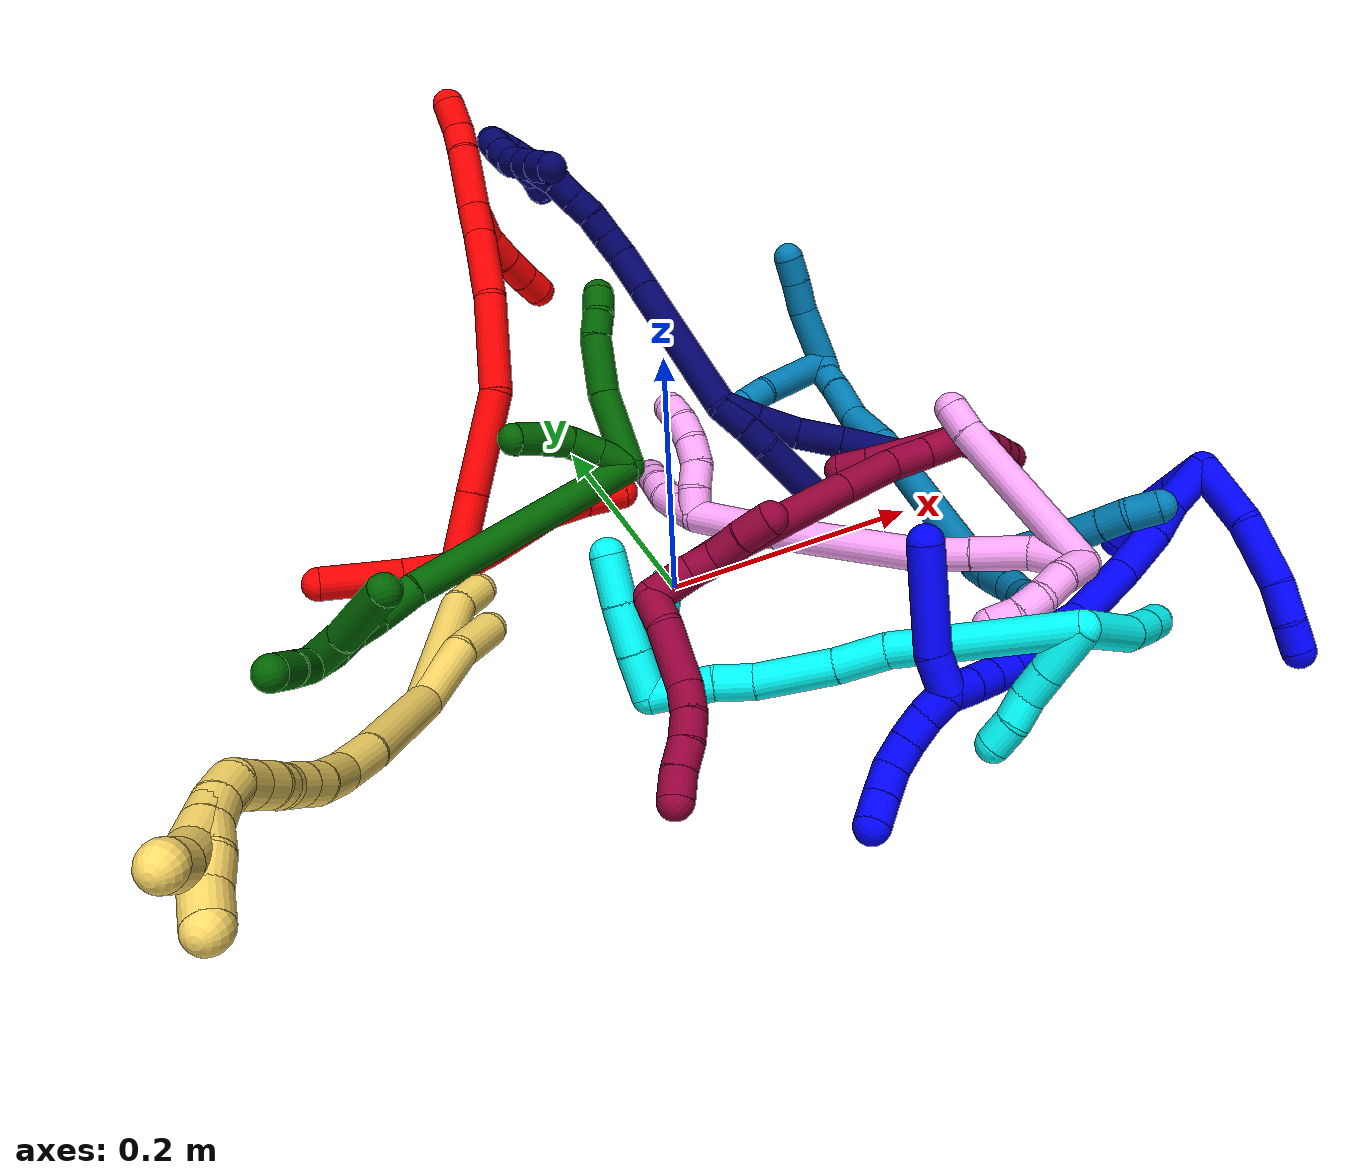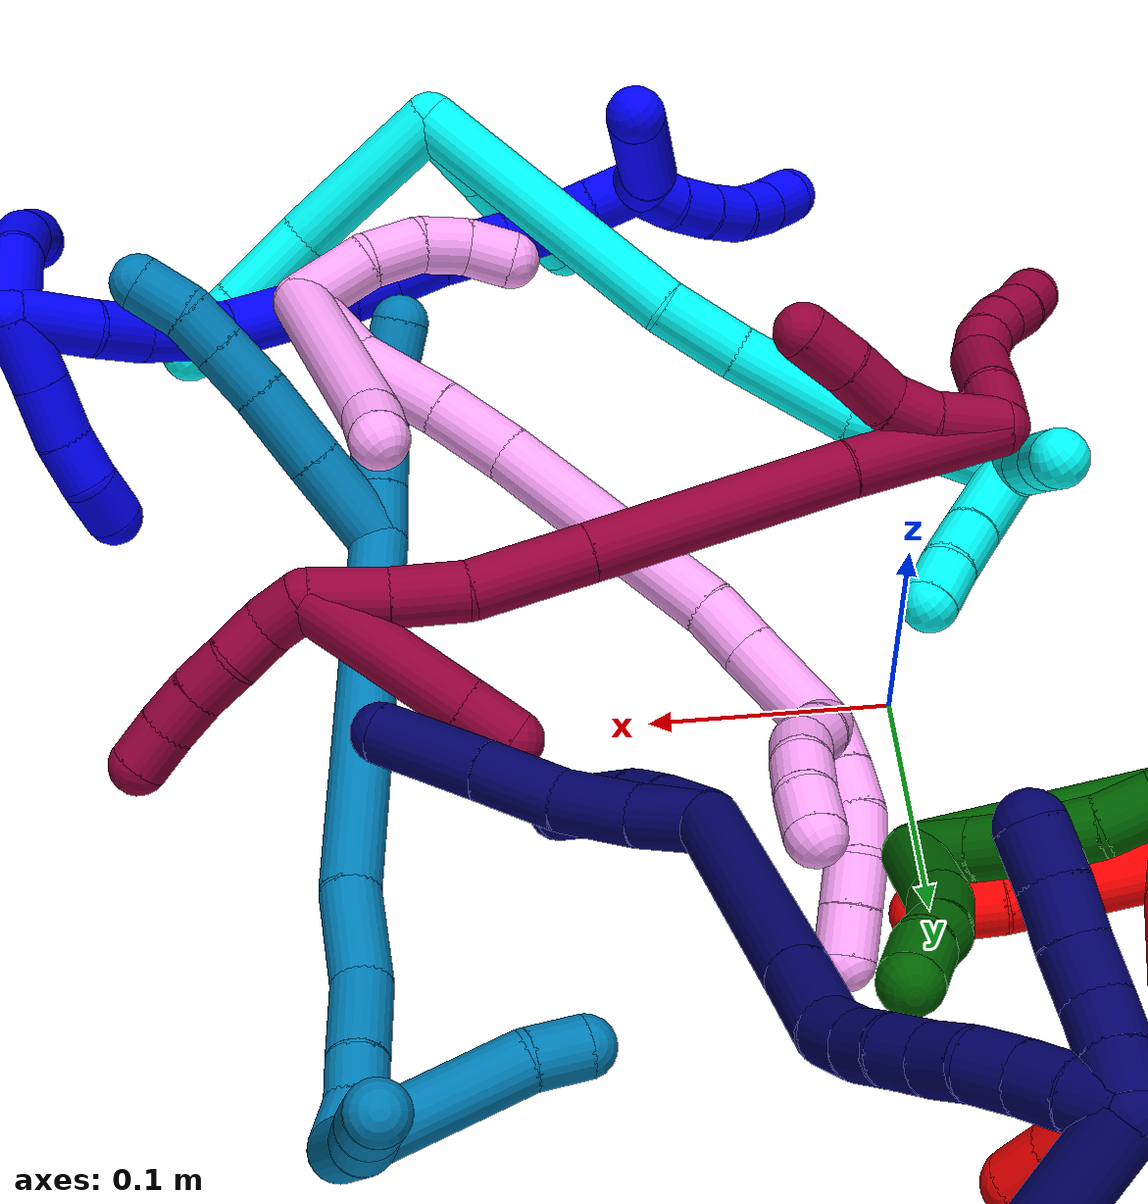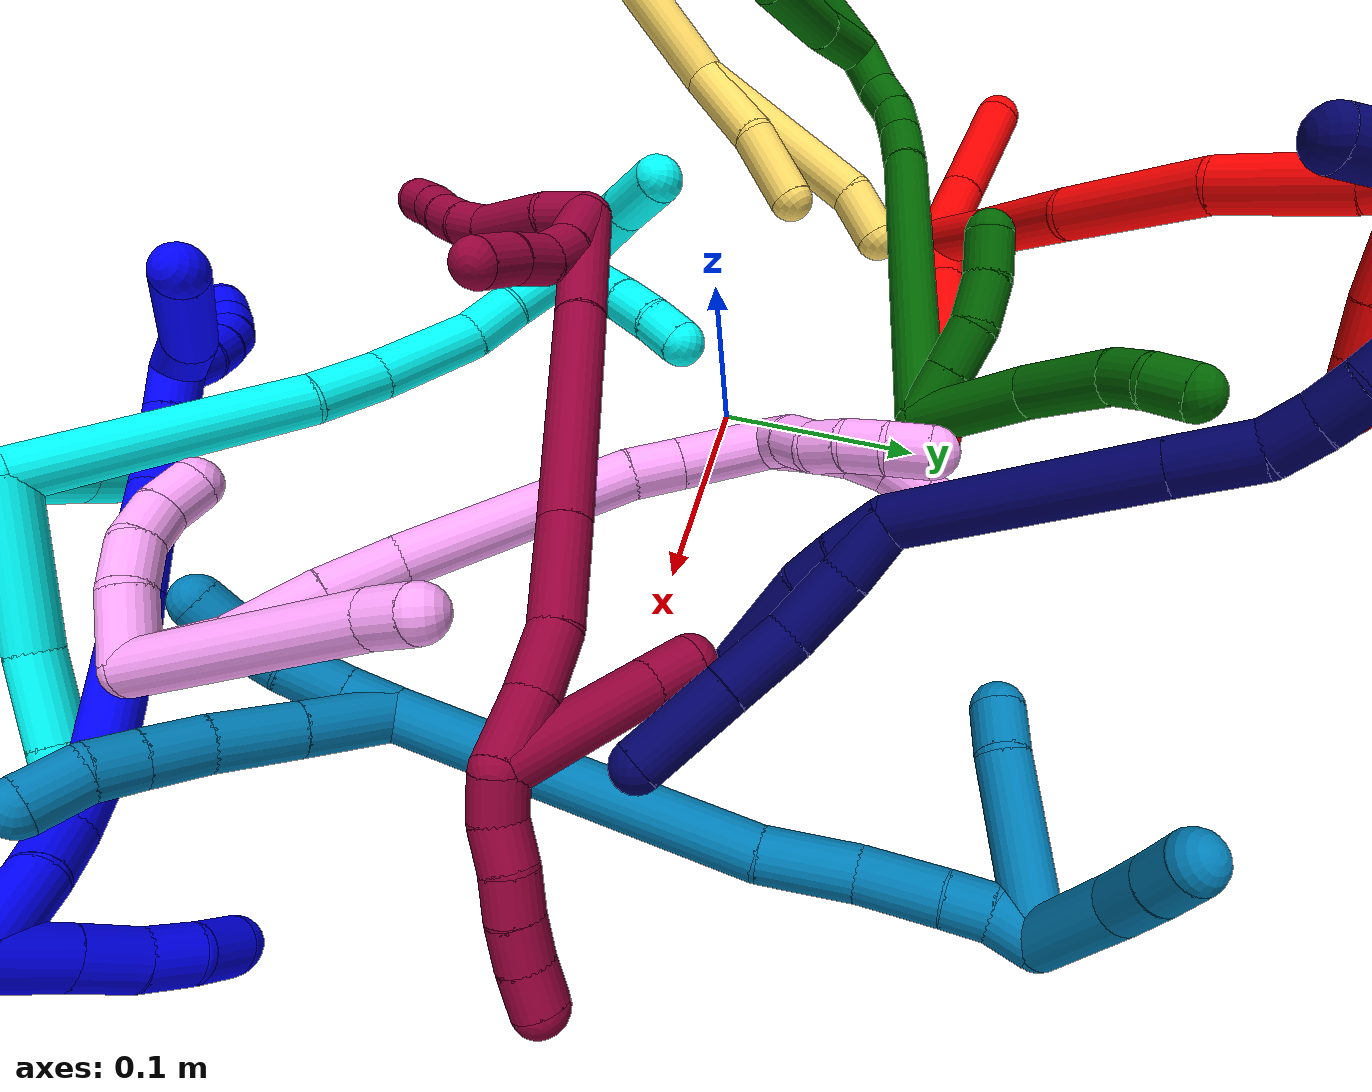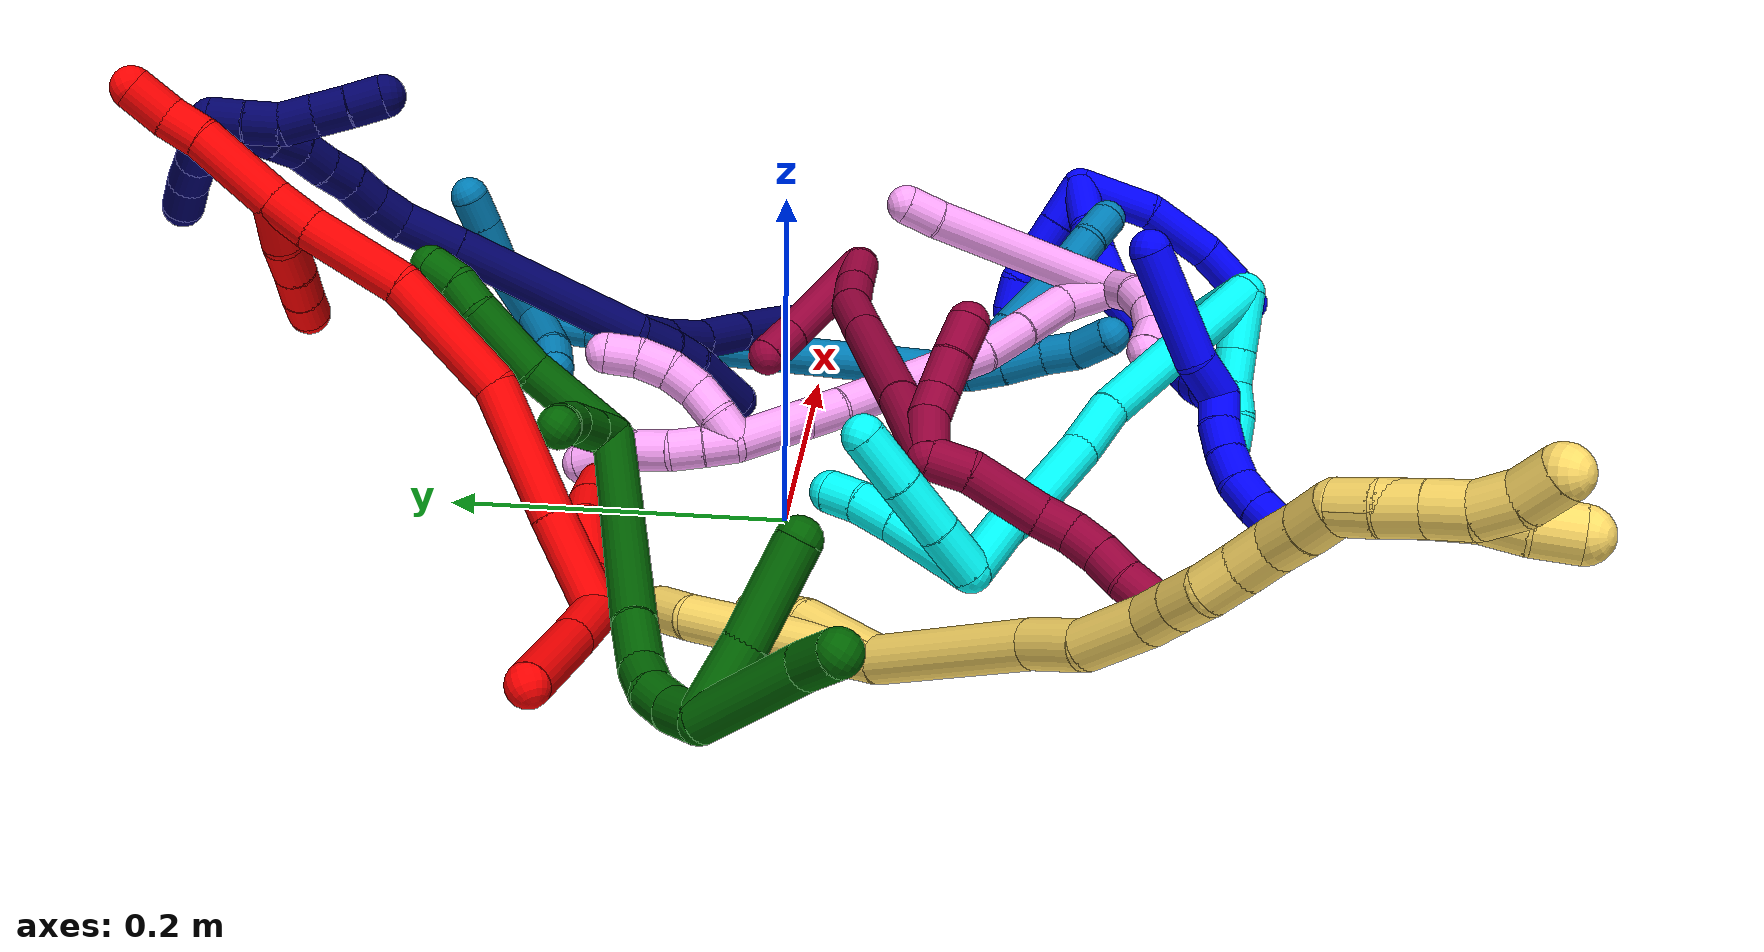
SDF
<sdf version="1.7">
 <world name="default">
  <plugin name="TubeGeneratorPlugin" filename="libtube_generator_plugin.so"/>
  <model name="photoneo_s_sensor">
   <static>1</static>
   <pose>0 0 2 1.57079 1.57079 3.14159</pose>
   <link name="link">
    <inertial><mass>0.1</mass></inertial>
    <sensor name="sensor" type="depth">
     <update_rate>30</update_rate>
     <camera>
      <horizontal_fov>1.22</horizontal_fov>
      <image><width>1920</width><height>1200</height><format>B8G8R8</format></image>
      <clip><near>0.1</near><far>4</far></clip>
      <depth_camera><output>points</output></depth_camera>
     </camera>
     <plugin name="camera_plugin" filename="libgazebo_ros_depth_camera.so">
      <baseline>0.2</baseline>
      <alwaysOn>1</alwaysOn>
      <updateRate>0.0</updateRate>
      <cameraName>camera_ir</cameraName>
      <imageTopicName>/camera/color/image_raw</imageTopicName>
      <cameraInfoTopicName>/camera/color/camera_info</cameraInfoTopicName>
      <depthImageTopicName>/camera/depth/image_raw</depthImageTopicName>
      <depthImageCameraInfoTopicName>/camera/depth/camera_info</depthImageCameraInfoTopicName>
      <pointCloudTopicName>/camera/depth/points</pointCloudTopicName>
      <frameName>fr_optical</frameName>
      <pointCloudCutoff>0.1</pointCloudCutoff>
      <pointCloudCutoffMax>2.0</pointCloudCutoffMax>
      <distortionK1>0</distortionK1>
      <distortionK2>0</distortionK2>
      <distortionK3>0</distortionK3>
      <distortionT1>0</distortionT1>
      <distortionT2>0</distortionT2>
      <CxPrime>0</CxPrime>
      <Cx>0</Cx>
      <Cy>0</Cy>
      <focalLength>0</focalLength>
      <hackBaseline>0</hackBaseline>
     </plugin>
    </sensor>
   </link>
  </model>
  <gravity>0 0 -9.8</gravity>
  <magnetic_field>6e-06 2.3e-05 -4.2e-05</magnetic_field>
  <atmosphere type="adiabatic"/>
  <physics name="default_physics" default="0" type="ode">
   <max_step_size>0.003</max_step_size>
   <real_time_factor>1</real_time_factor>
   <real_time_update_rate>1000</real_time_update_rate>
   <max_contacts>10000</max_contacts>
   <ode>
    <solver>
     <type>quick</type>
     <iters>100</iters>
     <sor>1.3</sor>
     <use_dynamic_moi_rescaling>0</use_dynamic_moi_rescaling>
    </solver>
    <constraints>
     <contact_max_correcting_vel>0</contact_max_correcting_vel>
     <contact_surface_layer>0.001</contact_surface_layer>
     <cfm>0</cfm>
     <erp>0.2</erp>
    </constraints>
   </ode>
  </physics>
  <scene><ambient>0.4 0.4 0.4 1</ambient><background>0.7 0.7 0.7 1</background><shadows>0</shadows></scene>
  <audio><device>default</device></audio>
  <spherical_coordinates>
   <surface_model>EARTH_WGS84</surface_model>
   <latitude_deg>0</latitude_deg>
   <longitude_deg>0</longitude_deg>
   <elevation>0</elevation>
   <heading_deg>0</heading_deg>
  </spherical_coordinates>
  <model name="bin">
   <static>1</static>
   <link name="bottom">
    <collision name="collision-bottom">
     <pose>0 0 -0.01 0 -0 0</pose>
     <geometry><box><size>0.8 0.6 0.02</size></box></geometry>
     <surface>
      <friction><ode><mu>100</mu><mu2>100</mu2></ode></friction>
      <contact><collide_bitmask>65535</collide_bitmask></contact>
     </surface>
    </collision>
   </link>
   <link name="west_wall">
    <collision name="collision-west_wall">
     <pose>-0.41 0 0.1 0 -0 0</pose>
     <geometry><box><size>0.02 0.6 0.2</size></box></geometry>
     <surface>
      <friction><ode><mu>100</mu><mu2>100</mu2></ode></friction>
      <contact><collide_bitmask>65535</collide_bitmask></contact>
     </surface>
    </collision>
   </link>
   <link name="east_wall">
    <collision name="collision-east_wall">
     <pose>0.41 0 0.1 0 -0 0</pose>
     <geometry><box><size>0.02 0.6 0.2</size></box></geometry>
     <surface>
      <friction><ode><mu>100</mu><mu2>100</mu2></ode></friction>
      <contact><collide_bitmask>65535</collide_bitmask></contact>
     </surface>
    </collision>
   </link>
   <link name="south_wall">
    <collision name="collision-south_wall">
     <pose>0 -0.31 0.1 0 -0 0</pose>
     <geometry><box><size>0.8 0.02 0.2</size></box></geometry>
     <surface>
      <friction><ode><mu>100</mu><mu2>100</mu2></ode></friction>
      <contact><collide_bitmask>65535</collide_bitmask></contact>
     </surface>
    </collision>
   </link>
   <link name="north_wall">
    <collision name="collision-north_wall">
     <pose>0 0.31 0.1 0 -0 0</pose>
     <geometry><box><size>0.8 0.02 0.2</size></box></geometry>
     <surface>
      <friction><ode><mu>100</mu><mu2>100</mu2></ode></friction>
      <contact><collide_bitmask>65535</collide_bitmask></contact>
     </surface>
    </collision>
   </link>
  </model>
  <model name="1">
   <static>0</static>
   <link name="1">
    <collision name="collision-cylinder-e_1_2_8">
     <pose>0.020681 -0.014697 -0.005507 1.92933 0.921614 1.24304</pose>
     <geometry><cylinder><radius>0.0125</radius><length>0.051925</length></cylinder></geometry>
     <surface>
      <friction><ode><mu>1.16</mu><mu2>1.16</mu2><slip1>0</slip1><slip2>0</slip2></ode></friction>
      <contact><ode><kp>1e+06</kp><kd>1</kd><max_vel>0</max_vel><min_depth>0.001</min_depth></ode></contact>
     </surface>
    </collision>
    <visual name="visual-cylinder-e_1_2_8">
     <pose>0.020681 -0.014697 -0.005507 1.92933 0.921614 1.24304</pose>
     <geometry><cylinder><radius>0.0125</radius><length>0.051925</length></cylinder></geometry>
     <material><ambient>0 0 1 1</ambient></material>
    </visual>
    <collision name="collision-cylinder-e_2_8_9">
     <pose>0.060529 -0.039724 -0.022154 2.39388 0.900605 1.77815</pose>
     <geometry><cylinder><radius>0.0125</radius><length>0.048915</length></cylinder></geometry>
     <surface>
      <friction><ode><mu>1.16</mu><mu2>1.16</mu2><slip1>0</slip1><slip2>0</slip2></ode></friction>
      <contact><ode><kp>1e+06</kp><kd>1</kd><max_vel>0</max_vel><min_depth>0.001</min_depth></ode></contact>
     </surface>
    </collision>
    <visual name="visual-cylinder-e_2_8_9">
     <pose>0.060529 -0.039724 -0.022154 2.39388 0.900605 1.77815</pose>
     <geometry><cylinder><radius>0.0125</radius><length>0.048915</length></cylinder></geometry>
     <material><ambient>0 0 1 1</ambient></material>
    </visual>
    <collision name="collision-cylinder-e_3_9_10">
     <pose>0.08962 -0.055337 -0.042104 2.60137 0.768077 1.94019</pose>
     <geometry><cylinder><radius>0.0125</radius><length>0.028568</length></cylinder></geometry>
     <surface>
      <friction><ode><mu>1.16</mu><mu2>1.16</mu2><slip1>0</slip1><slip2>0</slip2></ode></friction>
      <contact><ode><kp>1e+06</kp><kd>1</kd><max_vel>0</max_vel><min_depth>0.001</min_depth></ode></contact>
     </surface>
    </collision>
    <visual name="visual-cylinder-e_3_9_10">
     <pose>0.08962 -0.055337 -0.042104 2.60137 0.768077 1.94019</pose>
     <geometry><cylinder><radius>0.0125</radius><length>0.028568</length></cylinder></geometry>
     <material><ambient>0 0 1 1</ambient></material>
    </visual>
    <collision name="collision-cylinder-e_4_10_6">
     <pose>0.106956 -0.062803 -0.05772 2.8314 0.803631 2.43644</pose>
     <geometry><cylinder><radius>0.0125</radius><length>0.020593</length></cylinder></geometry>
     <surface>
      <friction><ode><mu>1.16</mu><mu2>1.16</mu2><slip1>0</slip1><slip2>0</slip2></ode></friction>
      <contact><ode><kp>1e+06</kp><kd>1</kd><max_vel>0</max_vel><min_depth>0.001</min_depth></ode></contact>
     </surface>
    </collision>
    <visual name="visual-cylinder-e_4_10_6">
     <pose>0.106956 -0.062803 -0.05772 2.8314 0.803631 2.43644</pose>
     <geometry><cylinder><radius>0.0125</radius><length>0.020593</length></cylinder></geometry>
     <material><ambient>0 0 1 1</ambient></material>
    </visual>
    <collision name="collision-cylinder-e_1_2_11">
     <pose>-0.004086 0.005247 -0.013679 -2.77533 -0.272016 1.27274</pose>
     <geometry><cylinder><radius>0.0125</radius><length>0.030419</length></cylinder></geometry>
     <surface>
      <friction><ode><mu>1.16</mu><mu2>1.16</mu2><slip1>0</slip1><slip2>0</slip2></ode></friction>
      <contact><ode><kp>1e+06</kp><kd>1</kd><max_vel>0</max_vel><min_depth>0.001</min_depth></ode></contact>
     </surface>
    </collision>
    <visual name="visual-cylinder-e_1_2_11">
     <pose>-0.004086 0.005247 -0.013679 -2.77533 -0.272016 1.27274</pose>
     <geometry><cylinder><radius>0.0125</radius><length>0.030419</length></cylinder></geometry>
     <material><ambient>0 0 1 1</ambient></material>
    </visual>
    <collision name="collision-cylinder-e_2_11_12">
     <pose>-0.011623 0.015399 -0.03935 -2.75333 -0.260258 1.17458</pose>
     <geometry><cylinder><radius>0.0125</radius><length>0.026818</length></cylinder></geometry>
     <surface>
      <friction><ode><mu>1.16</mu><mu2>1.16</mu2><slip1>0</slip1><slip2>0</slip2></ode></friction>
      <contact><ode><kp>1e+06</kp><kd>1</kd><max_vel>0</max_vel><min_depth>0.001</min_depth></ode></contact>
     </surface>
    </collision>
    <visual name="visual-cylinder-e_2_11_12">
     <pose>-0.011623 0.015399 -0.03935 -2.75333 -0.260258 1.17458</pose>
     <geometry><cylinder><radius>0.0125</radius><length>0.026818</length></cylinder></geometry>
     <material><ambient>0 0 1 1</ambient></material>
    </visual>
    <collision name="collision-cylinder-e_3_12_13">
     <pose>-0.018799 0.022992 -0.06093 -2.86825 -0.357988 1.84172</pose>
     <geometry><cylinder><radius>0.0125</radius><length>0.021259</length></cylinder></geometry>
     <surface>
      <friction><ode><mu>1.16</mu><mu2>1.16</mu2><slip1>0</slip1><slip2>0</slip2></ode></friction>
      <contact><ode><kp>1e+06</kp><kd>1</kd><max_vel>0</max_vel><min_depth>0.001</min_depth></ode></contact>
     </surface>
    </collision>
    <visual name="visual-cylinder-e_3_12_13">
     <pose>-0.018799 0.022992 -0.06093 -2.86825 -0.357988 1.84172</pose>
     <geometry><cylinder><radius>0.0125</radius><length>0.021259</length></cylinder></geometry>
     <material><ambient>0 0 1 1</ambient></material>
    </visual>
    <collision name="collision-cylinder-e_4_13_5">
     <pose>-0.023436 0.026579 -0.081191 -3.0575 -0.084994 1.58144</pose>
     <geometry><cylinder><radius>0.0125</radius><length>0.021503</length></cylinder></geometry>
     <surface>
      <friction><ode><mu>1.16</mu><mu2>1.16</mu2><slip1>0</slip1><slip2>0</slip2></ode></friction>
      <contact><ode><kp>1e+06</kp><kd>1</kd><max_vel>0</max_vel><min_depth>0.001</min_depth></ode></contact>
     </surface>
    </collision>
    <visual name="visual-cylinder-e_4_13_5">
     <pose>-0.023436 0.026579 -0.081191 -3.0575 -0.084994 1.58144</pose>
     <geometry><cylinder><radius>0.0125</radius><length>0.021503</length></cylinder></geometry>
     <material><ambient>0 0 1 1</ambient></material>
    </visual>
    <collision name="collision-cylinder-e_1_2_14">
     <pose>-0.004372 -0.010829 -0.014307 2.4937 -0.238981 -0.686801</pose>
     <geometry><cylinder><radius>0.0125</radius><length>0.036935</length></cylinder></geometry>
     <surface>
      <friction><ode><mu>1.16</mu><mu2>1.16</mu2><slip1>0</slip1><slip2>0</slip2></ode></friction>
      <contact><ode><kp>1e+06</kp><kd>1</kd><max_vel>0</max_vel><min_depth>0.001</min_depth></ode></contact>
     </surface>
    </collision>
    <visual name="visual-cylinder-e_1_2_14">
     <pose>-0.004372 -0.010829 -0.014307 2.4937 -0.238981 -0.686801</pose>
     <geometry><cylinder><radius>0.0125</radius><length>0.036935</length></cylinder></geometry>
     <material><ambient>0 0 1 1</ambient></material>
    </visual>
    <collision name="collision-cylinder-e_2_14_15">
     <pose>-0.009334 -0.029314 -0.038712 2.49282 -0.046587 -0.138346</pose>
     <geometry><cylinder><radius>0.0125</radius><length>0.025373</length></cylinder></geometry>
     <surface>
      <friction><ode><mu>1.16</mu><mu2>1.16</mu2><slip1>0</slip1><slip2>0</slip2></ode></friction>
      <contact><ode><kp>1e+06</kp><kd>1</kd><max_vel>0</max_vel><min_depth>0.001</min_depth></ode></contact>
     </surface>
    </collision>
    <visual name="visual-cylinder-e_2_14_15">
     <pose>-0.009334 -0.029314 -0.038712 2.49282 -0.046587 -0.138346</pose>
     <geometry><cylinder><radius>0.0125</radius><length>0.025373</length></cylinder></geometry>
     <material><ambient>0 0 1 1</ambient></material>
    </visual>
    <collision name="collision-cylinder-e_3_15_16">
     <pose>-0.014282 -0.051558 -0.062095 2.30953 -0.217341 -0.484183</pose>
     <geometry><cylinder><radius>0.0125</radius><length>0.040412</length></cylinder></geometry>
     <surface>
      <friction><ode><mu>1.16</mu><mu2>1.16</mu2><slip1>0</slip1><slip2>0</slip2></ode></friction>
      <contact><ode><kp>1e+06</kp><kd>1</kd><max_vel>0</max_vel><min_depth>0.001</min_depth></ode></contact>
     </surface>
    </collision>
    <visual name="visual-cylinder-e_3_15_16">
     <pose>-0.014282 -0.051558 -0.062095 2.30953 -0.217341 -0.484183</pose>
     <geometry><cylinder><radius>0.0125</radius><length>0.040412</length></cylinder></geometry>
     <material><ambient>0 0 1 1</ambient></material>
    </visual>
    <collision name="collision-cylinder-e_4_16_17">
     <pose>-0.026511 -0.091071 -0.088525 2.05608 -0.272411 -0.446849</pose>
     <geometry><cylinder><radius>0.0125</radius><length>0.058514</length></cylinder></geometry>
     <surface>
      <friction><ode><mu>1.16</mu><mu2>1.16</mu2><slip1>0</slip1><slip2>0</slip2></ode></friction>
      <contact><ode><kp>1e+06</kp><kd>1</kd><max_vel>0</max_vel><min_depth>0.001</min_depth></ode></contact>
     </surface>
    </collision>
    <visual name="visual-cylinder-e_4_16_17">
     <pose>-0.026511 -0.091071 -0.088525 2.05608 -0.272411 -0.446849</pose>
     <geometry><cylinder><radius>0.0125</radius><length>0.058514</length></cylinder></geometry>
     <material><ambient>0 0 1 1</ambient></material>
    </visual>
    <collision name="collision-cylinder-e_5_17_18">
     <pose>-0.038585 -0.125125 -0.10414 1.83516 -0.418152 -0.54091</pose>
     <geometry><cylinder><radius>0.0125</radius><length>0.0207</length></cylinder></geometry>
     <surface>
      <friction><ode><mu>1.16</mu><mu2>1.16</mu2><slip1>0</slip1><slip2>0</slip2></ode></friction>
      <contact><ode><kp>1e+06</kp><kd>1</kd><max_vel>0</max_vel><min_depth>0.001</min_depth></ode></contact>
     </surface>
    </collision>
    <visual name="visual-cylinder-e_5_17_18">
     <pose>-0.038585 -0.125125 -0.10414 1.83516 -0.418152 -0.54091</pose>
     <geometry><cylinder><radius>0.0125</radius><length>0.0207</length></cylinder></geometry>
     <material><ambient>0 0 1 1</ambient></material>
    </visual>
    <collision name="collision-cylinder-e_6_18_19">
     <pose>-0.047267 -0.143905 -0.10916 1.82893 -0.421839 -0.54225</pose>
     <geometry><cylinder><radius>0.0125</radius><length>0.021879</length></cylinder></geometry>
     <surface>
      <friction><ode><mu>1.16</mu><mu2>1.16</mu2><slip1>0</slip1><slip2>0</slip2></ode></friction>
      <contact><ode><kp>1e+06</kp><kd>1</kd><max_vel>0</max_vel><min_depth>0.001</min_depth></ode></contact>
     </surface>
    </collision>
    <visual name="visual-cylinder-e_6_18_19">
     <pose>-0.047267 -0.143905 -0.10916 1.82893 -0.421839 -0.54225</pose>
     <geometry><cylinder><radius>0.0125</radius><length>0.021879</length></cylinder></geometry>
     <material><ambient>0 0 1 1</ambient></material>
    </visual>
    <collision name="collision-cylinder-e_7_19_20">
     <pose>-0.056918 -0.167598 -0.118568 2.02523 -0.319558 -0.505147</pose>
     <geometry><cylinder><radius>0.0125</radius><length>0.032925</length></cylinder></geometry>
     <surface>
      <friction><ode><mu>1.16</mu><mu2>1.16</mu2><slip1>0</slip1><slip2>0</slip2></ode></friction>
      <contact><ode><kp>1e+06</kp><kd>1</kd><max_vel>0</max_vel><min_depth>0.001</min_depth></ode></contact>
     </surface>
    </collision>
    <visual name="visual-cylinder-e_7_19_20">
     <pose>-0.056918 -0.167598 -0.118568 2.02523 -0.319558 -0.505147</pose>
     <geometry><cylinder><radius>0.0125</radius><length>0.032925</length></cylinder></geometry>
     <material><ambient>0 0 1 1</ambient></material>
    </visual>
    <collision name="collision-cylinder-e_8_20_21">
     <pose>-0.066959 -0.190206 -0.128055 1.86837 -0.497816 -0.662306</pose>
     <geometry><cylinder><radius>0.0125</radius><length>0.020394</length></cylinder></geometry>
     <surface>
      <friction><ode><mu>1.16</mu><mu2>1.16</mu2><slip1>0</slip1><slip2>0</slip2></ode></friction>
      <contact><ode><kp>1e+06</kp><kd>1</kd><max_vel>0</max_vel><min_depth>0.001</min_depth></ode></contact>
     </surface>
    </collision>
    <visual name="visual-cylinder-e_8_20_21">
     <pose>-0.066959 -0.190206 -0.128055 1.86837 -0.497816 -0.662306</pose>
     <geometry><cylinder><radius>0.0125</radius><length>0.020394</length></cylinder></geometry>
     <material><ambient>0 0 1 1</ambient></material>
    </visual>
    <collision name="collision-cylinder-e_9_21_22">
     <pose>-0.076637 -0.207823 -0.132326 1.75051 -0.481706 -0.572373</pose>
     <geometry><cylinder><radius>0.0125</radius><length>0.020761</length></cylinder></geometry>
     <surface>
      <friction><ode><mu>1.16</mu><mu2>1.16</mu2><slip1>0</slip1><slip2>0</slip2></ode></friction>
      <contact><ode><kp>1e+06</kp><kd>1</kd><max_vel>0</max_vel><min_depth>0.001</min_depth></ode></contact>
     </surface>
    </collision>
    <visual name="visual-cylinder-e_9_21_22">
     <pose>-0.076637 -0.207823 -0.132326 1.75051 -0.481706 -0.572373</pose>
     <geometry><cylinder><radius>0.0125</radius><length>0.020761</length></cylinder></geometry>
     <material><ambient>0 0 1 1</ambient></material>
    </visual>
    <collision name="collision-cylinder-e_10_22_1">
     <pose>-0.086889 -0.226372 -0.135499 1.73032 -0.514846 -0.599397</pose>
     <geometry><cylinder><radius>0.0125</radius><length>0.022106</length></cylinder></geometry>
     <surface>
      <friction><ode><mu>1.16</mu><mu2>1.16</mu2><slip1>0</slip1><slip2>0</slip2></ode></friction>
      <contact><ode><kp>1e+06</kp><kd>1</kd><max_vel>0</max_vel><min_depth>0.001</min_depth></ode></contact>
     </surface>
    </collision>
    <visual name="visual-cylinder-e_10_22_1">
     <pose>-0.086889 -0.226372 -0.135499 1.73032 -0.514846 -0.599397</pose>
     <geometry><cylinder><radius>0.0125</radius><length>0.022106</length></cylinder></geometry>
     <material><ambient>0 0 1 1</ambient></material>
    </visual>
    <collision name="collision-cylinder-e_1_1_23">
     <pose>-0.095132 -0.239891 -0.145744 2.70937 -0.283864 -1.15398</pose>
     <geometry><cylinder><radius>0.0125</radius><length>0.02</length></cylinder></geometry>
     <surface>
      <friction><ode><mu>1.16</mu><mu2>1.16</mu2><slip1>0</slip1><slip2>0</slip2></ode></friction>
      <contact><ode><kp>1e+06</kp><kd>1</kd><max_vel>0</max_vel><min_depth>0.001</min_depth></ode></contact>
     </surface>
    </collision>
    <visual name="visual-cylinder-e_1_1_23">
     <pose>-0.095132 -0.239891 -0.145744 2.70937 -0.283864 -1.15398</pose>
     <geometry><cylinder><radius>0.0125</radius><length>0.02</length></cylinder></geometry>
     <material><ambient>0 0 1 1</ambient></material>
    </visual>
    <collision name="collision-cylinder-e_2_23_24">
     <pose>-0.09939 -0.249407 -0.162688 2.55275 -0.146264 -0.474126</pose>
     <geometry><cylinder><radius>0.0125</radius><length>0.02</length></cylinder></geometry>
     <surface>
      <friction><ode><mu>1.16</mu><mu2>1.16</mu2><slip1>0</slip1><slip2>0</slip2></ode></friction>
      <contact><ode><kp>1e+06</kp><kd>1</kd><max_vel>0</max_vel><min_depth>0.001</min_depth></ode></contact>
     </surface>
    </collision>
    <visual name="visual-cylinder-e_2_23_24">
     <pose>-0.09939 -0.249407 -0.162688 2.55275 -0.146264 -0.474126</pose>
     <geometry><cylinder><radius>0.0125</radius><length>0.02</length></cylinder></geometry>
     <material><ambient>0 0 1 1</ambient></material>
    </visual>
    <collision name="collision-cylinder-e_3_24_25">
     <pose>-0.101332 -0.261185 -0.17868 2.46128 -0.048422 -0.136634</pose>
     <geometry><cylinder><radius>0.0125</radius><length>0.02</length></cylinder></geometry>
     <surface>
      <friction><ode><mu>1.16</mu><mu2>1.16</mu2><slip1>0</slip1><slip2>0</slip2></ode></friction>
      <contact><ode><kp>1e+06</kp><kd>1</kd><max_vel>0</max_vel><min_depth>0.001</min_depth></ode></contact>
     </surface>
    </collision>
    <visual name="visual-cylinder-e_3_24_25">
     <pose>-0.101332 -0.261185 -0.17868 2.46128 -0.048422 -0.136634</pose>
     <geometry><cylinder><radius>0.0125</radius><length>0.02</length></cylinder></geometry>
     <material><ambient>0 0 1 1</ambient></material>
    </visual>
    <collision name="collision-cylinder-e_4_25_26">
     <pose>-0.100434 -0.275151 -0.192694 2.25372 0.138634 0.289911</pose>
     <geometry><cylinder><radius>0.0125</radius><length>0.02</length></cylinder></geometry>
     <surface>
      <friction><ode><mu>1.16</mu><mu2>1.16</mu2><slip1>0</slip1><slip2>0</slip2></ode></friction>
      <contact><ode><kp>1e+06</kp><kd>1</kd><max_vel>0</max_vel><min_depth>0.001</min_depth></ode></contact>
     </surface>
    </collision>
    <visual name="visual-cylinder-e_4_25_26">
     <pose>-0.100434 -0.275151 -0.192694 2.25372 0.138634 0.289911</pose>
     <geometry><cylinder><radius>0.0125</radius><length>0.02</length></cylinder></geometry>
     <material><ambient>0 0 1 1</ambient></material>
    </visual>
    <collision name="collision-cylinder-e_5_26_4">
     <pose>-0.097554 -0.2912 -0.204214 2.1329 0.150339 0.271212</pose>
     <geometry><cylinder><radius>0.0125</radius><length>0.02</length></cylinder></geometry>
     <surface>
      <friction><ode><mu>1.16</mu><mu2>1.16</mu2><slip1>0</slip1><slip2>0</slip2></ode></friction>
      <contact><ode><kp>1e+06</kp><kd>1</kd><max_vel>0</max_vel><min_depth>0.001</min_depth></ode></contact>
     </surface>
    </collision>
    <visual name="visual-cylinder-e_5_26_4">
     <pose>-0.097554 -0.2912 -0.204214 2.1329 0.150339 0.271212</pose>
     <geometry><cylinder><radius>0.0125</radius><length>0.02</length></cylinder></geometry>
     <material><ambient>0 0 1 1</ambient></material>
    </visual>
    <collision name="collision-cylinder-e_1_1_27">
     <pose>-0.102595 -0.234301 -0.127664 -0.166062 -0.82436 0.072742</pose>
     <geometry><cylinder><radius>0.0125</radius><length>0.027961</length></cylinder></geometry>
     <surface>
      <friction><ode><mu>1.16</mu><mu2>1.16</mu2><slip1>0</slip1><slip2>0</slip2></ode></friction>
      <contact><ode><kp>1e+06</kp><kd>1</kd><max_vel>0</max_vel><min_depth>0.001</min_depth></ode></contact>
     </surface>
    </collision>
    <visual name="visual-cylinder-e_1_1_27">
     <pose>-0.102595 -0.234301 -0.127664 -0.166062 -0.82436 0.072742</pose>
     <geometry><cylinder><radius>0.0125</radius><length>0.027961</length></cylinder></geometry>
     <material><ambient>0 0 1 1</ambient></material>
    </visual>
    <collision name="collision-cylinder-e_2_27_3">
     <pose>-0.131595 -0.226689 -0.088139 -0.197705 -0.547072 0.055637</pose>
     <geometry><cylinder><radius>0.0125</radius><length>0.072039</length></cylinder></geometry>
     <surface>
      <friction><ode><mu>1.16</mu><mu2>1.16</mu2><slip1>0</slip1><slip2>0</slip2></ode></friction>
      <contact><ode><kp>1e+06</kp><kd>1</kd><max_vel>0</max_vel><min_depth>0.001</min_depth></ode></contact>
     </surface>
    </collision>
    <visual name="visual-cylinder-e_2_27_3">
     <pose>-0.131595 -0.226689 -0.088139 -0.197705 -0.547072 0.055637</pose>
     <geometry><cylinder><radius>0.0125</radius><length>0.072039</length></cylinder></geometry>
     <material><ambient>0 0 1 1</ambient></material>
    </visual>
    <collision name="collision-sphere-3">
     <pose>-0.150332 -0.220647 -0.057975 0 -0 0</pose>
     <geometry><sphere><radius>0.0125</radius></sphere></geometry>
     <surface>
      <friction><ode><mu>1.16</mu><mu2>1.16</mu2><slip1>0</slip1><slip2>0</slip2></ode></friction>
      <contact><ode><kp>1e+06</kp><kd>1</kd><max_vel>0</max_vel><min_depth>0.001</min_depth></ode></contact>
     </surface>
    </collision>
    <visual name="visual-sphere-3">
     <pose>-0.150332 -0.220647 -0.057975 0 -0 0</pose>
     <geometry><sphere><radius>0.0125</radius></sphere></geometry>
     <material><ambient>0 0 1 1</ambient></material>
    </visual>
    <collision name="collision-sphere-27">
     <pose>-0.112858 -0.232732 -0.118302 0 -0 0</pose>
     <geometry><sphere><radius>0.0125</radius></sphere></geometry>
     <surface>
      <friction><ode><mu>1.16</mu><mu2>1.16</mu2><slip1>0</slip1><slip2>0</slip2></ode></friction>
      <contact><ode><kp>1e+06</kp><kd>1</kd><max_vel>0</max_vel><min_depth>0.001</min_depth></ode></contact>
     </surface>
    </collision>
    <visual name="visual-sphere-27">
     <pose>-0.112858 -0.232732 -0.118302 0 -0 0</pose>
     <geometry><sphere><radius>0.0125</radius></sphere></geometry>
     <material><ambient>0 0 1 1</ambient></material>
    </visual>
    <collision name="collision-sphere-4">
     <pose>-0.096056 -0.299566 -0.209484 0 -0 0</pose>
     <geometry><sphere><radius>0.0125</radius></sphere></geometry>
     <surface>
      <friction><ode><mu>1.16</mu><mu2>1.16</mu2><slip1>0</slip1><slip2>0</slip2></ode></friction>
      <contact><ode><kp>1e+06</kp><kd>1</kd><max_vel>0</max_vel><min_depth>0.001</min_depth></ode></contact>
     </surface>
    </collision>
    <visual name="visual-sphere-4">
     <pose>-0.096056 -0.299566 -0.209484 0 -0 0</pose>
     <geometry><sphere><radius>0.0125</radius></sphere></geometry>
     <material><ambient>0 0 1 1</ambient></material>
    </visual>
    <collision name="collision-sphere-26">
     <pose>-0.099052 -0.282834 -0.198945 0 -0 0</pose>
     <geometry><sphere><radius>0.0125</radius></sphere></geometry>
     <surface>
      <friction><ode><mu>1.16</mu><mu2>1.16</mu2><slip1>0</slip1><slip2>0</slip2></ode></friction>
      <contact><ode><kp>1e+06</kp><kd>1</kd><max_vel>0</max_vel><min_depth>0.001</min_depth></ode></contact>
     </surface>
    </collision>
    <visual name="visual-sphere-26">
     <pose>-0.099052 -0.282834 -0.198945 0 -0 0</pose>
     <geometry><sphere><radius>0.0125</radius></sphere></geometry>
     <material><ambient>0 0 1 1</ambient></material>
    </visual>
    <collision name="collision-sphere-25">
     <pose>-0.101816 -0.267468 -0.186444 0 -0 0</pose>
     <geometry><sphere><radius>0.0125</radius></sphere></geometry>
     <surface>
      <friction><ode><mu>1.16</mu><mu2>1.16</mu2><slip1>0</slip1><slip2>0</slip2></ode></friction>
      <contact><ode><kp>1e+06</kp><kd>1</kd><max_vel>0</max_vel><min_depth>0.001</min_depth></ode></contact>
     </surface>
    </collision>
    <visual name="visual-sphere-25">
     <pose>-0.101816 -0.267468 -0.186444 0 -0 0</pose>
     <geometry><sphere><radius>0.0125</radius></sphere></geometry>
     <material><ambient>0 0 1 1</ambient></material>
    </visual>
    <collision name="collision-sphere-24">
     <pose>-0.100848 -0.254902 -0.170915 0 -0 0</pose>
     <geometry><sphere><radius>0.0125</radius></sphere></geometry>
     <surface>
      <friction><ode><mu>1.16</mu><mu2>1.16</mu2><slip1>0</slip1><slip2>0</slip2></ode></friction>
      <contact><ode><kp>1e+06</kp><kd>1</kd><max_vel>0</max_vel><min_depth>0.001</min_depth></ode></contact>
     </surface>
    </collision>
    <visual name="visual-sphere-24">
     <pose>-0.100848 -0.254902 -0.170915 0 -0 0</pose>
     <geometry><sphere><radius>0.0125</radius></sphere></geometry>
     <material><ambient>0 0 1 1</ambient></material>
    </visual>
    <collision name="collision-sphere-23">
     <pose>-0.097933 -0.243913 -0.154461 0 -0 0</pose>
     <geometry><sphere><radius>0.0125</radius></sphere></geometry>
     <surface>
      <friction><ode><mu>1.16</mu><mu2>1.16</mu2><slip1>0</slip1><slip2>0</slip2></ode></friction>
      <contact><ode><kp>1e+06</kp><kd>1</kd><max_vel>0</max_vel><min_depth>0.001</min_depth></ode></contact>
     </surface>
    </collision>
    <visual name="visual-sphere-23">
     <pose>-0.097933 -0.243913 -0.154461 0 -0 0</pose>
     <geometry><sphere><radius>0.0125</radius></sphere></geometry>
     <material><ambient>0 0 1 1</ambient></material>
    </visual>
    <collision name="collision-sphere-1">
     <pose>-0.092331 -0.23587 -0.137027 0 -0 0</pose>
     <geometry><sphere><radius>0.0125</radius></sphere></geometry>
     <surface>
      <friction><ode><mu>1.16</mu><mu2>1.16</mu2><slip1>0</slip1><slip2>0</slip2></ode></friction>
      <contact><ode><kp>1e+06</kp><kd>1</kd><max_vel>0</max_vel><min_depth>0.001</min_depth></ode></contact>
     </surface>
    </collision>
    <visual name="visual-sphere-1">
     <pose>-0.092331 -0.23587 -0.137027 0 -0 0</pose>
     <geometry><sphere><radius>0.0125</radius></sphere></geometry>
     <material><ambient>0 0 1 1</ambient></material>
    </visual>
    <collision name="collision-sphere-22">
     <pose>-0.081446 -0.216874 -0.133971 0 -0 0</pose>
     <geometry><sphere><radius>0.0125</radius></sphere></geometry>
     <surface>
      <friction><ode><mu>1.16</mu><mu2>1.16</mu2><slip1>0</slip1><slip2>0</slip2></ode></friction>
      <contact><ode><kp>1e+06</kp><kd>1</kd><max_vel>0</max_vel><min_depth>0.001</min_depth></ode></contact>
     </surface>
    </collision>
    <visual name="visual-sphere-22">
     <pose>-0.081446 -0.216874 -0.133971 0 -0 0</pose>
     <geometry><sphere><radius>0.0125</radius></sphere></geometry>
     <material><ambient>0 0 1 1</ambient></material>
    </visual>
    <collision name="collision-sphere-21">
     <pose>-0.071828 -0.198772 -0.130682 0 -0 0</pose>
     <geometry><sphere><radius>0.0125</radius></sphere></geometry>
     <surface>
      <friction><ode><mu>1.16</mu><mu2>1.16</mu2><slip1>0</slip1><slip2>0</slip2></ode></friction>
      <contact><ode><kp>1e+06</kp><kd>1</kd><max_vel>0</max_vel><min_depth>0.001</min_depth></ode></contact>
     </surface>
    </collision>
    <visual name="visual-sphere-21">
     <pose>-0.071828 -0.198772 -0.130682 0 -0 0</pose>
     <geometry><sphere><radius>0.0125</radius></sphere></geometry>
     <material><ambient>0 0 1 1</ambient></material>
    </visual>
    <collision name="collision-sphere-11">
     <pose>-0.008173 0.010493 -0.027357 0 -0 0</pose>
     <geometry><sphere><radius>0.0125</radius></sphere></geometry>
     <surface>
      <friction><ode><mu>1.16</mu><mu2>1.16</mu2><slip1>0</slip1><slip2>0</slip2></ode></friction>
      <contact><ode><kp>1e+06</kp><kd>1</kd><max_vel>0</max_vel><min_depth>0.001</min_depth></ode></contact>
     </surface>
    </collision>
    <visual name="visual-sphere-11">
     <pose>-0.008173 0.010493 -0.027357 0 -0 0</pose>
     <geometry><sphere><radius>0.0125</radius></sphere></geometry>
     <material><ambient>0 0 1 1</ambient></material>
    </visual>
    <collision name="collision-sphere-6">
     <pose>0.114369 -0.064984 -0.064526 0 -0 0</pose>
     <geometry><sphere><radius>0.0125</radius></sphere></geometry>
     <surface>
      <friction><ode><mu>1.16</mu><mu2>1.16</mu2><slip1>0</slip1><slip2>0</slip2></ode></friction>
      <contact><ode><kp>1e+06</kp><kd>1</kd><max_vel>0</max_vel><min_depth>0.001</min_depth></ode></contact>
     </surface>
    </collision>
    <visual name="visual-sphere-6">
     <pose>0.114369 -0.064984 -0.064526 0 -0 0</pose>
     <geometry><sphere><radius>0.0125</radius></sphere></geometry>
     <material><ambient>0 0 1 1</ambient></material>
    </visual>
    <collision name="collision-sphere-10">
     <pose>0.099544 -0.060621 -0.050914 0 -0 0</pose>
     <geometry><sphere><radius>0.0125</radius></sphere></geometry>
     <surface>
      <friction><ode><mu>1.16</mu><mu2>1.16</mu2><slip1>0</slip1><slip2>0</slip2></ode></friction>
      <contact><ode><kp>1e+06</kp><kd>1</kd><max_vel>0</max_vel><min_depth>0.001</min_depth></ode></contact>
     </surface>
    </collision>
    <visual name="visual-sphere-10">
     <pose>0.099544 -0.060621 -0.050914 0 -0 0</pose>
     <geometry><sphere><radius>0.0125</radius></sphere></geometry>
     <material><ambient>0 0 1 1</ambient></material>
    </visual>
    <collision name="collision-sphere-9">
     <pose>0.079697 -0.050053 -0.033293 0 -0 0</pose>
     <geometry><sphere><radius>0.0125</radius></sphere></geometry>
     <surface>
      <friction><ode><mu>1.16</mu><mu2>1.16</mu2><slip1>0</slip1><slip2>0</slip2></ode></friction>
      <contact><ode><kp>1e+06</kp><kd>1</kd><max_vel>0</max_vel><min_depth>0.001</min_depth></ode></contact>
     </surface>
    </collision>
    <visual name="visual-sphere-9">
     <pose>0.079697 -0.050053 -0.033293 0 -0 0</pose>
     <geometry><sphere><radius>0.0125</radius></sphere></geometry>
     <material><ambient>0 0 1 1</ambient></material>
    </visual>
    <collision name="collision-sphere-2">
     <geometry><sphere><radius>0.0125</radius></sphere></geometry>
     <surface>
      <friction><ode><mu>1.16</mu><mu2>1.16</mu2><slip1>0</slip1><slip2>0</slip2></ode></friction>
      <contact><ode><kp>1e+06</kp><kd>1</kd><max_vel>0</max_vel><min_depth>0.001</min_depth></ode></contact>
     </surface>
    </collision>
    <visual name="visual-sphere-2">
     <geometry><sphere><radius>0.0125</radius></sphere></geometry>
     <material><ambient>0 0 1 1</ambient></material>
    </visual>
    <collision name="collision-sphere-19">
     <pose>-0.051746 -0.153555 -0.111707 0 -0 0</pose>
     <geometry><sphere><radius>0.0125</radius></sphere></geometry>
     <surface>
      <friction><ode><mu>1.16</mu><mu2>1.16</mu2><slip1>0</slip1><slip2>0</slip2></ode></friction>
      <contact><ode><kp>1e+06</kp><kd>1</kd><max_vel>0</max_vel><min_depth>0.001</min_depth></ode></contact>
     </surface>
    </collision>
    <visual name="visual-sphere-19">
     <pose>-0.051746 -0.153555 -0.111707 0 -0 0</pose>
     <geometry><sphere><radius>0.0125</radius></sphere></geometry>
     <material><ambient>0 0 1 1</ambient></material>
    </visual>
    <collision name="collision-sphere-8">
     <pose>0.041362 -0.029394 -0.011015 0 -0 0</pose>
     <geometry><sphere><radius>0.0125</radius></sphere></geometry>
     <surface>
      <friction><ode><mu>1.16</mu><mu2>1.16</mu2><slip1>0</slip1><slip2>0</slip2></ode></friction>
      <contact><ode><kp>1e+06</kp><kd>1</kd><max_vel>0</max_vel><min_depth>0.001</min_depth></ode></contact>
     </surface>
    </collision>
    <visual name="visual-sphere-8">
     <pose>0.041362 -0.029394 -0.011015 0 -0 0</pose>
     <geometry><sphere><radius>0.0125</radius></sphere></geometry>
     <material><ambient>0 0 1 1</ambient></material>
    </visual>
    <collision name="collision-sphere-12">
     <pose>-0.015074 0.020304 -0.051344 0 -0 0</pose>
     <geometry><sphere><radius>0.0125</radius></sphere></geometry>
     <surface>
      <friction><ode><mu>1.16</mu><mu2>1.16</mu2><slip1>0</slip1><slip2>0</slip2></ode></friction>
      <contact><ode><kp>1e+06</kp><kd>1</kd><max_vel>0</max_vel><min_depth>0.001</min_depth></ode></contact>
     </surface>
    </collision>
    <visual name="visual-sphere-12">
     <pose>-0.015074 0.020304 -0.051344 0 -0 0</pose>
     <geometry><sphere><radius>0.0125</radius></sphere></geometry>
     <material><ambient>0 0 1 1</ambient></material>
    </visual>
    <collision name="collision-sphere-13">
     <pose>-0.022523 0.025679 -0.070516 0 -0 0</pose>
     <geometry><sphere><radius>0.0125</radius></sphere></geometry>
     <surface>
      <friction><ode><mu>1.16</mu><mu2>1.16</mu2><slip1>0</slip1><slip2>0</slip2></ode></friction>
      <contact><ode><kp>1e+06</kp><kd>1</kd><max_vel>0</max_vel><min_depth>0.001</min_depth></ode></contact>
     </surface>
    </collision>
    <visual name="visual-sphere-13">
     <pose>-0.022523 0.025679 -0.070516 0 -0 0</pose>
     <geometry><sphere><radius>0.0125</radius></sphere></geometry>
     <material><ambient>0 0 1 1</ambient></material>
    </visual>
    <collision name="collision-sphere-5">
     <pose>-0.024349 0.027479 -0.091866 0 -0 0</pose>
     <geometry><sphere><radius>0.0125</radius></sphere></geometry>
     <surface>
      <friction><ode><mu>1.16</mu><mu2>1.16</mu2><slip1>0</slip1><slip2>0</slip2></ode></friction>
      <contact><ode><kp>1e+06</kp><kd>1</kd><max_vel>0</max_vel><min_depth>0.001</min_depth></ode></contact>
     </surface>
    </collision>
    <visual name="visual-sphere-5">
     <pose>-0.024349 0.027479 -0.091866 0 -0 0</pose>
     <geometry><sphere><radius>0.0125</radius></sphere></geometry>
     <material><ambient>0 0 1 1</ambient></material>
    </visual>
    <collision name="collision-sphere-14">
     <pose>-0.008743 -0.021657 -0.028614 0 -0 0</pose>
     <geometry><sphere><radius>0.0125</radius></sphere></geometry>
     <surface>
      <friction><ode><mu>1.16</mu><mu2>1.16</mu2><slip1>0</slip1><slip2>0</slip2></ode></friction>
      <contact><ode><kp>1e+06</kp><kd>1</kd><max_vel>0</max_vel><min_depth>0.001</min_depth></ode></contact>
     </surface>
    </collision>
    <visual name="visual-sphere-14">
     <pose>-0.008743 -0.021657 -0.028614 0 -0 0</pose>
     <geometry><sphere><radius>0.0125</radius></sphere></geometry>
     <material><ambient>0 0 1 1</ambient></material>
    </visual>
    <collision name="collision-sphere-15">
     <pose>-0.009925 -0.036971 -0.04881 0 -0 0</pose>
     <geometry><sphere><radius>0.0125</radius></sphere></geometry>
     <surface>
      <friction><ode><mu>1.16</mu><mu2>1.16</mu2><slip1>0</slip1><slip2>0</slip2></ode></friction>
      <contact><ode><kp>1e+06</kp><kd>1</kd><max_vel>0</max_vel><min_depth>0.001</min_depth></ode></contact>
     </surface>
    </collision>
    <visual name="visual-sphere-15">
     <pose>-0.009925 -0.036971 -0.04881 0 -0 0</pose>
     <geometry><sphere><radius>0.0125</radius></sphere></geometry>
     <material><ambient>0 0 1 1</ambient></material>
    </visual>
    <collision name="collision-sphere-16">
     <pose>-0.018639 -0.066146 -0.075381 0 -0 0</pose>
     <geometry><sphere><radius>0.0125</radius></sphere></geometry>
     <surface>
      <friction><ode><mu>1.16</mu><mu2>1.16</mu2><slip1>0</slip1><slip2>0</slip2></ode></friction>
      <contact><ode><kp>1e+06</kp><kd>1</kd><max_vel>0</max_vel><min_depth>0.001</min_depth></ode></contact>
     </surface>
    </collision>
    <visual name="visual-sphere-16">
     <pose>-0.018639 -0.066146 -0.075381 0 -0 0</pose>
     <geometry><sphere><radius>0.0125</radius></sphere></geometry>
     <material><ambient>0 0 1 1</ambient></material>
    </visual>
    <collision name="collision-sphere-17">
     <pose>-0.034382 -0.115995 -0.101669 0 -0 0</pose>
     <geometry><sphere><radius>0.0125</radius></sphere></geometry>
     <surface>
      <friction><ode><mu>1.16</mu><mu2>1.16</mu2><slip1>0</slip1><slip2>0</slip2></ode></friction>
      <contact><ode><kp>1e+06</kp><kd>1</kd><max_vel>0</max_vel><min_depth>0.001</min_depth></ode></contact>
     </surface>
    </collision>
    <visual name="visual-sphere-17">
     <pose>-0.034382 -0.115995 -0.101669 0 -0 0</pose>
     <geometry><sphere><radius>0.0125</radius></sphere></geometry>
     <material><ambient>0 0 1 1</ambient></material>
    </visual>
    <collision name="collision-sphere-18">
     <pose>-0.042788 -0.134255 -0.106612 0 -0 0</pose>
     <geometry><sphere><radius>0.0125</radius></sphere></geometry>
     <surface>
      <friction><ode><mu>1.16</mu><mu2>1.16</mu2><slip1>0</slip1><slip2>0</slip2></ode></friction>
      <contact><ode><kp>1e+06</kp><kd>1</kd><max_vel>0</max_vel><min_depth>0.001</min_depth></ode></contact>
     </surface>
    </collision>
    <visual name="visual-sphere-18">
     <pose>-0.042788 -0.134255 -0.106612 0 -0 0</pose>
     <geometry><sphere><radius>0.0125</radius></sphere></geometry>
     <material><ambient>0 0 1 1</ambient></material>
    </visual>
    <collision name="collision-sphere-20">
     <pose>-0.06209 -0.18164 -0.125428 0 -0 0</pose>
     <geometry><sphere><radius>0.0125</radius></sphere></geometry>
     <surface>
      <friction><ode><mu>1.16</mu><mu2>1.16</mu2><slip1>0</slip1><slip2>0</slip2></ode></friction>
      <contact><ode><kp>1e+06</kp><kd>1</kd><max_vel>0</max_vel><min_depth>0.001</min_depth></ode></contact>
     </surface>
    </collision>
    <visual name="visual-sphere-20">
     <pose>-0.06209 -0.18164 -0.125428 0 -0 0</pose>
     <geometry><sphere><radius>0.0125</radius></sphere></geometry>
     <material><ambient>0 0 1 1</ambient></material>
    </visual>
    <inertial>
     <pose>-0.034505 -0.114902 -0.0825 0 -0 0</pose>
     <mass>0.75</mass>
     <inertia><ixx>7.8e-05</ixx><ixy>0</ixy><ixz>0</ixz><iyy>1.7e-05</iyy><iyz>0</iyz><izz>3.6e-05</izz></inertia>
    </inertial>
   </link>
   <pose>0.35051 -0.166545 0.093463 -0.270087 0.346117 -0.874306</pose>
  </model>
  <model name="2">
   <static>0</static>
   <link name="2">
    <collision name="collision-cylinder-e_1_2_8">
     <pose>0.004877 0.008469 0.01305 -0.575646 0.30378 -0.090568</pose>
     <geometry><cylinder><radius>0.0125</radius><length>0.032607</length></cylinder></geometry>
     <surface>
      <friction><ode><mu>1.16</mu><mu2>1.16</mu2><slip1>0</slip1><slip2>0</slip2></ode></friction>
      <contact><ode><kp>1e+06</kp><kd>1</kd><max_vel>0</max_vel><min_depth>0.001</min_depth></ode></contact>
     </surface>
    </collision>
    <visual name="visual-cylinder-e_1_2_8">
     <pose>0.004877 0.008469 0.01305 -0.575646 0.30378 -0.090568</pose>
     <geometry><cylinder><radius>0.0125</radius><length>0.032607</length></cylinder></geometry>
     <material><ambient>1 0 0 1</ambient></material>
    </visual>
    <collision name="collision-cylinder-e_2_8_9">
     <pose>0.018644 0.028349 0.049698 -0.450404 0.326997 -0.07555</pose>
     <geometry><cylinder><radius>0.0125</radius><length>0.055357</length></cylinder></geometry>
     <surface>
      <friction><ode><mu>1.16</mu><mu2>1.16</mu2><slip1>0</slip1><slip2>0</slip2></ode></friction>
      <contact><ode><kp>1e+06</kp><kd>1</kd><max_vel>0</max_vel><min_depth>0.001</min_depth></ode></contact>
     </surface>
    </collision>
    <visual name="visual-cylinder-e_2_8_9">
     <pose>0.018644 0.028349 0.049698 -0.450404 0.326997 -0.07555</pose>
     <geometry><cylinder><radius>0.0125</radius><length>0.055357</length></cylinder></geometry>
     <material><ambient>1 0 0 1</ambient></material>
    </visual>
    <collision name="collision-cylinder-e_3_9_10">
     <pose>0.034131 0.047883 0.083806 -0.658023 0.460907 -0.159868</pose>
     <geometry><cylinder><radius>0.0125</radius><length>0.029663</length></cylinder></geometry>
     <surface>
      <friction><ode><mu>1.16</mu><mu2>1.16</mu2><slip1>0</slip1><slip2>0</slip2></ode></friction>
      <contact><ode><kp>1e+06</kp><kd>1</kd><max_vel>0</max_vel><min_depth>0.001</min_depth></ode></contact>
     </surface>
    </collision>
    <visual name="visual-cylinder-e_3_9_10">
     <pose>0.034131 0.047883 0.083806 -0.658023 0.460907 -0.159868</pose>
     <geometry><cylinder><radius>0.0125</radius><length>0.029663</length></cylinder></geometry>
     <material><ambient>1 0 0 1</ambient></material>
    </visual>
    <collision name="collision-cylinder-e_4_10_6">
     <pose>0.049634 0.064508 0.104823 -0.680216 0.582666 -0.211428</pose>
     <geometry><cylinder><radius>0.0125</radius><length>0.032372</length></cylinder></geometry>
     <surface>
      <friction><ode><mu>1.16</mu><mu2>1.16</mu2><slip1>0</slip1><slip2>0</slip2></ode></friction>
      <contact><ode><kp>1e+06</kp><kd>1</kd><max_vel>0</max_vel><min_depth>0.001</min_depth></ode></contact>
     </surface>
    </collision>
    <visual name="visual-cylinder-e_4_10_6">
     <pose>0.049634 0.064508 0.104823 -0.680216 0.582666 -0.211428</pose>
     <geometry><cylinder><radius>0.0125</radius><length>0.032372</length></cylinder></geometry>
     <material><ambient>1 0 0 1</ambient></material>
    </visual>
    <collision name="collision-cylinder-e_1_2_11">
     <pose>-0.013611 -0.009157 -0.011388 2.46438 -0.749938 -1.68177</pose>
     <geometry><cylinder><radius>0.0125</radius><length>0.03994</length></cylinder></geometry>
     <surface>
      <friction><ode><mu>1.16</mu><mu2>1.16</mu2><slip1>0</slip1><slip2>0</slip2></ode></friction>
      <contact><ode><kp>1e+06</kp><kd>1</kd><max_vel>0</max_vel><min_depth>0.001</min_depth></ode></contact>
     </surface>
    </collision>
    <visual name="visual-cylinder-e_1_2_11">
     <pose>-0.013611 -0.009157 -0.011388 2.46438 -0.749938 -1.68177</pose>
     <geometry><cylinder><radius>0.0125</radius><length>0.03994</length></cylinder></geometry>
     <material><ambient>1 0 0 1</ambient></material>
    </visual>
    <collision name="collision-cylinder-e_2_11_5">
     <pose>-0.047734 -0.032964 -0.039099 2.41012 -0.751889 -1.60102</pose>
     <geometry><cylinder><radius>0.0125</radius><length>0.06006</length></cylinder></geometry>
     <surface>
      <friction><ode><mu>1.16</mu><mu2>1.16</mu2><slip1>0</slip1><slip2>0</slip2></ode></friction>
      <contact><ode><kp>1e+06</kp><kd>1</kd><max_vel>0</max_vel><min_depth>0.001</min_depth></ode></contact>
     </surface>
    </collision>
    <visual name="visual-cylinder-e_2_11_5">
     <pose>-0.047734 -0.032964 -0.039099 2.41012 -0.751889 -1.60102</pose>
     <geometry><cylinder><radius>0.0125</radius><length>0.06006</length></cylinder></geometry>
     <material><ambient>1 0 0 1</ambient></material>
    </visual>
    <collision name="collision-cylinder-e_1_2_12">
     <pose>-0.005544 -0.005578 0.027389 0.200919 -0.195813 -0.0198</pose>
     <geometry><cylinder><radius>0.0125</radius><length>0.056991</length></cylinder></geometry>
     <surface>
      <friction><ode><mu>1.16</mu><mu2>1.16</mu2><slip1>0</slip1><slip2>0</slip2></ode></friction>
      <contact><ode><kp>1e+06</kp><kd>1</kd><max_vel>0</max_vel><min_depth>0.001</min_depth></ode></contact>
     </surface>
    </collision>
    <visual name="visual-cylinder-e_1_2_12">
     <pose>-0.005544 -0.005578 0.027389 0.200919 -0.195813 -0.0198</pose>
     <geometry><cylinder><radius>0.0125</radius><length>0.056991</length></cylinder></geometry>
     <material><ambient>1 0 0 1</ambient></material>
    </visual>
    <collision name="collision-cylinder-e_2_12_13">
     <pose>-0.01786 -0.019736 0.093069 0.220415 -0.170883 -0.018955</pose>
     <geometry><cylinder><radius>0.0125</radius><length>0.079641</length></cylinder></geometry>
     <surface>
      <friction><ode><mu>1.16</mu><mu2>1.16</mu2><slip1>0</slip1><slip2>0</slip2></ode></friction>
      <contact><ode><kp>1e+06</kp><kd>1</kd><max_vel>0</max_vel><min_depth>0.001</min_depth></ode></contact>
     </surface>
    </collision>
    <visual name="visual-cylinder-e_2_12_13">
     <pose>-0.01786 -0.019736 0.093069 0.220415 -0.170883 -0.018955</pose>
     <geometry><cylinder><radius>0.0125</radius><length>0.079641</length></cylinder></geometry>
     <material><ambient>1 0 0 1</ambient></material>
    </visual>
    <collision name="collision-cylinder-e_3_13_14">
     <pose>-0.043353 -0.034004 0.164353 0.17076 -0.509861 -0.044601</pose>
     <geometry><cylinder><radius>0.0125</radius><length>0.076716</length></cylinder></geometry>
     <surface>
      <friction><ode><mu>1.16</mu><mu2>1.16</mu2><slip1>0</slip1><slip2>0</slip2></ode></friction>
      <contact><ode><kp>1e+06</kp><kd>1</kd><max_vel>0</max_vel><min_depth>0.001</min_depth></ode></contact>
     </surface>
    </collision>
    <visual name="visual-cylinder-e_3_13_14">
     <pose>-0.043353 -0.034004 0.164353 0.17076 -0.509861 -0.044601</pose>
     <geometry><cylinder><radius>0.0125</radius><length>0.076716</length></cylinder></geometry>
     <material><ambient>1 0 0 1</ambient></material>
    </visual>
    <collision name="collision-cylinder-e_4_14_15">
     <pose>-0.08129 -0.037626 0.22058 -0.088752 -0.689086 0.031867</pose>
     <geometry><cylinder><radius>0.0125</radius><length>0.060445</length></cylinder></geometry>
     <surface>
      <friction><ode><mu>1.16</mu><mu2>1.16</mu2><slip1>0</slip1><slip2>0</slip2></ode></friction>
      <contact><ode><kp>1e+06</kp><kd>1</kd><max_vel>0</max_vel><min_depth>0.001</min_depth></ode></contact>
     </surface>
    </collision>
    <visual name="visual-cylinder-e_4_14_15">
     <pose>-0.08129 -0.037626 0.22058 -0.088752 -0.689086 0.031867</pose>
     <geometry><cylinder><radius>0.0125</radius><length>0.060445</length></cylinder></geometry>
     <material><ambient>1 0 0 1</ambient></material>
    </visual>
    <collision name="collision-cylinder-e_5_15_1">
     <pose>-0.108738 -0.036558 0.25396 0.098236 -0.679277 -0.034734</pose>
     <geometry><cylinder><radius>0.0125</radius><length>0.026206</length></cylinder></geometry>
     <surface>
      <friction><ode><mu>1.16</mu><mu2>1.16</mu2><slip1>0</slip1><slip2>0</slip2></ode></friction>
      <contact><ode><kp>1e+06</kp><kd>1</kd><max_vel>0</max_vel><min_depth>0.001</min_depth></ode></contact>
     </surface>
    </collision>
    <visual name="visual-cylinder-e_5_15_1">
     <pose>-0.108738 -0.036558 0.25396 0.098236 -0.679277 -0.034734</pose>
     <geometry><cylinder><radius>0.0125</radius><length>0.026206</length></cylinder></geometry>
     <material><ambient>1 0 0 1</ambient></material>
    </visual>
    <collision name="collision-cylinder-e_1_1_16">
     <pose>-0.132446 -0.041184 0.284924 0.172437 -0.632102 -0.056514</pose>
     <geometry><cylinder><radius>0.0125</radius><length>0.052386</length></cylinder></geometry>
     <surface>
      <friction><ode><mu>1.16</mu><mu2>1.16</mu2><slip1>0</slip1><slip2>0</slip2></ode></friction>
      <contact><ode><kp>1e+06</kp><kd>1</kd><max_vel>0</max_vel><min_depth>0.001</min_depth></ode></contact>
     </surface>
    </collision>
    <visual name="visual-cylinder-e_1_1_16">
     <pose>-0.132446 -0.041184 0.284924 0.172437 -0.632102 -0.056514</pose>
     <geometry><cylinder><radius>0.0125</radius><length>0.052386</length></cylinder></geometry>
     <material><ambient>1 0 0 1</ambient></material>
    </visual>
    <collision name="collision-cylinder-e_2_16_17">
     <pose>-0.155297 -0.044704 0.314084 -0.01277 -0.723981 0.004836</pose>
     <geometry><cylinder><radius>0.0125</radius><length>0.022269</length></cylinder></geometry>
     <surface>
      <friction><ode><mu>1.16</mu><mu2>1.16</mu2><slip1>0</slip1><slip2>0</slip2></ode></friction>
      <contact><ode><kp>1e+06</kp><kd>1</kd><max_vel>0</max_vel><min_depth>0.001</min_depth></ode></contact>
     </surface>
    </collision>
    <visual name="visual-cylinder-e_2_16_17">
     <pose>-0.155297 -0.044704 0.314084 -0.01277 -0.723981 0.004836</pose>
     <geometry><cylinder><radius>0.0125</radius><length>0.022269</length></cylinder></geometry>
     <material><ambient>1 0 0 1</ambient></material>
    </visual>
    <collision name="collision-cylinder-e_3_17_4">
     <pose>-0.171217 -0.047839 0.331204 0.353718 -0.739978 -0.138417</pose>
     <geometry><cylinder><radius>0.0125</radius><length>0.025345</length></cylinder></geometry>
     <surface>
      <friction><ode><mu>1.16</mu><mu2>1.16</mu2><slip1>0</slip1><slip2>0</slip2></ode></friction>
      <contact><ode><kp>1e+06</kp><kd>1</kd><max_vel>0</max_vel><min_depth>0.001</min_depth></ode></contact>
     </surface>
    </collision>
    <visual name="visual-cylinder-e_3_17_4">
     <pose>-0.171217 -0.047839 0.331204 0.353718 -0.739978 -0.138417</pose>
     <geometry><cylinder><radius>0.0125</radius><length>0.025345</length></cylinder></geometry>
     <material><ambient>1 0 0 1</ambient></material>
    </visual>
    <collision name="collision-cylinder-e_1_1_18">
     <pose>-0.113666 -0.024369 0.258642 -1.96348 0.227396 -0.33852</pose>
     <geometry><cylinder><radius>0.0125</radius><length>0.029307</length></cylinder></geometry>
     <surface>
      <friction><ode><mu>1.16</mu><mu2>1.16</mu2><slip1>0</slip1><slip2>0</slip2></ode></friction>
      <contact><ode><kp>1e+06</kp><kd>1</kd><max_vel>0</max_vel><min_depth>0.001</min_depth></ode></contact>
     </surface>
    </collision>
    <visual name="visual-cylinder-e_1_1_18">
     <pose>-0.113666 -0.024369 0.258642 -1.96348 0.227396 -0.33852</pose>
     <geometry><cylinder><radius>0.0125</radius><length>0.029307</length></cylinder></geometry>
     <material><ambient>1 0 0 1</ambient></material>
    </visual>
    <collision name="collision-cylinder-e_2_18_19">
     <pose>-0.105879 0.000717 0.251431 -1.7167 0.356922 -0.411731</pose>
     <geometry><cylinder><radius>0.0125</radius><length>0.025665</length></cylinder></geometry>
     <surface>
      <friction><ode><mu>1.16</mu><mu2>1.16</mu2><slip1>0</slip1><slip2>0</slip2></ode></friction>
      <contact><ode><kp>1e+06</kp><kd>1</kd><max_vel>0</max_vel><min_depth>0.001</min_depth></ode></contact>
     </surface>
    </collision>
    <visual name="visual-cylinder-e_2_18_19">
     <pose>-0.105879 0.000717 0.251431 -1.7167 0.356922 -0.411731</pose>
     <geometry><cylinder><radius>0.0125</radius><length>0.025665</length></cylinder></geometry>
     <material><ambient>1 0 0 1</ambient></material>
    </visual>
    <collision name="collision-cylinder-e_3_19_20">
     <pose>-0.097675 0.024092 0.248924 -1.63681 0.312849 -0.333832</pose>
     <geometry><cylinder><radius>0.0125</radius><length>0.024181</length></cylinder></geometry>
     <surface>
      <friction><ode><mu>1.16</mu><mu2>1.16</mu2><slip1>0</slip1><slip2>0</slip2></ode></friction>
      <contact><ode><kp>1e+06</kp><kd>1</kd><max_vel>0</max_vel><min_depth>0.001</min_depth></ode></contact>
     </surface>
    </collision>
    <visual name="visual-cylinder-e_3_19_20">
     <pose>-0.097675 0.024092 0.248924 -1.63681 0.312849 -0.333832</pose>
     <geometry><cylinder><radius>0.0125</radius><length>0.024181</length></cylinder></geometry>
     <material><ambient>1 0 0 1</ambient></material>
    </visual>
    <collision name="collision-cylinder-e_4_20_3">
     <pose>-0.090343 0.045347 0.248007 -1.58705 0.3537 -0.359372</pose>
     <geometry><cylinder><radius>0.0125</radius><length>0.020847</length></cylinder></geometry>
     <surface>
      <friction><ode><mu>1.16</mu><mu2>1.16</mu2><slip1>0</slip1><slip2>0</slip2></ode></friction>
      <contact><ode><kp>1e+06</kp><kd>1</kd><max_vel>0</max_vel><min_depth>0.001</min_depth></ode></contact>
     </surface>
    </collision>
    <visual name="visual-cylinder-e_4_20_3">
     <pose>-0.090343 0.045347 0.248007 -1.58705 0.3537 -0.359372</pose>
     <geometry><cylinder><radius>0.0125</radius><length>0.020847</length></cylinder></geometry>
     <material><ambient>1 0 0 1</ambient></material>
    </visual>
    <collision name="collision-sphere-3">
     <pose>-0.086733 0.055124 0.247848 0 -0 0</pose>
     <geometry><sphere><radius>0.0125</radius></sphere></geometry>
     <surface>
      <friction><ode><mu>1.16</mu><mu2>1.16</mu2><slip1>0</slip1><slip2>0</slip2></ode></friction>
      <contact><ode><kp>1e+06</kp><kd>1</kd><max_vel>0</max_vel><min_depth>0.001</min_depth></ode></contact>
     </surface>
    </collision>
    <visual name="visual-sphere-3">
     <pose>-0.086733 0.055124 0.247848 0 -0 0</pose>
     <geometry><sphere><radius>0.0125</radius></sphere></geometry>
     <material><ambient>1 0 0 1</ambient></material>
    </visual>
    <collision name="collision-sphere-20">
     <pose>-0.093953 0.03557 0.248165 0 -0 0</pose>
     <geometry><sphere><radius>0.0125</radius></sphere></geometry>
     <surface>
      <friction><ode><mu>1.16</mu><mu2>1.16</mu2><slip1>0</slip1><slip2>0</slip2></ode></friction>
      <contact><ode><kp>1e+06</kp><kd>1</kd><max_vel>0</max_vel><min_depth>0.001</min_depth></ode></contact>
     </surface>
    </collision>
    <visual name="visual-sphere-20">
     <pose>-0.093953 0.03557 0.248165 0 -0 0</pose>
     <geometry><sphere><radius>0.0125</radius></sphere></geometry>
     <material><ambient>1 0 0 1</ambient></material>
    </visual>
    <collision name="collision-sphere-19">
     <pose>-0.101396 0.012613 0.249683 0 -0 0</pose>
     <geometry><sphere><radius>0.0125</radius></sphere></geometry>
     <surface>
      <friction><ode><mu>1.16</mu><mu2>1.16</mu2><slip1>0</slip1><slip2>0</slip2></ode></friction>
      <contact><ode><kp>1e+06</kp><kd>1</kd><max_vel>0</max_vel><min_depth>0.001</min_depth></ode></contact>
     </surface>
    </collision>
    <visual name="visual-sphere-19">
     <pose>-0.101396 0.012613 0.249683 0 -0 0</pose>
     <geometry><sphere><radius>0.0125</radius></sphere></geometry>
     <material><ambient>1 0 0 1</ambient></material>
    </visual>
    <collision name="collision-sphere-11">
     <pose>-0.027223 -0.018313 -0.022776 0 -0 0</pose>
     <geometry><sphere><radius>0.0125</radius></sphere></geometry>
     <surface>
      <friction><ode><mu>1.16</mu><mu2>1.16</mu2><slip1>0</slip1><slip2>0</slip2></ode></friction>
      <contact><ode><kp>1e+06</kp><kd>1</kd><max_vel>0</max_vel><min_depth>0.001</min_depth></ode></contact>
     </surface>
    </collision>
    <visual name="visual-sphere-11">
     <pose>-0.027223 -0.018313 -0.022776 0 -0 0</pose>
     <geometry><sphere><radius>0.0125</radius></sphere></geometry>
     <material><ambient>1 0 0 1</ambient></material>
    </visual>
    <collision name="collision-sphere-6">
     <pose>0.058541 0.073009 0.115331 0 -0 0</pose>
     <geometry><sphere><radius>0.0125</radius></sphere></geometry>
     <surface>
      <friction><ode><mu>1.16</mu><mu2>1.16</mu2><slip1>0</slip1><slip2>0</slip2></ode></friction>
      <contact><ode><kp>1e+06</kp><kd>1</kd><max_vel>0</max_vel><min_depth>0.001</min_depth></ode></contact>
     </surface>
    </collision>
    <visual name="visual-sphere-6">
     <pose>0.058541 0.073009 0.115331 0 -0 0</pose>
     <geometry><sphere><radius>0.0125</radius></sphere></geometry>
     <material><ambient>1 0 0 1</ambient></material>
    </visual>
    <collision name="collision-sphere-10">
     <pose>0.040728 0.056007 0.094316 0 -0 0</pose>
     <geometry><sphere><radius>0.0125</radius></sphere></geometry>
     <surface>
      <friction><ode><mu>1.16</mu><mu2>1.16</mu2><slip1>0</slip1><slip2>0</slip2></ode></friction>
      <contact><ode><kp>1e+06</kp><kd>1</kd><max_vel>0</max_vel><min_depth>0.001</min_depth></ode></contact>
     </surface>
    </collision>
    <visual name="visual-sphere-10">
     <pose>0.040728 0.056007 0.094316 0 -0 0</pose>
     <geometry><sphere><radius>0.0125</radius></sphere></geometry>
     <material><ambient>1 0 0 1</ambient></material>
    </visual>
    <collision name="collision-sphere-9">
     <pose>0.027534 0.039759 0.073295 0 -0 0</pose>
     <geometry><sphere><radius>0.0125</radius></sphere></geometry>
     <surface>
      <friction><ode><mu>1.16</mu><mu2>1.16</mu2><slip1>0</slip1><slip2>0</slip2></ode></friction>
      <contact><ode><kp>1e+06</kp><kd>1</kd><max_vel>0</max_vel><min_depth>0.001</min_depth></ode></contact>
     </surface>
    </collision>
    <visual name="visual-sphere-9">
     <pose>0.027534 0.039759 0.073295 0 -0 0</pose>
     <geometry><sphere><radius>0.0125</radius></sphere></geometry>
     <material><ambient>1 0 0 1</ambient></material>
    </visual>
    <collision name="collision-sphere-2">
     <geometry><sphere><radius>0.0125</radius></sphere></geometry>
     <surface>
      <friction><ode><mu>1.16</mu><mu2>1.16</mu2><slip1>0</slip1><slip2>0</slip2></ode></friction>
      <contact><ode><kp>1e+06</kp><kd>1</kd><max_vel>0</max_vel><min_depth>0.001</min_depth></ode></contact>
     </surface>
    </collision>
    <visual name="visual-sphere-2">
     <geometry><sphere><radius>0.0125</radius></sphere></geometry>
     <material><ambient>1 0 0 1</ambient></material>
    </visual>
    <collision name="collision-sphere-8">
     <pose>0.009754 0.016938 0.0261 0 -0 0</pose>
     <geometry><sphere><radius>0.0125</radius></sphere></geometry>
     <surface>
      <friction><ode><mu>1.16</mu><mu2>1.16</mu2><slip1>0</slip1><slip2>0</slip2></ode></friction>
      <contact><ode><kp>1e+06</kp><kd>1</kd><max_vel>0</max_vel><min_depth>0.001</min_depth></ode></contact>
     </surface>
    </collision>
    <visual name="visual-sphere-8">
     <pose>0.009754 0.016938 0.0261 0 -0 0</pose>
     <geometry><sphere><radius>0.0125</radius></sphere></geometry>
     <material><ambient>1 0 0 1</ambient></material>
    </visual>
    <collision name="collision-sphere-5">
     <pose>-0.068245 -0.047615 -0.055422 0 -0 0</pose>
     <geometry><sphere><radius>0.0125</radius></sphere></geometry>
     <surface>
      <friction><ode><mu>1.16</mu><mu2>1.16</mu2><slip1>0</slip1><slip2>0</slip2></ode></friction>
      <contact><ode><kp>1e+06</kp><kd>1</kd><max_vel>0</max_vel><min_depth>0.001</min_depth></ode></contact>
     </surface>
    </collision>
    <visual name="visual-sphere-5">
     <pose>-0.068245 -0.047615 -0.055422 0 -0 0</pose>
     <geometry><sphere><radius>0.0125</radius></sphere></geometry>
     <material><ambient>1 0 0 1</ambient></material>
    </visual>
    <collision name="collision-sphere-12">
     <pose>-0.011088 -0.011156 0.054778 0 -0 0</pose>
     <geometry><sphere><radius>0.0125</radius></sphere></geometry>
     <surface>
      <friction><ode><mu>1.16</mu><mu2>1.16</mu2><slip1>0</slip1><slip2>0</slip2></ode></friction>
      <contact><ode><kp>1e+06</kp><kd>1</kd><max_vel>0</max_vel><min_depth>0.001</min_depth></ode></contact>
     </surface>
    </collision>
    <visual name="visual-sphere-12">
     <pose>-0.011088 -0.011156 0.054778 0 -0 0</pose>
     <geometry><sphere><radius>0.0125</radius></sphere></geometry>
     <material><ambient>1 0 0 1</ambient></material>
    </visual>
    <collision name="collision-sphere-13">
     <pose>-0.024632 -0.028315 0.13136 0 -0 0</pose>
     <geometry><sphere><radius>0.0125</radius></sphere></geometry>
     <surface>
      <friction><ode><mu>1.16</mu><mu2>1.16</mu2><slip1>0</slip1><slip2>0</slip2></ode></friction>
      <contact><ode><kp>1e+06</kp><kd>1</kd><max_vel>0</max_vel><min_depth>0.001</min_depth></ode></contact>
     </surface>
    </collision>
    <visual name="visual-sphere-13">
     <pose>-0.024632 -0.028315 0.13136 0 -0 0</pose>
     <geometry><sphere><radius>0.0125</radius></sphere></geometry>
     <material><ambient>1 0 0 1</ambient></material>
    </visual>
    <collision name="collision-sphere-14">
     <pose>-0.062073 -0.039694 0.197345 0 -0 0</pose>
     <geometry><sphere><radius>0.0125</radius></sphere></geometry>
     <surface>
      <friction><ode><mu>1.16</mu><mu2>1.16</mu2><slip1>0</slip1><slip2>0</slip2></ode></friction>
      <contact><ode><kp>1e+06</kp><kd>1</kd><max_vel>0</max_vel><min_depth>0.001</min_depth></ode></contact>
     </surface>
    </collision>
    <visual name="visual-sphere-14">
     <pose>-0.062073 -0.039694 0.197345 0 -0 0</pose>
     <geometry><sphere><radius>0.0125</radius></sphere></geometry>
     <material><ambient>1 0 0 1</ambient></material>
    </visual>
    <collision name="collision-sphere-15">
     <pose>-0.100506 -0.035558 0.243815 0 -0 0</pose>
     <geometry><sphere><radius>0.0125</radius></sphere></geometry>
     <surface>
      <friction><ode><mu>1.16</mu><mu2>1.16</mu2><slip1>0</slip1><slip2>0</slip2></ode></friction>
      <contact><ode><kp>1e+06</kp><kd>1</kd><max_vel>0</max_vel><min_depth>0.001</min_depth></ode></contact>
     </surface>
    </collision>
    <visual name="visual-sphere-15">
     <pose>-0.100506 -0.035558 0.243815 0 -0 0</pose>
     <geometry><sphere><radius>0.0125</radius></sphere></geometry>
     <material><ambient>1 0 0 1</ambient></material>
    </visual>
    <collision name="collision-sphere-1">
     <pose>-0.11697 -0.037558 0.264106 0 -0 0</pose>
     <geometry><sphere><radius>0.0125</radius></sphere></geometry>
     <surface>
      <friction><ode><mu>1.16</mu><mu2>1.16</mu2><slip1>0</slip1><slip2>0</slip2></ode></friction>
      <contact><ode><kp>1e+06</kp><kd>1</kd><max_vel>0</max_vel><min_depth>0.001</min_depth></ode></contact>
     </surface>
    </collision>
    <visual name="visual-sphere-1">
     <pose>-0.11697 -0.037558 0.264106 0 -0 0</pose>
     <geometry><sphere><radius>0.0125</radius></sphere></geometry>
     <material><ambient>1 0 0 1</ambient></material>
    </visual>
    <collision name="collision-sphere-18">
     <pose>-0.110363 -0.011179 0.253179 0 -0 0</pose>
     <geometry><sphere><radius>0.0125</radius></sphere></geometry>
     <surface>
      <friction><ode><mu>1.16</mu><mu2>1.16</mu2><slip1>0</slip1><slip2>0</slip2></ode></friction>
      <contact><ode><kp>1e+06</kp><kd>1</kd><max_vel>0</max_vel><min_depth>0.001</min_depth></ode></contact>
     </surface>
    </collision>
    <visual name="visual-sphere-18">
     <pose>-0.110363 -0.011179 0.253179 0 -0 0</pose>
     <geometry><sphere><radius>0.0125</radius></sphere></geometry>
     <material><ambient>1 0 0 1</ambient></material>
    </visual>
    <collision name="collision-sphere-16">
     <pose>-0.147922 -0.04481 0.305743 0 -0 0</pose>
     <geometry><sphere><radius>0.0125</radius></sphere></geometry>
     <surface>
      <friction><ode><mu>1.16</mu><mu2>1.16</mu2><slip1>0</slip1><slip2>0</slip2></ode></friction>
      <contact><ode><kp>1e+06</kp><kd>1</kd><max_vel>0</max_vel><min_depth>0.001</min_depth></ode></contact>
     </surface>
    </collision>
    <visual name="visual-sphere-16">
     <pose>-0.147922 -0.04481 0.305743 0 -0 0</pose>
     <geometry><sphere><radius>0.0125</radius></sphere></geometry>
     <material><ambient>1 0 0 1</ambient></material>
    </visual>
    <collision name="collision-sphere-17">
     <pose>-0.162672 -0.044597 0.322425 0 -0 0</pose>
     <geometry><sphere><radius>0.0125</radius></sphere></geometry>
     <surface>
      <friction><ode><mu>1.16</mu><mu2>1.16</mu2><slip1>0</slip1><slip2>0</slip2></ode></friction>
      <contact><ode><kp>1e+06</kp><kd>1</kd><max_vel>0</max_vel><min_depth>0.001</min_depth></ode></contact>
     </surface>
    </collision>
    <visual name="visual-sphere-17">
     <pose>-0.162672 -0.044597 0.322425 0 -0 0</pose>
     <geometry><sphere><radius>0.0125</radius></sphere></geometry>
     <material><ambient>1 0 0 1</ambient></material>
    </visual>
    <collision name="collision-sphere-4">
     <pose>-0.179761 -0.05108 0.339983 0 -0 0</pose>
     <geometry><sphere><radius>0.0125</radius></sphere></geometry>
     <surface>
      <friction><ode><mu>1.16</mu><mu2>1.16</mu2><slip1>0</slip1><slip2>0</slip2></ode></friction>
      <contact><ode><kp>1e+06</kp><kd>1</kd><max_vel>0</max_vel><min_depth>0.001</min_depth></ode></contact>
     </surface>
    </collision>
    <visual name="visual-sphere-4">
     <pose>-0.179761 -0.05108 0.339983 0 -0 0</pose>
     <geometry><sphere><radius>0.0125</radius></sphere></geometry>
     <material><ambient>1 0 0 1</ambient></material>
    </visual>
    <inertial>
     <pose>-0.049943 -0.011007 0.137813 0 -0 0</pose>
     <mass>0.75</mass>
     <inertia>
      <ixx>0.000121</ixx>
      <ixy>0</ixy>
      <ixz>0</ixz>
      <iyy>0.000156</iyy>
      <iyz>0</iyz>
      <izz>0.000105</izz>
     </inertia>
    </inertial>
   </link>
   <pose>-0.13964 0.08613 0.011239 -0.95647 0.051441 -0.991779</pose>
  </model>
  <model name="3">
   <static>0</static>
   <link name="3">
    <collision name="collision-cylinder-e_1_2_8">
     <pose>0.037596 0.007895 -0.004561 -2.09462 1.33288 -1.87535</pose>
     <geometry><cylinder><radius>0.0125</radius><length>0.077372</length></cylinder></geometry>
     <surface>
      <friction><ode><mu>1.16</mu><mu2>1.16</mu2><slip1>0</slip1><slip2>0</slip2></ode></friction>
      <contact><ode><kp>1e+06</kp><kd>1</kd><max_vel>0</max_vel><min_depth>0.001</min_depth></ode></contact>
     </surface>
    </collision>
    <visual name="visual-cylinder-e_1_2_8">
     <pose>0.037596 0.007895 -0.004561 -2.09462 1.33288 -1.87535</pose>
     <geometry><cylinder><radius>0.0125</radius><length>0.077372</length></cylinder></geometry>
     <material><ambient>0.003922 1 0.996078 1</ambient></material>
    </visual>
    <collision name="collision-cylinder-e_2_8_9">
     <pose>0.094361 0.023644 -0.011106 -1.81838 1.17094 -1.41068</pose>
     <geometry><cylinder><radius>0.0125</radius><length>0.041621</length></cylinder></geometry>
     <surface>
      <friction><ode><mu>1.16</mu><mu2>1.16</mu2><slip1>0</slip1><slip2>0</slip2></ode></friction>
      <contact><ode><kp>1e+06</kp><kd>1</kd><max_vel>0</max_vel><min_depth>0.001</min_depth></ode></contact>
     </surface>
    </collision>
    <visual name="visual-cylinder-e_2_8_9">
     <pose>0.094361 0.023644 -0.011106 -1.81838 1.17094 -1.41068</pose>
     <geometry><cylinder><radius>0.0125</radius><length>0.041621</length></cylinder></geometry>
     <material><ambient>0.003922 1 0.996078 1</ambient></material>
    </visual>
    <collision name="collision-cylinder-e_3_9_6">
     <pose>0.127638 0.03773 -0.014671 -1.81902 1.14321 -1.3815</pose>
     <geometry><cylinder><radius>0.0125</radius><length>0.031008</length></cylinder></geometry>
     <surface>
      <friction><ode><mu>1.16</mu><mu2>1.16</mu2><slip1>0</slip1><slip2>0</slip2></ode></friction>
      <contact><ode><kp>1e+06</kp><kd>1</kd><max_vel>0</max_vel><min_depth>0.001</min_depth></ode></contact>
     </surface>
    </collision>
    <visual name="visual-cylinder-e_3_9_6">
     <pose>0.127638 0.03773 -0.014671 -1.81902 1.14321 -1.3815</pose>
     <geometry><cylinder><radius>0.0125</radius><length>0.031008</length></cylinder></geometry>
     <material><ambient>0.003922 1 0.996078 1</ambient></material>
    </visual>
    <collision name="collision-cylinder-e_1_2_10">
     <pose>-0.000119 -0.004001 -0.018741 2.93127 -0.006199 -0.058714</pose>
     <geometry><cylinder><radius>0.0125</radius><length>0.038328</length></cylinder></geometry>
     <surface>
      <friction><ode><mu>1.16</mu><mu2>1.16</mu2><slip1>0</slip1><slip2>0</slip2></ode></friction>
      <contact><ode><kp>1e+06</kp><kd>1</kd><max_vel>0</max_vel><min_depth>0.001</min_depth></ode></contact>
     </surface>
    </collision>
    <visual name="visual-cylinder-e_1_2_10">
     <pose>-0.000119 -0.004001 -0.018741 2.93127 -0.006199 -0.058714</pose>
     <geometry><cylinder><radius>0.0125</radius><length>0.038328</length></cylinder></geometry>
     <material><ambient>0.003922 1 0.996078 1</ambient></material>
    </visual>
    <collision name="collision-cylinder-e_2_10_11">
     <pose>-0.000308 -0.010299 -0.048068 2.92785 -0.006481 -0.060396</pose>
     <geometry><cylinder><radius>0.0125</radius><length>0.021664</length></cylinder></geometry>
     <surface>
      <friction><ode><mu>1.16</mu><mu2>1.16</mu2><slip1>0</slip1><slip2>0</slip2></ode></friction>
      <contact><ode><kp>1e+06</kp><kd>1</kd><max_vel>0</max_vel><min_depth>0.001</min_depth></ode></contact>
     </surface>
    </collision>
    <visual name="visual-cylinder-e_2_10_11">
     <pose>-0.000308 -0.010299 -0.048068 2.92785 -0.006481 -0.060396</pose>
     <geometry><cylinder><radius>0.0125</radius><length>0.021664</length></cylinder></geometry>
     <material><ambient>0.003922 1 0.996078 1</ambient></material>
    </visual>
    <collision name="collision-cylinder-e_3_11_12">
     <pose>-0.001374 -0.016947 -0.067606 2.68928 -0.099705 -0.427076</pose>
     <geometry><cylinder><radius>0.0125</radius><length>0.020006</length></cylinder></geometry>
     <surface>
      <friction><ode><mu>1.16</mu><mu2>1.16</mu2><slip1>0</slip1><slip2>0</slip2></ode></friction>
      <contact><ode><kp>1e+06</kp><kd>1</kd><max_vel>0</max_vel><min_depth>0.001</min_depth></ode></contact>
     </surface>
    </collision>
    <visual name="visual-cylinder-e_3_11_12">
     <pose>-0.001374 -0.016947 -0.067606 2.68928 -0.099705 -0.427076</pose>
     <geometry><cylinder><radius>0.0125</radius><length>0.020006</length></cylinder></geometry>
     <material><ambient>0.003922 1 0.996078 1</ambient></material>
    </visual>
    <collision name="collision-cylinder-e_4_12_5">
     <pose>-0.002783 -0.023194 -0.086369 2.95058 -0.04133 -0.424969</pose>
     <geometry><cylinder><radius>0.0125</radius><length>0.020002</length></cylinder></geometry>
     <surface>
      <friction><ode><mu>1.16</mu><mu2>1.16</mu2><slip1>0</slip1><slip2>0</slip2></ode></friction>
      <contact><ode><kp>1e+06</kp><kd>1</kd><max_vel>0</max_vel><min_depth>0.001</min_depth></ode></contact>
     </surface>
    </collision>
    <visual name="visual-cylinder-e_4_12_5">
     <pose>-0.002783 -0.023194 -0.086369 2.95058 -0.04133 -0.424969</pose>
     <geometry><cylinder><radius>0.0125</radius><length>0.020002</length></cylinder></geometry>
     <material><ambient>0.003922 1 0.996078 1</ambient></material>
    </visual>
    <collision name="collision-cylinder-e_1_2_13">
     <pose>-0.024854 0.026591 -0.055174 -2.6925 -0.385496 1.41422</pose>
     <geometry><cylinder><radius>0.0125</radius><length>0.132196</length></cylinder></geometry>
     <surface>
      <friction><ode><mu>1.16</mu><mu2>1.16</mu2><slip1>0</slip1><slip2>0</slip2></ode></friction>
      <contact><ode><kp>1e+06</kp><kd>1</kd><max_vel>0</max_vel><min_depth>0.001</min_depth></ode></contact>
     </surface>
    </collision>
    <visual name="visual-cylinder-e_1_2_13">
     <pose>-0.024854 0.026591 -0.055174 -2.6925 -0.385496 1.41422</pose>
     <geometry><cylinder><radius>0.0125</radius><length>0.132196</length></cylinder></geometry>
     <material><ambient>0.003922 1 0.996078 1</ambient></material>
    </visual>
    <collision name="collision-cylinder-e_2_13_14">
     <pose>-0.057711 0.05718 -0.126882 -2.90431 -0.439739 2.1616</pose>
     <geometry><cylinder><radius>0.0125</radius><length>0.037598</length></cylinder></geometry>
     <surface>
      <friction><ode><mu>1.16</mu><mu2>1.16</mu2><slip1>0</slip1><slip2>0</slip2></ode></friction>
      <contact><ode><kp>1e+06</kp><kd>1</kd><max_vel>0</max_vel><min_depth>0.001</min_depth></ode></contact>
     </surface>
    </collision>
    <visual name="visual-cylinder-e_2_13_14">
     <pose>-0.057711 0.05718 -0.126882 -2.90431 -0.439739 2.1616</pose>
     <geometry><cylinder><radius>0.0125</radius><length>0.037598</length></cylinder></geometry>
     <material><ambient>0.003922 1 0.996078 1</ambient></material>
    </visual>
    <collision name="collision-cylinder-e_3_14_15">
     <pose>-0.080112 0.068924 -0.167038 -2.82475 -0.524964 2.06871</pose>
     <geometry><cylinder><radius>0.0125</radius><length>0.057457</length></cylinder></geometry>
     <surface>
      <friction><ode><mu>1.16</mu><mu2>1.16</mu2><slip1>0</slip1><slip2>0</slip2></ode></friction>
      <contact><ode><kp>1e+06</kp><kd>1</kd><max_vel>0</max_vel><min_depth>0.001</min_depth></ode></contact>
     </surface>
    </collision>
    <visual name="visual-cylinder-e_3_14_15">
     <pose>-0.080112 0.068924 -0.167038 -2.82475 -0.524964 2.06871</pose>
     <geometry><cylinder><radius>0.0125</radius><length>0.057457</length></cylinder></geometry>
     <material><ambient>0.003922 1 0.996078 1</ambient></material>
    </visual>
    <collision name="collision-cylinder-e_4_15_16">
     <pose>-0.104222 0.081082 -0.199864 -2.69442 -0.760569 2.10722</pose>
     <geometry><cylinder><radius>0.0125</radius><length>0.028178</length></cylinder></geometry>
     <surface>
      <friction><ode><mu>1.16</mu><mu2>1.16</mu2><slip1>0</slip1><slip2>0</slip2></ode></friction>
      <contact><ode><kp>1e+06</kp><kd>1</kd><max_vel>0</max_vel><min_depth>0.001</min_depth></ode></contact>
     </surface>
    </collision>
    <visual name="visual-cylinder-e_4_15_16">
     <pose>-0.104222 0.081082 -0.199864 -2.69442 -0.760569 2.10722</pose>
     <geometry><cylinder><radius>0.0125</radius><length>0.028178</length></cylinder></geometry>
     <material><ambient>0.003922 1 0.996078 1</ambient></material>
    </visual>
    <collision name="collision-cylinder-e_5_16_1">
     <pose>-0.12793 0.089777 -0.225872 -2.89214 -0.679036 2.45939</pose>
     <geometry><cylinder><radius>0.0125</radius><length>0.044572</length></cylinder></geometry>
     <surface>
      <friction><ode><mu>1.16</mu><mu2>1.16</mu2><slip1>0</slip1><slip2>0</slip2></ode></friction>
      <contact><ode><kp>1e+06</kp><kd>1</kd><max_vel>0</max_vel><min_depth>0.001</min_depth></ode></contact>
     </surface>
    </collision>
    <visual name="visual-cylinder-e_5_16_1">
     <pose>-0.12793 0.089777 -0.225872 -2.89214 -0.679036 2.45939</pose>
     <geometry><cylinder><radius>0.0125</radius><length>0.044572</length></cylinder></geometry>
     <material><ambient>0.003922 1 0.996078 1</ambient></material>
    </visual>
    <collision name="collision-cylinder-e_1_1_17">
     <pose>-0.13328 0.118613 -0.236854 -1.33791 0.330115 -0.261863</pose>
     <geometry><cylinder><radius>0.0125</radius><length>0.053352</length></cylinder></geometry>
     <surface>
      <friction><ode><mu>1.16</mu><mu2>1.16</mu2><slip1>0</slip1><slip2>0</slip2></ode></friction>
      <contact><ode><kp>1e+06</kp><kd>1</kd><max_vel>0</max_vel><min_depth>0.001</min_depth></ode></contact>
     </surface>
    </collision>
    <visual name="visual-cylinder-e_1_1_17">
     <pose>-0.13328 0.118613 -0.236854 -1.33791 0.330115 -0.261863</pose>
     <geometry><cylinder><radius>0.0125</radius><length>0.053352</length></cylinder></geometry>
     <material><ambient>0.003922 1 0.996078 1</ambient></material>
    </visual>
    <collision name="collision-cylinder-e_2_17_18">
     <pose>-0.119808 0.154853 -0.228808 -1.38292 0.385341 -0.320224</pose>
     <geometry><cylinder><radius>0.0125</radius><length>0.025671</length></cylinder></geometry>
     <surface>
      <friction><ode><mu>1.16</mu><mu2>1.16</mu2><slip1>0</slip1><slip2>0</slip2></ode></friction>
      <contact><ode><kp>1e+06</kp><kd>1</kd><max_vel>0</max_vel><min_depth>0.001</min_depth></ode></contact>
     </surface>
    </collision>
    <visual name="visual-cylinder-e_2_17_18">
     <pose>-0.119808 0.154853 -0.228808 -1.38292 0.385341 -0.320224</pose>
     <geometry><cylinder><radius>0.0125</radius><length>0.025671</length></cylinder></geometry>
     <material><ambient>0.003922 1 0.996078 1</ambient></material>
    </visual>
    <collision name="collision-cylinder-e_3_18_4">
     <pose>-0.110067 0.175797 -0.226269 -1.53649 0.487823 -0.471983</pose>
     <geometry><cylinder><radius>0.0125</radius><length>0.020977</length></cylinder></geometry>
     <surface>
      <friction><ode><mu>1.16</mu><mu2>1.16</mu2><slip1>0</slip1><slip2>0</slip2></ode></friction>
      <contact><ode><kp>1e+06</kp><kd>1</kd><max_vel>0</max_vel><min_depth>0.001</min_depth></ode></contact>
     </surface>
    </collision>
    <visual name="visual-cylinder-e_3_18_4">
     <pose>-0.110067 0.175797 -0.226269 -1.53649 0.487823 -0.471983</pose>
     <geometry><cylinder><radius>0.0125</radius><length>0.020977</length></cylinder></geometry>
     <material><ambient>0.003922 1 0.996078 1</ambient></material>
    </visual>
    <collision name="collision-cylinder-e_1_1_19">
     <pose>-0.149223 0.106404 -0.23647 -1.10487 -0.485806 0.303168</pose>
     <geometry><cylinder><radius>0.0125</radius><length>0.031252</length></cylinder></geometry>
     <surface>
      <friction><ode><mu>1.16</mu><mu2>1.16</mu2><slip1>0</slip1><slip2>0</slip2></ode></friction>
      <contact><ode><kp>1e+06</kp><kd>1</kd><max_vel>0</max_vel><min_depth>0.001</min_depth></ode></contact>
     </surface>
    </collision>
    <visual name="visual-cylinder-e_1_1_19">
     <pose>-0.149223 0.106404 -0.23647 -1.10487 -0.485806 0.303168</pose>
     <geometry><cylinder><radius>0.0125</radius><length>0.031252</length></cylinder></geometry>
     <material><ambient>0.003922 1 0.996078 1</ambient></material>
    </visual>
    <collision name="collision-cylinder-e_2_19_20">
     <pose>-0.163555 0.13266 -0.223069 -1.0936 -0.42224 0.259444</pose>
     <geometry><cylinder><radius>0.0125</radius><length>0.034338</length></cylinder></geometry>
     <surface>
      <friction><ode><mu>1.16</mu><mu2>1.16</mu2><slip1>0</slip1><slip2>0</slip2></ode></friction>
      <contact><ode><kp>1e+06</kp><kd>1</kd><max_vel>0</max_vel><min_depth>0.001</min_depth></ode></contact>
     </surface>
    </collision>
    <visual name="visual-cylinder-e_2_19_20">
     <pose>-0.163555 0.13266 -0.223069 -1.0936 -0.42224 0.259444</pose>
     <geometry><cylinder><radius>0.0125</radius><length>0.034338</length></cylinder></geometry>
     <material><ambient>0.003922 1 0.996078 1</ambient></material>
    </visual>
    <collision name="collision-cylinder-e_3_20_3">
     <pose>-0.176623 0.160792 -0.208298 -1.08118 -0.358206 0.216485</pose>
     <geometry><cylinder><radius>0.0125</radius><length>0.03441</length></cylinder></geometry>
     <surface>
      <friction><ode><mu>1.16</mu><mu2>1.16</mu2><slip1>0</slip1><slip2>0</slip2></ode></friction>
      <contact><ode><kp>1e+06</kp><kd>1</kd><max_vel>0</max_vel><min_depth>0.001</min_depth></ode></contact>
     </surface>
    </collision>
    <visual name="visual-cylinder-e_3_20_3">
     <pose>-0.176623 0.160792 -0.208298 -1.08118 -0.358206 0.216485</pose>
     <geometry><cylinder><radius>0.0125</radius><length>0.03441</length></cylinder></geometry>
     <material><ambient>0.003922 1 0.996078 1</ambient></material>
    </visual>
    <collision name="collision-sphere-3">
     <pose>-0.182655 0.175012 -0.200721 0 -0 0</pose>
     <geometry><sphere><radius>0.0125</radius></sphere></geometry>
     <surface>
      <friction><ode><mu>1.16</mu><mu2>1.16</mu2><slip1>0</slip1><slip2>0</slip2></ode></friction>
      <contact><ode><kp>1e+06</kp><kd>1</kd><max_vel>0</max_vel><min_depth>0.001</min_depth></ode></contact>
     </surface>
    </collision>
    <visual name="visual-sphere-3">
     <pose>-0.182655 0.175012 -0.200721 0 -0 0</pose>
     <geometry><sphere><radius>0.0125</radius></sphere></geometry>
     <material><ambient>0.003922 1 0.996078 1</ambient></material>
    </visual>
    <collision name="collision-sphere-20">
     <pose>-0.170591 0.146572 -0.215876 0 -0 0</pose>
     <geometry><sphere><radius>0.0125</radius></sphere></geometry>
     <surface>
      <friction><ode><mu>1.16</mu><mu2>1.16</mu2><slip1>0</slip1><slip2>0</slip2></ode></friction>
      <contact><ode><kp>1e+06</kp><kd>1</kd><max_vel>0</max_vel><min_depth>0.001</min_depth></ode></contact>
     </surface>
    </collision>
    <visual name="visual-sphere-20">
     <pose>-0.170591 0.146572 -0.215876 0 -0 0</pose>
     <geometry><sphere><radius>0.0125</radius></sphere></geometry>
     <material><ambient>0.003922 1 0.996078 1</ambient></material>
    </visual>
    <collision name="collision-sphere-19">
     <pose>-0.156519 0.118749 -0.230262 0 -0 0</pose>
     <geometry><sphere><radius>0.0125</radius></sphere></geometry>
     <surface>
      <friction><ode><mu>1.16</mu><mu2>1.16</mu2><slip1>0</slip1><slip2>0</slip2></ode></friction>
      <contact><ode><kp>1e+06</kp><kd>1</kd><max_vel>0</max_vel><min_depth>0.001</min_depth></ode></contact>
     </surface>
    </collision>
    <visual name="visual-sphere-19">
     <pose>-0.156519 0.118749 -0.230262 0 -0 0</pose>
     <geometry><sphere><radius>0.0125</radius></sphere></geometry>
     <material><ambient>0.003922 1 0.996078 1</ambient></material>
    </visual>
    <collision name="collision-sphere-11">
     <pose>-0.000378 -0.012597 -0.058653 0 -0 0</pose>
     <geometry><sphere><radius>0.0125</radius></sphere></geometry>
     <surface>
      <friction><ode><mu>1.16</mu><mu2>1.16</mu2><slip1>0</slip1><slip2>0</slip2></ode></friction>
      <contact><ode><kp>1e+06</kp><kd>1</kd><max_vel>0</max_vel><min_depth>0.001</min_depth></ode></contact>
     </surface>
    </collision>
    <visual name="visual-sphere-11">
     <pose>-0.000378 -0.012597 -0.058653 0 -0 0</pose>
     <geometry><sphere><radius>0.0125</radius></sphere></geometry>
     <material><ambient>0.003922 1 0.996078 1</ambient></material>
    </visual>
    <collision name="collision-sphere-10">
     <pose>-0.000238 -0.008002 -0.037483 0 -0 0</pose>
     <geometry><sphere><radius>0.0125</radius></sphere></geometry>
     <surface>
      <friction><ode><mu>1.16</mu><mu2>1.16</mu2><slip1>0</slip1><slip2>0</slip2></ode></friction>
      <contact><ode><kp>1e+06</kp><kd>1</kd><max_vel>0</max_vel><min_depth>0.001</min_depth></ode></contact>
     </surface>
    </collision>
    <visual name="visual-sphere-10">
     <pose>-0.000238 -0.008002 -0.037483 0 -0 0</pose>
     <geometry><sphere><radius>0.0125</radius></sphere></geometry>
     <material><ambient>0.003922 1 0.996078 1</ambient></material>
    </visual>
    <collision name="collision-sphere-6">
     <pose>0.141746 0.043962 -0.016251 0 -0 0</pose>
     <geometry><sphere><radius>0.0125</radius></sphere></geometry>
     <surface>
      <friction><ode><mu>1.16</mu><mu2>1.16</mu2><slip1>0</slip1><slip2>0</slip2></ode></friction>
      <contact><ode><kp>1e+06</kp><kd>1</kd><max_vel>0</max_vel><min_depth>0.001</min_depth></ode></contact>
     </surface>
    </collision>
    <visual name="visual-sphere-6">
     <pose>0.141746 0.043962 -0.016251 0 -0 0</pose>
     <geometry><sphere><radius>0.0125</radius></sphere></geometry>
     <material><ambient>0.003922 1 0.996078 1</ambient></material>
    </visual>
    <collision name="collision-sphere-9">
     <pose>0.11353 0.031498 -0.013092 0 -0 0</pose>
     <geometry><sphere><radius>0.0125</radius></sphere></geometry>
     <surface>
      <friction><ode><mu>1.16</mu><mu2>1.16</mu2><slip1>0</slip1><slip2>0</slip2></ode></friction>
      <contact><ode><kp>1e+06</kp><kd>1</kd><max_vel>0</max_vel><min_depth>0.001</min_depth></ode></contact>
     </surface>
    </collision>
    <visual name="visual-sphere-9">
     <pose>0.11353 0.031498 -0.013092 0 -0 0</pose>
     <geometry><sphere><radius>0.0125</radius></sphere></geometry>
     <material><ambient>0.003922 1 0.996078 1</ambient></material>
    </visual>
    <collision name="collision-sphere-2">
     <geometry><sphere><radius>0.0125</radius></sphere></geometry>
     <surface>
      <friction><ode><mu>1.16</mu><mu2>1.16</mu2><slip1>0</slip1><slip2>0</slip2></ode></friction>
      <contact><ode><kp>1e+06</kp><kd>1</kd><max_vel>0</max_vel><min_depth>0.001</min_depth></ode></contact>
     </surface>
    </collision>
    <visual name="visual-sphere-2">
     <geometry><sphere><radius>0.0125</radius></sphere></geometry>
     <material><ambient>0.003922 1 0.996078 1</ambient></material>
    </visual>
    <collision name="collision-sphere-8">
     <pose>0.075192 0.01579 -0.009121 0 -0 0</pose>
     <geometry><sphere><radius>0.0125</radius></sphere></geometry>
     <surface>
      <friction><ode><mu>1.16</mu><mu2>1.16</mu2><slip1>0</slip1><slip2>0</slip2></ode></friction>
      <contact><ode><kp>1e+06</kp><kd>1</kd><max_vel>0</max_vel><min_depth>0.001</min_depth></ode></contact>
     </surface>
    </collision>
    <visual name="visual-sphere-8">
     <pose>0.075192 0.01579 -0.009121 0 -0 0</pose>
     <geometry><sphere><radius>0.0125</radius></sphere></geometry>
     <material><ambient>0.003922 1 0.996078 1</ambient></material>
    </visual>
    <collision name="collision-sphere-12">
     <pose>-0.002369 -0.021297 -0.076558 0 -0 0</pose>
     <geometry><sphere><radius>0.0125</radius></sphere></geometry>
     <surface>
      <friction><ode><mu>1.16</mu><mu2>1.16</mu2><slip1>0</slip1><slip2>0</slip2></ode></friction>
      <contact><ode><kp>1e+06</kp><kd>1</kd><max_vel>0</max_vel><min_depth>0.001</min_depth></ode></contact>
     </surface>
    </collision>
    <visual name="visual-sphere-12">
     <pose>-0.002369 -0.021297 -0.076558 0 -0 0</pose>
     <geometry><sphere><radius>0.0125</radius></sphere></geometry>
     <material><ambient>0.003922 1 0.996078 1</ambient></material>
    </visual>
    <collision name="collision-sphere-5">
     <pose>-0.003196 -0.025092 -0.096179 0 -0 0</pose>
     <geometry><sphere><radius>0.0125</radius></sphere></geometry>
     <surface>
      <friction><ode><mu>1.16</mu><mu2>1.16</mu2><slip1>0</slip1><slip2>0</slip2></ode></friction>
      <contact><ode><kp>1e+06</kp><kd>1</kd><max_vel>0</max_vel><min_depth>0.001</min_depth></ode></contact>
     </surface>
    </collision>
    <visual name="visual-sphere-5">
     <pose>-0.003196 -0.025092 -0.096179 0 -0 0</pose>
     <geometry><sphere><radius>0.0125</radius></sphere></geometry>
     <material><ambient>0.003922 1 0.996078 1</ambient></material>
    </visual>
    <collision name="collision-sphere-13">
     <pose>-0.049708 0.053181 -0.110348 0 -0 0</pose>
     <geometry><sphere><radius>0.0125</radius></sphere></geometry>
     <surface>
      <friction><ode><mu>1.16</mu><mu2>1.16</mu2><slip1>0</slip1><slip2>0</slip2></ode></friction>
      <contact><ode><kp>1e+06</kp><kd>1</kd><max_vel>0</max_vel><min_depth>0.001</min_depth></ode></contact>
     </surface>
    </collision>
    <visual name="visual-sphere-13">
     <pose>-0.049708 0.053181 -0.110348 0 -0 0</pose>
     <geometry><sphere><radius>0.0125</radius></sphere></geometry>
     <material><ambient>0.003922 1 0.996078 1</ambient></material>
    </visual>
    <collision name="collision-sphere-14">
     <pose>-0.065714 0.061178 -0.143416 0 -0 0</pose>
     <geometry><sphere><radius>0.0125</radius></sphere></geometry>
     <surface>
      <friction><ode><mu>1.16</mu><mu2>1.16</mu2><slip1>0</slip1><slip2>0</slip2></ode></friction>
      <contact><ode><kp>1e+06</kp><kd>1</kd><max_vel>0</max_vel><min_depth>0.001</min_depth></ode></contact>
     </surface>
    </collision>
    <visual name="visual-sphere-14">
     <pose>-0.065714 0.061178 -0.143416 0 -0 0</pose>
     <geometry><sphere><radius>0.0125</radius></sphere></geometry>
     <material><ambient>0.003922 1 0.996078 1</ambient></material>
    </visual>
    <collision name="collision-sphere-15">
     <pose>-0.09451 0.076669 -0.190661 0 -0 0</pose>
     <geometry><sphere><radius>0.0125</radius></sphere></geometry>
     <surface>
      <friction><ode><mu>1.16</mu><mu2>1.16</mu2><slip1>0</slip1><slip2>0</slip2></ode></friction>
      <contact><ode><kp>1e+06</kp><kd>1</kd><max_vel>0</max_vel><min_depth>0.001</min_depth></ode></contact>
     </surface>
    </collision>
    <visual name="visual-sphere-15">
     <pose>-0.09451 0.076669 -0.190661 0 -0 0</pose>
     <geometry><sphere><radius>0.0125</radius></sphere></geometry>
     <material><ambient>0.003922 1 0.996078 1</ambient></material>
    </visual>
    <collision name="collision-sphere-16">
     <pose>-0.113934 0.085496 -0.209067 0 -0 0</pose>
     <geometry><sphere><radius>0.0125</radius></sphere></geometry>
     <surface>
      <friction><ode><mu>1.16</mu><mu2>1.16</mu2><slip1>0</slip1><slip2>0</slip2></ode></friction>
      <contact><ode><kp>1e+06</kp><kd>1</kd><max_vel>0</max_vel><min_depth>0.001</min_depth></ode></contact>
     </surface>
    </collision>
    <visual name="visual-sphere-16">
     <pose>-0.113934 0.085496 -0.209067 0 -0 0</pose>
     <geometry><sphere><radius>0.0125</radius></sphere></geometry>
     <material><ambient>0.003922 1 0.996078 1</ambient></material>
    </visual>
    <collision name="collision-sphere-1">
     <pose>-0.141927 0.094059 -0.242678 0 -0 0</pose>
     <geometry><sphere><radius>0.0125</radius></sphere></geometry>
     <surface>
      <friction><ode><mu>1.16</mu><mu2>1.16</mu2><slip1>0</slip1><slip2>0</slip2></ode></friction>
      <contact><ode><kp>1e+06</kp><kd>1</kd><max_vel>0</max_vel><min_depth>0.001</min_depth></ode></contact>
     </surface>
    </collision>
    <visual name="visual-sphere-1">
     <pose>-0.141927 0.094059 -0.242678 0 -0 0</pose>
     <geometry><sphere><radius>0.0125</radius></sphere></geometry>
     <material><ambient>0.003922 1 0.996078 1</ambient></material>
    </visual>
    <collision name="collision-sphere-18">
     <pose>-0.114983 0.166538 -0.226586 0 -0 0</pose>
     <geometry><sphere><radius>0.0125</radius></sphere></geometry>
     <surface>
      <friction><ode><mu>1.16</mu><mu2>1.16</mu2><slip1>0</slip1><slip2>0</slip2></ode></friction>
      <contact><ode><kp>1e+06</kp><kd>1</kd><max_vel>0</max_vel><min_depth>0.001</min_depth></ode></contact>
     </surface>
    </collision>
    <visual name="visual-sphere-18">
     <pose>-0.114983 0.166538 -0.226586 0 -0 0</pose>
     <geometry><sphere><radius>0.0125</radius></sphere></geometry>
     <material><ambient>0.003922 1 0.996078 1</ambient></material>
    </visual>
    <collision name="collision-sphere-17">
     <pose>-0.124633 0.143167 -0.23103 0 -0 0</pose>
     <geometry><sphere><radius>0.0125</radius></sphere></geometry>
     <surface>
      <friction><ode><mu>1.16</mu><mu2>1.16</mu2><slip1>0</slip1><slip2>0</slip2></ode></friction>
      <contact><ode><kp>1e+06</kp><kd>1</kd><max_vel>0</max_vel><min_depth>0.001</min_depth></ode></contact>
     </surface>
    </collision>
    <visual name="visual-sphere-17">
     <pose>-0.124633 0.143167 -0.23103 0 -0 0</pose>
     <geometry><sphere><radius>0.0125</radius></sphere></geometry>
     <material><ambient>0.003922 1 0.996078 1</ambient></material>
    </visual>
    <collision name="collision-sphere-4">
     <pose>-0.105152 0.185057 -0.225951 0 -0 0</pose>
     <geometry><sphere><radius>0.0125</radius></sphere></geometry>
     <surface>
      <friction><ode><mu>1.16</mu><mu2>1.16</mu2><slip1>0</slip1><slip2>0</slip2></ode></friction>
      <contact><ode><kp>1e+06</kp><kd>1</kd><max_vel>0</max_vel><min_depth>0.001</min_depth></ode></contact>
     </surface>
    </collision>
    <visual name="visual-sphere-4">
     <pose>-0.105152 0.185057 -0.225951 0 -0 0</pose>
     <geometry><sphere><radius>0.0125</radius></sphere></geometry>
     <material><ambient>0.003922 1 0.996078 1</ambient></material>
    </visual>
    <inertial>
     <pose>-0.049133 0.059868 -0.118593 0 -0 0</pose>
     <mass>0.75</mass>
     <inertia>
      <ixx>0.000236</ixx>
      <ixy>0</ixy>
      <ixz>0</ixz>
      <iyy>0.00029</iyy>
      <iyz>0</iyz>
      <izz>-0.000108</izz>
     </inertia>
    </inertial>
   </link>
   <pose>0.167463 -0.268994 0.091269 0.361389 0.599965 0.07097</pose>
  </model>
  <model name="4">
   <static>0</static>
   <link name="4">
    <collision name="collision-cylinder-e_1_2_8">
     <pose>0.02626 -0.018918 -0.05494 2.80997 0.424469 1.82095</pose>
     <geometry><cylinder><radius>0.0125</radius><length>0.127528</length></cylinder></geometry>
     <surface>
      <friction><ode><mu>1.16</mu><mu2>1.16</mu2><slip1>0</slip1><slip2>0</slip2></ode></friction>
      <contact><ode><kp>1e+06</kp><kd>1</kd><max_vel>0</max_vel><min_depth>0.001</min_depth></ode></contact>
     </surface>
    </collision>
    <visual name="visual-cylinder-e_1_2_8">
     <pose>0.02626 -0.018918 -0.05494 2.80997 0.424469 1.82095</pose>
     <geometry><cylinder><radius>0.0125</radius><length>0.127528</length></cylinder></geometry>
     <material><ambient>1 0.65098 0.996078 1</ambient></material>
    </visual>
    <collision name="collision-cylinder-e_2_8_6">
     <pose>0.057114 -0.042398 -0.119062 2.68044 0.421146 1.47718</pose>
     <geometry><cylinder><radius>0.0125</radius><length>0.022472</length></cylinder></geometry>
     <surface>
      <friction><ode><mu>1.16</mu><mu2>1.16</mu2><slip1>0</slip1><slip2>0</slip2></ode></friction>
      <contact><ode><kp>1e+06</kp><kd>1</kd><max_vel>0</max_vel><min_depth>0.001</min_depth></ode></contact>
     </surface>
    </collision>
    <visual name="visual-cylinder-e_2_8_6">
     <pose>0.057114 -0.042398 -0.119062 2.68044 0.421146 1.47718</pose>
     <geometry><cylinder><radius>0.0125</radius><length>0.022472</length></cylinder></geometry>
     <material><ambient>1 0.65098 0.996078 1</ambient></material>
    </visual>
    <collision name="collision-cylinder-e_1_2_9">
     <pose>0.008988 0.014088 0.001308 -1.47819 0.565939 -0.518124</pose>
     <geometry><cylinder><radius>0.0125</radius><length>0.033523</length></cylinder></geometry>
     <surface>
      <friction><ode><mu>1.16</mu><mu2>1.16</mu2><slip1>0</slip1><slip2>0</slip2></ode></friction>
      <contact><ode><kp>1e+06</kp><kd>1</kd><max_vel>0</max_vel><min_depth>0.001</min_depth></ode></contact>
     </surface>
    </collision>
    <visual name="visual-cylinder-e_1_2_9">
     <pose>0.008988 0.014088 0.001308 -1.47819 0.565939 -0.518124</pose>
     <geometry><cylinder><radius>0.0125</radius><length>0.033523</length></cylinder></geometry>
     <material><ambient>1 0.65098 0.996078 1</ambient></material>
    </visual>
    <collision name="collision-cylinder-e_2_9_10">
     <pose>0.02106 0.03993 0.002611 -1.57128 0.256639 -0.256762</pose>
     <geometry><cylinder><radius>0.0125</radius><length>0.024306</length></cylinder></geometry>
     <surface>
      <friction><ode><mu>1.16</mu><mu2>1.16</mu2><slip1>0</slip1><slip2>0</slip2></ode></friction>
      <contact><ode><kp>1e+06</kp><kd>1</kd><max_vel>0</max_vel><min_depth>0.001</min_depth></ode></contact>
     </surface>
    </collision>
    <visual name="visual-cylinder-e_2_9_10">
     <pose>0.02106 0.03993 0.002611 -1.57128 0.256639 -0.256762</pose>
     <geometry><cylinder><radius>0.0125</radius><length>0.024306</length></cylinder></geometry>
     <material><ambient>1 0.65098 0.996078 1</ambient></material>
    </visual>
    <collision name="collision-cylinder-e_3_10_11">
     <pose>0.024845 0.062035 -0.000244 -1.83949 0.065075 -0.085394</pose>
     <geometry><cylinder><radius>0.0125</radius><length>0.021516</length></cylinder></geometry>
     <surface>
      <friction><ode><mu>1.16</mu><mu2>1.16</mu2><slip1>0</slip1><slip2>0</slip2></ode></friction>
      <contact><ode><kp>1e+06</kp><kd>1</kd><max_vel>0</max_vel><min_depth>0.001</min_depth></ode></contact>
     </surface>
    </collision>
    <visual name="visual-cylinder-e_3_10_11">
     <pose>0.024845 0.062035 -0.000244 -1.83949 0.065075 -0.085394</pose>
     <geometry><cylinder><radius>0.0125</radius><length>0.021516</length></cylinder></geometry>
     <material><ambient>1 0.65098 0.996078 1</ambient></material>
    </visual>
    <collision name="collision-cylinder-e_4_11_5">
     <pose>0.026139 0.080814 -0.009032 -2.18455 0.057591 -0.110939</pose>
     <geometry><cylinder><radius>0.0125</radius><length>0.020655</length></cylinder></geometry>
     <surface>
      <friction><ode><mu>1.16</mu><mu2>1.16</mu2><slip1>0</slip1><slip2>0</slip2></ode></friction>
      <contact><ode><kp>1e+06</kp><kd>1</kd><max_vel>0</max_vel><min_depth>0.001</min_depth></ode></contact>
     </surface>
    </collision>
    <visual name="visual-cylinder-e_4_11_5">
     <pose>0.026139 0.080814 -0.009032 -2.18455 0.057591 -0.110939</pose>
     <geometry><cylinder><radius>0.0125</radius><length>0.020655</length></cylinder></geometry>
     <material><ambient>1 0.65098 0.996078 1</ambient></material>
    </visual>
    <collision name="collision-cylinder-e_1_2_12">
     <pose>0.001052 0.003983 -0.019255 -2.93761 0.053452 -0.510979</pose>
     <geometry><cylinder><radius>0.0125</radius><length>0.039381</length></cylinder></geometry>
     <surface>
      <friction><ode><mu>1.16</mu><mu2>1.16</mu2><slip1>0</slip1><slip2>0</slip2></ode></friction>
      <contact><ode><kp>1e+06</kp><kd>1</kd><max_vel>0</max_vel><min_depth>0.001</min_depth></ode></contact>
     </surface>
    </collision>
    <visual name="visual-cylinder-e_1_2_12">
     <pose>0.001052 0.003983 -0.019255 -2.93761 0.053452 -0.510979</pose>
     <geometry><cylinder><radius>0.0125</radius><length>0.039381</length></cylinder></geometry>
     <material><ambient>1 0.65098 0.996078 1</ambient></material>
    </visual>
    <collision name="collision-cylinder-e_2_12_13">
     <pose>0.004382 0.018792 -0.056531 -2.60063 0.107926 -0.384791</pose>
     <geometry><cylinder><radius>0.0125</radius><length>0.042293</length></cylinder></geometry>
     <surface>
      <friction><ode><mu>1.16</mu><mu2>1.16</mu2><slip1>0</slip1><slip2>0</slip2></ode></friction>
      <contact><ode><kp>1e+06</kp><kd>1</kd><max_vel>0</max_vel><min_depth>0.001</min_depth></ode></contact>
     </surface>
    </collision>
    <visual name="visual-cylinder-e_2_12_13">
     <pose>0.004382 0.018792 -0.056531 -2.60063 0.107926 -0.384791</pose>
     <geometry><cylinder><radius>0.0125</radius><length>0.042293</length></cylinder></geometry>
     <material><ambient>1 0.65098 0.996078 1</ambient></material>
    </visual>
    <collision name="collision-cylinder-e_3_13_14">
     <pose>0.007657 0.037958 -0.090492 -2.65956 0.055364 -0.22436</pose>
     <geometry><cylinder><radius>0.0125</radius><length>0.036032</length></cylinder></geometry>
     <surface>
      <friction><ode><mu>1.16</mu><mu2>1.16</mu2><slip1>0</slip1><slip2>0</slip2></ode></friction>
      <contact><ode><kp>1e+06</kp><kd>1</kd><max_vel>0</max_vel><min_depth>0.001</min_depth></ode></contact>
     </surface>
    </collision>
    <visual name="visual-cylinder-e_3_13_14">
     <pose>0.007657 0.037958 -0.090492 -2.65956 0.055364 -0.22436</pose>
     <geometry><cylinder><radius>0.0125</radius><length>0.036032</length></cylinder></geometry>
     <material><ambient>1 0.65098 0.996078 1</ambient></material>
    </visual>
    <collision name="collision-cylinder-e_4_14_15">
     <pose>0.015584 0.064347 -0.158871 -2.81009 0.124321 -0.712392</pose>
     <geometry><cylinder><radius>0.0125</radius><length>0.111784</length></cylinder></geometry>
     <surface>
      <friction><ode><mu>1.16</mu><mu2>1.16</mu2><slip1>0</slip1><slip2>0</slip2></ode></friction>
      <contact><ode><kp>1e+06</kp><kd>1</kd><max_vel>0</max_vel><min_depth>0.001</min_depth></ode></contact>
     </surface>
    </collision>
    <visual name="visual-cylinder-e_4_14_15">
     <pose>0.015584 0.064347 -0.158871 -2.81009 0.124321 -0.712392</pose>
     <geometry><cylinder><radius>0.0125</radius><length>0.111784</length></cylinder></geometry>
     <material><ambient>1 0.65098 0.996078 1</ambient></material>
    </visual>
    <collision name="collision-cylinder-e_5_15_16">
     <pose>0.022909 0.084864 -0.223168 -2.9365 0.032576 -0.313972</pose>
     <geometry><cylinder><radius>0.0125</radius><length>0.024232</length></cylinder></geometry>
     <surface>
      <friction><ode><mu>1.16</mu><mu2>1.16</mu2><slip1>0</slip1><slip2>0</slip2></ode></friction>
      <contact><ode><kp>1e+06</kp><kd>1</kd><max_vel>0</max_vel><min_depth>0.001</min_depth></ode></contact>
     </surface>
    </collision>
    <visual name="visual-cylinder-e_5_15_16">
     <pose>0.022909 0.084864 -0.223168 -2.9365 0.032576 -0.313972</pose>
     <geometry><cylinder><radius>0.0125</radius><length>0.024232</length></cylinder></geometry>
     <material><ambient>1 0.65098 0.996078 1</ambient></material>
    </visual>
    <collision name="collision-cylinder-e_6_16_1">
     <pose>0.024286 0.092154 -0.257633 -2.93135 0.042469 -0.397264</pose>
     <geometry><cylinder><radius>0.0125</radius><length>0.046278</length></cylinder></geometry>
     <surface>
      <friction><ode><mu>1.16</mu><mu2>1.16</mu2><slip1>0</slip1><slip2>0</slip2></ode></friction>
      <contact><ode><kp>1e+06</kp><kd>1</kd><max_vel>0</max_vel><min_depth>0.001</min_depth></ode></contact>
     </surface>
    </collision>
    <visual name="visual-cylinder-e_6_16_1">
     <pose>0.024286 0.092154 -0.257633 -2.93135 0.042469 -0.397264</pose>
     <geometry><cylinder><radius>0.0125</radius><length>0.046278</length></cylinder></geometry>
     <material><ambient>1 0.65098 0.996078 1</ambient></material>
    </visual>
    <collision name="collision-cylinder-e_1_1_17">
     <pose>0.024505 0.095476 -0.290099 2.9903 -0.076491 -0.935068</pose>
     <geometry><cylinder><radius>0.0125</radius><length>0.02</length></cylinder></geometry>
     <surface>
      <friction><ode><mu>1.16</mu><mu2>1.16</mu2><slip1>0</slip1><slip2>0</slip2></ode></friction>
      <contact><ode><kp>1e+06</kp><kd>1</kd><max_vel>0</max_vel><min_depth>0.001</min_depth></ode></contact>
     </surface>
    </collision>
    <visual name="visual-cylinder-e_1_1_17">
     <pose>0.024505 0.095476 -0.290099 2.9903 -0.076491 -0.935068</pose>
     <geometry><cylinder><radius>0.0125</radius><length>0.02</length></cylinder></geometry>
     <material><ambient>1 0.65098 0.996078 1</ambient></material>
    </visual>
    <collision name="collision-cylinder-e_2_17_18">
     <pose>0.02268 0.091815 -0.309662 2.9228 -0.10622 -0.901527</pose>
     <geometry><cylinder><radius>0.0125</radius><length>0.02</length></cylinder></geometry>
     <surface>
      <friction><ode><mu>1.16</mu><mu2>1.16</mu2><slip1>0</slip1><slip2>0</slip2></ode></friction>
      <contact><ode><kp>1e+06</kp><kd>1</kd><max_vel>0</max_vel><min_depth>0.001</min_depth></ode></contact>
     </surface>
    </collision>
    <visual name="visual-cylinder-e_2_17_18">
     <pose>0.02268 0.091815 -0.309662 2.9228 -0.10622 -0.901527</pose>
     <geometry><cylinder><radius>0.0125</radius><length>0.02</length></cylinder></geometry>
     <material><ambient>1 0.65098 0.996078 1</ambient></material>
    </visual>
    <collision name="collision-cylinder-e_3_18_19">
     <pose>0.019822 0.085137 -0.328106 2.66417 -0.180807 -0.713164</pose>
     <geometry><cylinder><radius>0.0125</radius><length>0.02</length></cylinder></geometry>
     <surface>
      <friction><ode><mu>1.16</mu><mu2>1.16</mu2><slip1>0</slip1><slip2>0</slip2></ode></friction>
      <contact><ode><kp>1e+06</kp><kd>1</kd><max_vel>0</max_vel><min_depth>0.001</min_depth></ode></contact>
     </surface>
    </collision>
    <visual name="visual-cylinder-e_3_18_19">
     <pose>0.019822 0.085137 -0.328106 2.66417 -0.180807 -0.713164</pose>
     <geometry><cylinder><radius>0.0125</radius><length>0.02</length></cylinder></geometry>
     <material><ambient>1 0.65098 0.996078 1</ambient></material>
    </visual>
    <collision name="collision-cylinder-e_4_19_20">
     <pose>0.013565 0.076393 -0.344734 2.65014 -0.462166 -1.507</pose>
     <geometry><cylinder><radius>0.0125</radius><length>0.02</length></cylinder></geometry>
     <surface>
      <friction><ode><mu>1.16</mu><mu2>1.16</mu2><slip1>0</slip1><slip2>0</slip2></ode></friction>
      <contact><ode><kp>1e+06</kp><kd>1</kd><max_vel>0</max_vel><min_depth>0.001</min_depth></ode></contact>
     </surface>
    </collision>
    <visual name="visual-cylinder-e_4_19_20">
     <pose>0.013565 0.076393 -0.344734 2.65014 -0.462166 -1.507</pose>
     <geometry><cylinder><radius>0.0125</radius><length>0.02</length></cylinder></geometry>
     <material><ambient>1 0.65098 0.996078 1</ambient></material>
    </visual>
    <collision name="collision-cylinder-e_5_20_4">
     <pose>0.004319 0.068116 -0.360414 2.66172 -0.499146 -1.61178</pose>
     <geometry><cylinder><radius>0.0125</radius><length>0.02</length></cylinder></geometry>
     <surface>
      <friction><ode><mu>1.16</mu><mu2>1.16</mu2><slip1>0</slip1><slip2>0</slip2></ode></friction>
      <contact><ode><kp>1e+06</kp><kd>1</kd><max_vel>0</max_vel><min_depth>0.001</min_depth></ode></contact>
     </surface>
    </collision>
    <visual name="visual-cylinder-e_5_20_4">
     <pose>0.004319 0.068116 -0.360414 2.66172 -0.499146 -1.61178</pose>
     <geometry><cylinder><radius>0.0125</radius><length>0.02</length></cylinder></geometry>
     <material><ambient>1 0.65098 0.996078 1</ambient></material>
    </visual>
    <collision name="collision-cylinder-e_1_1_21">
     <pose>0.030985 0.089844 -0.284294 2.08724 0.608418 0.989209</pose>
     <geometry><cylinder><radius>0.0125</radius><length>0.02</length></cylinder></geometry>
     <surface>
      <friction><ode><mu>1.16</mu><mu2>1.16</mu2><slip1>0</slip1><slip2>0</slip2></ode></friction>
      <contact><ode><kp>1e+06</kp><kd>1</kd><max_vel>0</max_vel><min_depth>0.001</min_depth></ode></contact>
     </surface>
    </collision>
    <visual name="visual-cylinder-e_1_1_21">
     <pose>0.030985 0.089844 -0.284294 2.08724 0.608418 0.989209</pose>
     <geometry><cylinder><radius>0.0125</radius><length>0.02</length></cylinder></geometry>
     <material><ambient>1 0.65098 0.996078 1</ambient></material>
    </visual>
    <collision name="collision-cylinder-e_2_21_22">
     <pose>0.0404 0.074356 -0.292415 2.02415 0.378962 0.595305</pose>
     <geometry><cylinder><radius>0.0125</radius><length>0.02</length></cylinder></geometry>
     <surface>
      <friction><ode><mu>1.16</mu><mu2>1.16</mu2><slip1>0</slip1><slip2>0</slip2></ode></friction>
      <contact><ode><kp>1e+06</kp><kd>1</kd><max_vel>0</max_vel><min_depth>0.001</min_depth></ode></contact>
     </surface>
    </collision>
    <visual name="visual-cylinder-e_2_21_22">
     <pose>0.0404 0.074356 -0.292415 2.02415 0.378962 0.595305</pose>
     <geometry><cylinder><radius>0.0125</radius><length>0.02</length></cylinder></geometry>
     <material><ambient>1 0.65098 0.996078 1</ambient></material>
    </visual>
    <collision name="collision-cylinder-e_3_22_23">
     <pose>0.048463 0.059903 -0.303097 2.39638 0.451524 1.06253</pose>
     <geometry><cylinder><radius>0.0125</radius><length>0.02</length></cylinder></geometry>
     <surface>
      <friction><ode><mu>1.16</mu><mu2>1.16</mu2><slip1>0</slip1><slip2>0</slip2></ode></friction>
      <contact><ode><kp>1e+06</kp><kd>1</kd><max_vel>0</max_vel><min_depth>0.001</min_depth></ode></contact>
     </surface>
    </collision>
    <visual name="visual-cylinder-e_3_22_23">
     <pose>0.048463 0.059903 -0.303097 2.39638 0.451524 1.06253</pose>
     <geometry><cylinder><radius>0.0125</radius><length>0.02</length></cylinder></geometry>
     <material><ambient>1 0.65098 0.996078 1</ambient></material>
    </visual>
    <collision name="collision-cylinder-e_4_23_24">
     <pose>0.055244 0.048532 -0.317858 2.56762 0.244216 0.788116</pose>
     <geometry><cylinder><radius>0.0125</radius><length>0.02</length></cylinder></geometry>
     <surface>
      <friction><ode><mu>1.16</mu><mu2>1.16</mu2><slip1>0</slip1><slip2>0</slip2></ode></friction>
      <contact><ode><kp>1e+06</kp><kd>1</kd><max_vel>0</max_vel><min_depth>0.001</min_depth></ode></contact>
     </surface>
    </collision>
    <visual name="visual-cylinder-e_4_23_24">
     <pose>0.055244 0.048532 -0.317858 2.56762 0.244216 0.788116</pose>
     <geometry><cylinder><radius>0.0125</radius><length>0.02</length></cylinder></geometry>
     <material><ambient>1 0.65098 0.996078 1</ambient></material>
    </visual>
    <collision name="collision-cylinder-e_5_24_3">
     <pose>0.058614 0.039473 -0.335211 2.75092 0.095374 0.473355</pose>
     <geometry><cylinder><radius>0.0125</radius><length>0.02</length></cylinder></geometry>
     <surface>
      <friction><ode><mu>1.16</mu><mu2>1.16</mu2><slip1>0</slip1><slip2>0</slip2></ode></friction>
      <contact><ode><kp>1e+06</kp><kd>1</kd><max_vel>0</max_vel><min_depth>0.001</min_depth></ode></contact>
     </surface>
    </collision>
    <visual name="visual-cylinder-e_5_24_3">
     <pose>0.058614 0.039473 -0.335211 2.75092 0.095374 0.473355</pose>
     <geometry><cylinder><radius>0.0125</radius><length>0.02</length></cylinder></geometry>
     <material><ambient>1 0.65098 0.996078 1</ambient></material>
    </visual>
    <collision name="collision-sphere-3">
     <pose>0.059567 0.035682 -0.344415 0 -0 0</pose>
     <geometry><sphere><radius>0.0125</radius></sphere></geometry>
     <surface>
      <friction><ode><mu>1.16</mu><mu2>1.16</mu2><slip1>0</slip1><slip2>0</slip2></ode></friction>
      <contact><ode><kp>1e+06</kp><kd>1</kd><max_vel>0</max_vel><min_depth>0.001</min_depth></ode></contact>
     </surface>
    </collision>
    <visual name="visual-sphere-3">
     <pose>0.059567 0.035682 -0.344415 0 -0 0</pose>
     <geometry><sphere><radius>0.0125</radius></sphere></geometry>
     <material><ambient>1 0.65098 0.996078 1</ambient></material>
    </visual>
    <collision name="collision-sphere-24">
     <pose>0.057662 0.043264 -0.326006 0 -0 0</pose>
     <geometry><sphere><radius>0.0125</radius></sphere></geometry>
     <surface>
      <friction><ode><mu>1.16</mu><mu2>1.16</mu2><slip1>0</slip1><slip2>0</slip2></ode></friction>
      <contact><ode><kp>1e+06</kp><kd>1</kd><max_vel>0</max_vel><min_depth>0.001</min_depth></ode></contact>
     </surface>
    </collision>
    <visual name="visual-sphere-24">
     <pose>0.057662 0.043264 -0.326006 0 -0 0</pose>
     <geometry><sphere><radius>0.0125</radius></sphere></geometry>
     <material><ambient>1 0.65098 0.996078 1</ambient></material>
    </visual>
    <collision name="collision-sphere-23">
     <pose>0.052826 0.053801 -0.309709 0 -0 0</pose>
     <geometry><sphere><radius>0.0125</radius></sphere></geometry>
     <surface>
      <friction><ode><mu>1.16</mu><mu2>1.16</mu2><slip1>0</slip1><slip2>0</slip2></ode></friction>
      <contact><ode><kp>1e+06</kp><kd>1</kd><max_vel>0</max_vel><min_depth>0.001</min_depth></ode></contact>
     </surface>
    </collision>
    <visual name="visual-sphere-23">
     <pose>0.052826 0.053801 -0.309709 0 -0 0</pose>
     <geometry><sphere><radius>0.0125</radius></sphere></geometry>
     <material><ambient>1 0.65098 0.996078 1</ambient></material>
    </visual>
    <collision name="collision-sphere-22">
     <pose>0.044099 0.066004 -0.296484 0 -0 0</pose>
     <geometry><sphere><radius>0.0125</radius></sphere></geometry>
     <surface>
      <friction><ode><mu>1.16</mu><mu2>1.16</mu2><slip1>0</slip1><slip2>0</slip2></ode></friction>
      <contact><ode><kp>1e+06</kp><kd>1</kd><max_vel>0</max_vel><min_depth>0.001</min_depth></ode></contact>
     </surface>
    </collision>
    <visual name="visual-sphere-22">
     <pose>0.044099 0.066004 -0.296484 0 -0 0</pose>
     <geometry><sphere><radius>0.0125</radius></sphere></geometry>
     <material><ambient>1 0.65098 0.996078 1</ambient></material>
    </visual>
    <collision name="collision-sphere-21">
     <pose>0.0367 0.082708 -0.288346 0 -0 0</pose>
     <geometry><sphere><radius>0.0125</radius></sphere></geometry>
     <surface>
      <friction><ode><mu>1.16</mu><mu2>1.16</mu2><slip1>0</slip1><slip2>0</slip2></ode></friction>
      <contact><ode><kp>1e+06</kp><kd>1</kd><max_vel>0</max_vel><min_depth>0.001</min_depth></ode></contact>
     </surface>
    </collision>
    <visual name="visual-sphere-21">
     <pose>0.0367 0.082708 -0.288346 0 -0 0</pose>
     <geometry><sphere><radius>0.0125</radius></sphere></geometry>
     <material><ambient>1 0.65098 0.996078 1</ambient></material>
    </visual>
    <collision name="collision-sphere-4">
     <pose>-0.000468 0.064062 -0.368202 0 -0 0</pose>
     <geometry><sphere><radius>0.0125</radius></sphere></geometry>
     <surface>
      <friction><ode><mu>1.16</mu><mu2>1.16</mu2><slip1>0</slip1><slip2>0</slip2></ode></friction>
      <contact><ode><kp>1e+06</kp><kd>1</kd><max_vel>0</max_vel><min_depth>0.001</min_depth></ode></contact>
     </surface>
    </collision>
    <visual name="visual-sphere-4">
     <pose>-0.000468 0.064062 -0.368202 0 -0 0</pose>
     <geometry><sphere><radius>0.0125</radius></sphere></geometry>
     <material><ambient>1 0.65098 0.996078 1</ambient></material>
    </visual>
    <collision name="collision-sphere-20">
     <pose>0.009106 0.072169 -0.352626 0 -0 0</pose>
     <geometry><sphere><radius>0.0125</radius></sphere></geometry>
     <surface>
      <friction><ode><mu>1.16</mu><mu2>1.16</mu2><slip1>0</slip1><slip2>0</slip2></ode></friction>
      <contact><ode><kp>1e+06</kp><kd>1</kd><max_vel>0</max_vel><min_depth>0.001</min_depth></ode></contact>
     </surface>
    </collision>
    <visual name="visual-sphere-20">
     <pose>0.009106 0.072169 -0.352626 0 -0 0</pose>
     <geometry><sphere><radius>0.0125</radius></sphere></geometry>
     <material><ambient>1 0.65098 0.996078 1</ambient></material>
    </visual>
    <collision name="collision-sphere-11">
     <pose>0.025544 0.072385 -0.003094 0 -0 0</pose>
     <geometry><sphere><radius>0.0125</radius></sphere></geometry>
     <surface>
      <friction><ode><mu>1.16</mu><mu2>1.16</mu2><slip1>0</slip1><slip2>0</slip2></ode></friction>
      <contact><ode><kp>1e+06</kp><kd>1</kd><max_vel>0</max_vel><min_depth>0.001</min_depth></ode></contact>
     </surface>
    </collision>
    <visual name="visual-sphere-11">
     <pose>0.025544 0.072385 -0.003094 0 -0 0</pose>
     <geometry><sphere><radius>0.0125</radius></sphere></geometry>
     <material><ambient>1 0.65098 0.996078 1</ambient></material>
    </visual>
    <collision name="collision-sphere-10">
     <pose>0.024145 0.051685 0.002605 0 -0 0</pose>
     <geometry><sphere><radius>0.0125</radius></sphere></geometry>
     <surface>
      <friction><ode><mu>1.16</mu><mu2>1.16</mu2><slip1>0</slip1><slip2>0</slip2></ode></friction>
      <contact><ode><kp>1e+06</kp><kd>1</kd><max_vel>0</max_vel><min_depth>0.001</min_depth></ode></contact>
     </surface>
    </collision>
    <visual name="visual-sphere-10">
     <pose>0.024145 0.051685 0.002605 0 -0 0</pose>
     <geometry><sphere><radius>0.0125</radius></sphere></geometry>
     <material><ambient>1 0.65098 0.996078 1</ambient></material>
    </visual>
    <collision name="collision-sphere-6">
     <pose>0.061707 -0.046961 -0.128245 0 -0 0</pose>
     <geometry><sphere><radius>0.0125</radius></sphere></geometry>
     <surface>
      <friction><ode><mu>1.16</mu><mu2>1.16</mu2><slip1>0</slip1><slip2>0</slip2></ode></friction>
      <contact><ode><kp>1e+06</kp><kd>1</kd><max_vel>0</max_vel><min_depth>0.001</min_depth></ode></contact>
     </surface>
    </collision>
    <visual name="visual-sphere-6">
     <pose>0.061707 -0.046961 -0.128245 0 -0 0</pose>
     <geometry><sphere><radius>0.0125</radius></sphere></geometry>
     <material><ambient>1 0.65098 0.996078 1</ambient></material>
    </visual>
    <collision name="collision-sphere-9">
     <pose>0.017975 0.028175 0.002617 0 -0 0</pose>
     <geometry><sphere><radius>0.0125</radius></sphere></geometry>
     <surface>
      <friction><ode><mu>1.16</mu><mu2>1.16</mu2><slip1>0</slip1><slip2>0</slip2></ode></friction>
      <contact><ode><kp>1e+06</kp><kd>1</kd><max_vel>0</max_vel><min_depth>0.001</min_depth></ode></contact>
     </surface>
    </collision>
    <visual name="visual-sphere-9">
     <pose>0.017975 0.028175 0.002617 0 -0 0</pose>
     <geometry><sphere><radius>0.0125</radius></sphere></geometry>
     <material><ambient>1 0.65098 0.996078 1</ambient></material>
    </visual>
    <collision name="collision-sphere-2">
     <geometry><sphere><radius>0.0125</radius></sphere></geometry>
     <surface>
      <friction><ode><mu>1.16</mu><mu2>1.16</mu2><slip1>0</slip1><slip2>0</slip2></ode></friction>
      <contact><ode><kp>1e+06</kp><kd>1</kd><max_vel>0</max_vel><min_depth>0.001</min_depth></ode></contact>
     </surface>
    </collision>
    <visual name="visual-sphere-2">
     <geometry><sphere><radius>0.0125</radius></sphere></geometry>
     <material><ambient>1 0.65098 0.996078 1</ambient></material>
    </visual>
    <collision name="collision-sphere-19">
     <pose>0.018024 0.080617 -0.336843 0 -0 0</pose>
     <geometry><sphere><radius>0.0125</radius></sphere></geometry>
     <surface>
      <friction><ode><mu>1.16</mu><mu2>1.16</mu2><slip1>0</slip1><slip2>0</slip2></ode></friction>
      <contact><ode><kp>1e+06</kp><kd>1</kd><max_vel>0</max_vel><min_depth>0.001</min_depth></ode></contact>
     </surface>
    </collision>
    <visual name="visual-sphere-19">
     <pose>0.018024 0.080617 -0.336843 0 -0 0</pose>
     <geometry><sphere><radius>0.0125</radius></sphere></geometry>
     <material><ambient>1 0.65098 0.996078 1</ambient></material>
    </visual>
    <collision name="collision-sphere-8">
     <pose>0.052521 -0.037835 -0.109879 0 -0 0</pose>
     <geometry><sphere><radius>0.0125</radius></sphere></geometry>
     <surface>
      <friction><ode><mu>1.16</mu><mu2>1.16</mu2><slip1>0</slip1><slip2>0</slip2></ode></friction>
      <contact><ode><kp>1e+06</kp><kd>1</kd><max_vel>0</max_vel><min_depth>0.001</min_depth></ode></contact>
     </surface>
    </collision>
    <visual name="visual-sphere-8">
     <pose>0.052521 -0.037835 -0.109879 0 -0 0</pose>
     <geometry><sphere><radius>0.0125</radius></sphere></geometry>
     <material><ambient>1 0.65098 0.996078 1</ambient></material>
    </visual>
    <collision name="collision-sphere-5">
     <pose>0.026733 0.089242 -0.014971 0 -0 0</pose>
     <geometry><sphere><radius>0.0125</radius></sphere></geometry>
     <surface>
      <friction><ode><mu>1.16</mu><mu2>1.16</mu2><slip1>0</slip1><slip2>0</slip2></ode></friction>
      <contact><ode><kp>1e+06</kp><kd>1</kd><max_vel>0</max_vel><min_depth>0.001</min_depth></ode></contact>
     </surface>
    </collision>
    <visual name="visual-sphere-5">
     <pose>0.026733 0.089242 -0.014971 0 -0 0</pose>
     <geometry><sphere><radius>0.0125</radius></sphere></geometry>
     <material><ambient>1 0.65098 0.996078 1</ambient></material>
    </visual>
    <collision name="collision-sphere-12">
     <pose>0.002104 0.007966 -0.03851 0 -0 0</pose>
     <geometry><sphere><radius>0.0125</radius></sphere></geometry>
     <surface>
      <friction><ode><mu>1.16</mu><mu2>1.16</mu2><slip1>0</slip1><slip2>0</slip2></ode></friction>
      <contact><ode><kp>1e+06</kp><kd>1</kd><max_vel>0</max_vel><min_depth>0.001</min_depth></ode></contact>
     </surface>
    </collision>
    <visual name="visual-sphere-12">
     <pose>0.002104 0.007966 -0.03851 0 -0 0</pose>
     <geometry><sphere><radius>0.0125</radius></sphere></geometry>
     <material><ambient>1 0.65098 0.996078 1</ambient></material>
    </visual>
    <collision name="collision-sphere-13">
     <pose>0.00666 0.029619 -0.074553 0 -0 0</pose>
     <geometry><sphere><radius>0.0125</radius></sphere></geometry>
     <surface>
      <friction><ode><mu>1.16</mu><mu2>1.16</mu2><slip1>0</slip1><slip2>0</slip2></ode></friction>
      <contact><ode><kp>1e+06</kp><kd>1</kd><max_vel>0</max_vel><min_depth>0.001</min_depth></ode></contact>
     </surface>
    </collision>
    <visual name="visual-sphere-13">
     <pose>0.00666 0.029619 -0.074553 0 -0 0</pose>
     <geometry><sphere><radius>0.0125</radius></sphere></geometry>
     <material><ambient>1 0.65098 0.996078 1</ambient></material>
    </visual>
    <collision name="collision-sphere-14">
     <pose>0.008653 0.046297 -0.10643 0 -0 0</pose>
     <geometry><sphere><radius>0.0125</radius></sphere></geometry>
     <surface>
      <friction><ode><mu>1.16</mu><mu2>1.16</mu2><slip1>0</slip1><slip2>0</slip2></ode></friction>
      <contact><ode><kp>1e+06</kp><kd>1</kd><max_vel>0</max_vel><min_depth>0.001</min_depth></ode></contact>
     </surface>
    </collision>
    <visual name="visual-sphere-14">
     <pose>0.008653 0.046297 -0.10643 0 -0 0</pose>
     <geometry><sphere><radius>0.0125</radius></sphere></geometry>
     <material><ambient>1 0.65098 0.996078 1</ambient></material>
    </visual>
    <collision name="collision-sphere-15">
     <pose>0.022515 0.082397 -0.211312 0 -0 0</pose>
     <geometry><sphere><radius>0.0125</radius></sphere></geometry>
     <surface>
      <friction><ode><mu>1.16</mu><mu2>1.16</mu2><slip1>0</slip1><slip2>0</slip2></ode></friction>
      <contact><ode><kp>1e+06</kp><kd>1</kd><max_vel>0</max_vel><min_depth>0.001</min_depth></ode></contact>
     </surface>
    </collision>
    <visual name="visual-sphere-15">
     <pose>0.022515 0.082397 -0.211312 0 -0 0</pose>
     <geometry><sphere><radius>0.0125</radius></sphere></geometry>
     <material><ambient>1 0.65098 0.996078 1</ambient></material>
    </visual>
    <collision name="collision-sphere-16">
     <pose>0.023304 0.08733 -0.235024 0 -0 0</pose>
     <geometry><sphere><radius>0.0125</radius></sphere></geometry>
     <surface>
      <friction><ode><mu>1.16</mu><mu2>1.16</mu2><slip1>0</slip1><slip2>0</slip2></ode></friction>
      <contact><ode><kp>1e+06</kp><kd>1</kd><max_vel>0</max_vel><min_depth>0.001</min_depth></ode></contact>
     </surface>
    </collision>
    <visual name="visual-sphere-16">
     <pose>0.023304 0.08733 -0.235024 0 -0 0</pose>
     <geometry><sphere><radius>0.0125</radius></sphere></geometry>
     <material><ambient>1 0.65098 0.996078 1</ambient></material>
    </visual>
    <collision name="collision-sphere-1">
     <pose>0.025269 0.096979 -0.280242 0 -0 0</pose>
     <geometry><sphere><radius>0.0125</radius></sphere></geometry>
     <surface>
      <friction><ode><mu>1.16</mu><mu2>1.16</mu2><slip1>0</slip1><slip2>0</slip2></ode></friction>
      <contact><ode><kp>1e+06</kp><kd>1</kd><max_vel>0</max_vel><min_depth>0.001</min_depth></ode></contact>
     </surface>
    </collision>
    <visual name="visual-sphere-1">
     <pose>0.025269 0.096979 -0.280242 0 -0 0</pose>
     <geometry><sphere><radius>0.0125</radius></sphere></geometry>
     <material><ambient>1 0.65098 0.996078 1</ambient></material>
    </visual>
    <collision name="collision-sphere-18">
     <pose>0.02162 0.089657 -0.319369 0 -0 0</pose>
     <geometry><sphere><radius>0.0125</radius></sphere></geometry>
     <surface>
      <friction><ode><mu>1.16</mu><mu2>1.16</mu2><slip1>0</slip1><slip2>0</slip2></ode></friction>
      <contact><ode><kp>1e+06</kp><kd>1</kd><max_vel>0</max_vel><min_depth>0.001</min_depth></ode></contact>
     </surface>
    </collision>
    <visual name="visual-sphere-18">
     <pose>0.02162 0.089657 -0.319369 0 -0 0</pose>
     <geometry><sphere><radius>0.0125</radius></sphere></geometry>
     <material><ambient>1 0.65098 0.996078 1</ambient></material>
    </visual>
    <collision name="collision-sphere-17">
     <pose>0.023741 0.093974 -0.299956 0 -0 0</pose>
     <geometry><sphere><radius>0.0125</radius></sphere></geometry>
     <surface>
      <friction><ode><mu>1.16</mu><mu2>1.16</mu2><slip1>0</slip1><slip2>0</slip2></ode></friction>
      <contact><ode><kp>1e+06</kp><kd>1</kd><max_vel>0</max_vel><min_depth>0.001</min_depth></ode></contact>
     </surface>
    </collision>
    <visual name="visual-sphere-17">
     <pose>0.023741 0.093974 -0.299956 0 -0 0</pose>
     <geometry><sphere><radius>0.0125</radius></sphere></geometry>
     <material><ambient>1 0.65098 0.996078 1</ambient></material>
    </visual>
    <inertial>
     <pose>0.022421 0.041994 -0.152778 0 -0 0</pose>
     <mass>0.75</mass>
     <inertia>
      <ixx>0.00017</ixx>
      <ixy>0</ixy>
      <ixz>0</ixz>
      <iyy>1.9e-05</iyy>
      <iyz>0</iyz>
      <izz>-0.000137</izz>
     </inertia>
    </inertial>
   </link>
   <pose>0.229511 -0.189097 0.065937 -1.28924 -1.23493 -3.03132</pose>
  </model>
  <model name="5">
   <static>0</static>
   <link name="5">
    <collision name="collision-cylinder-e_1_2_8">
     <pose>0.008209 -0.009722 -0.058133 2.97588 0.138385 1.39087</pose>
     <geometry><cylinder><radius>0.0125</radius><length>0.119018</length></cylinder></geometry>
     <surface>
      <friction><ode><mu>1.16</mu><mu2>1.16</mu2><slip1>0</slip1><slip2>0</slip2></ode></friction>
      <contact><ode><kp>1e+06</kp><kd>1</kd><max_vel>0</max_vel><min_depth>0.001</min_depth></ode></contact>
     </surface>
    </collision>
    <visual name="visual-cylinder-e_1_2_8">
     <pose>0.008209 -0.009722 -0.058133 2.97588 0.138385 1.39087</pose>
     <geometry><cylinder><radius>0.0125</radius><length>0.119018</length></cylinder></geometry>
     <material><ambient>1 0.858824 0.4 1</ambient></material>
    </visual>
    <collision name="collision-cylinder-e_2_8_6">
     <pose>0.013962 -0.019486 -0.13156 3.13894 -0.159186 -3.10832</pose>
     <geometry><cylinder><radius>0.0125</radius><length>0.030982</length></cylinder></geometry>
     <surface>
      <friction><ode><mu>1.16</mu><mu2>1.16</mu2><slip1>0</slip1><slip2>0</slip2></ode></friction>
      <contact><ode><kp>1e+06</kp><kd>1</kd><max_vel>0</max_vel><min_depth>0.001</min_depth></ode></contact>
     </surface>
    </collision>
    <visual name="visual-cylinder-e_2_8_6">
     <pose>0.013962 -0.019486 -0.13156 3.13894 -0.159186 -3.10832</pose>
     <geometry><cylinder><radius>0.0125</radius><length>0.030982</length></cylinder></geometry>
     <material><ambient>1 0.858824 0.4 1</ambient></material>
    </visual>
    <collision name="collision-cylinder-e_1_2_9">
     <pose>-0.003303 -0.006274 -0.026842 2.91197 -0.119266 -0.955454</pose>
     <geometry><cylinder><radius>0.0125</radius><length>0.055525</length></cylinder></geometry>
     <surface>
      <friction><ode><mu>1.16</mu><mu2>1.16</mu2><slip1>0</slip1><slip2>0</slip2></ode></friction>
      <contact><ode><kp>1e+06</kp><kd>1</kd><max_vel>0</max_vel><min_depth>0.001</min_depth></ode></contact>
     </surface>
    </collision>
    <visual name="visual-cylinder-e_1_2_9">
     <pose>-0.003303 -0.006274 -0.026842 2.91197 -0.119266 -0.955454</pose>
     <geometry><cylinder><radius>0.0125</radius><length>0.055525</length></cylinder></geometry>
     <material><ambient>1 0.858824 0.4 1</ambient></material>
    </visual>
    <collision name="collision-cylinder-e_2_9_5">
     <pose>-0.009376 -0.0115 -0.075723 -3.09404 -0.124885 2.41476</pose>
     <geometry><cylinder><radius>0.0125</radius><length>0.044475</length></cylinder></geometry>
     <surface>
      <friction><ode><mu>1.16</mu><mu2>1.16</mu2><slip1>0</slip1><slip2>0</slip2></ode></friction>
      <contact><ode><kp>1e+06</kp><kd>1</kd><max_vel>0</max_vel><min_depth>0.001</min_depth></ode></contact>
     </surface>
    </collision>
    <visual name="visual-cylinder-e_2_9_5">
     <pose>-0.009376 -0.0115 -0.075723 -3.09404 -0.124885 2.41476</pose>
     <geometry><cylinder><radius>0.0125</radius><length>0.044475</length></cylinder></geometry>
     <material><ambient>1 0.858824 0.4 1</ambient></material>
    </visual>
    <collision name="collision-cylinder-e_1_2_10">
     <pose>-0.003356 -0.008239 0.050673 0.161173 -0.065287 -0.005275</pose>
     <geometry><cylinder><radius>0.0125</radius><length>0.102895</length></cylinder></geometry>
     <surface>
      <friction><ode><mu>1.16</mu><mu2>1.16</mu2><slip1>0</slip1><slip2>0</slip2></ode></friction>
      <contact><ode><kp>1e+06</kp><kd>1</kd><max_vel>0</max_vel><min_depth>0.001</min_depth></ode></contact>
     </surface>
    </collision>
    <visual name="visual-cylinder-e_1_2_10">
     <pose>-0.003356 -0.008239 0.050673 0.161173 -0.065287 -0.005275</pose>
     <geometry><cylinder><radius>0.0125</radius><length>0.102895</length></cylinder></geometry>
     <material><ambient>1 0.858824 0.4 1</ambient></material>
    </visual>
    <collision name="collision-cylinder-e_2_10_11">
     <pose>-0.005289 -0.018675 0.118853 0.124876 0.080503 0.005036</pose>
     <geometry><cylinder><radius>0.0125</radius><length>0.035405</length></cylinder></geometry>
     <surface>
      <friction><ode><mu>1.16</mu><mu2>1.16</mu2><slip1>0</slip1><slip2>0</slip2></ode></friction>
      <contact><ode><kp>1e+06</kp><kd>1</kd><max_vel>0</max_vel><min_depth>0.001</min_depth></ode></contact>
     </surface>
    </collision>
    <visual name="visual-cylinder-e_2_10_11">
     <pose>-0.005289 -0.018675 0.118853 0.124876 0.080503 0.005036</pose>
     <geometry><cylinder><radius>0.0125</radius><length>0.035405</length></cylinder></geometry>
     <material><ambient>1 0.858824 0.4 1</ambient></material>
    </visual>
    <collision name="collision-cylinder-e_3_11_12">
     <pose>-0.006549 -0.028 0.155203 0.361653 -0.132433 -0.024246</pose>
     <geometry><cylinder><radius>0.0125</radius><length>0.040647</length></cylinder></geometry>
     <surface>
      <friction><ode><mu>1.16</mu><mu2>1.16</mu2><slip1>0</slip1><slip2>0</slip2></ode></friction>
      <contact><ode><kp>1e+06</kp><kd>1</kd><max_vel>0</max_vel><min_depth>0.001</min_depth></ode></contact>
     </surface>
    </collision>
    <visual name="visual-cylinder-e_3_11_12">
     <pose>-0.006549 -0.028 0.155203 0.361653 -0.132433 -0.024246</pose>
     <geometry><cylinder><radius>0.0125</radius><length>0.040647</length></cylinder></geometry>
     <material><ambient>1 0.858824 0.4 1</ambient></material>
    </visual>
    <collision name="collision-cylinder-e_4_12_13">
     <pose>-0.008989 -0.039872 0.183285 0.474305 0.023474 0.005674</pose>
     <geometry><cylinder><radius>0.0125</radius><length>0.020777</length></cylinder></geometry>
     <surface>
      <friction><ode><mu>1.16</mu><mu2>1.16</mu2><slip1>0</slip1><slip2>0</slip2></ode></friction>
      <contact><ode><kp>1e+06</kp><kd>1</kd><max_vel>0</max_vel><min_depth>0.001</min_depth></ode></contact>
     </surface>
    </collision>
    <visual name="visual-cylinder-e_4_12_13">
     <pose>-0.008989 -0.039872 0.183285 0.474305 0.023474 0.005674</pose>
     <geometry><cylinder><radius>0.0125</radius><length>0.020777</length></cylinder></geometry>
     <material><ambient>1 0.858824 0.4 1</ambient></material>
    </visual>
    <collision name="collision-cylinder-e_5_13_14">
     <pose>-0.008531 -0.048976 0.201637 0.446353 0.021261 0.004826</pose>
     <geometry><cylinder><radius>0.0125</radius><length>0.02021</length></cylinder></geometry>
     <surface>
      <friction><ode><mu>1.16</mu><mu2>1.16</mu2><slip1>0</slip1><slip2>0</slip2></ode></friction>
      <contact><ode><kp>1e+06</kp><kd>1</kd><max_vel>0</max_vel><min_depth>0.001</min_depth></ode></contact>
     </surface>
    </collision>
    <visual name="visual-cylinder-e_5_13_14">
     <pose>-0.008531 -0.048976 0.201637 0.446353 0.021261 0.004826</pose>
     <geometry><cylinder><radius>0.0125</radius><length>0.02021</length></cylinder></geometry>
     <material><ambient>1 0.858824 0.4 1</ambient></material>
    </visual>
    <collision name="collision-cylinder-e_6_14_15">
     <pose>-0.011453 -0.057972 0.21905 0.50925 -0.318823 -0.083643</pose>
     <geometry><cylinder><radius>0.0125</radius><length>0.02002</length></cylinder></geometry>
     <surface>
      <friction><ode><mu>1.16</mu><mu2>1.16</mu2><slip1>0</slip1><slip2>0</slip2></ode></friction>
      <contact><ode><kp>1e+06</kp><kd>1</kd><max_vel>0</max_vel><min_depth>0.001</min_depth></ode></contact>
     </surface>
    </collision>
    <visual name="visual-cylinder-e_6_14_15">
     <pose>-0.011453 -0.057972 0.21905 0.50925 -0.318823 -0.083643</pose>
     <geometry><cylinder><radius>0.0125</radius><length>0.02002</length></cylinder></geometry>
     <material><ambient>1 0.858824 0.4 1</ambient></material>
    </visual>
    <collision name="collision-cylinder-e_7_15_16">
     <pose>-0.017028 -0.067526 0.235734 0.530619 -0.245627 -0.067053</pose>
     <geometry><cylinder><radius>0.0125</radius><length>0.020044</length></cylinder></geometry>
     <surface>
      <friction><ode><mu>1.16</mu><mu2>1.16</mu2><slip1>0</slip1><slip2>0</slip2></ode></friction>
      <contact><ode><kp>1e+06</kp><kd>1</kd><max_vel>0</max_vel><min_depth>0.001</min_depth></ode></contact>
     </surface>
    </collision>
    <visual name="visual-cylinder-e_7_15_16">
     <pose>-0.017028 -0.067526 0.235734 0.530619 -0.245627 -0.067053</pose>
     <geometry><cylinder><radius>0.0125</radius><length>0.020044</length></cylinder></geometry>
     <material><ambient>1 0.858824 0.4 1</ambient></material>
    </visual>
    <collision name="collision-cylinder-e_8_16_17">
     <pose>-0.019285 -0.077175 0.252928 0.492725 0.017979 0.004521</pose>
     <geometry><cylinder><radius>0.0125</radius><length>0.020001</length></cylinder></geometry>
     <surface>
      <friction><ode><mu>1.16</mu><mu2>1.16</mu2><slip1>0</slip1><slip2>0</slip2></ode></friction>
      <contact><ode><kp>1e+06</kp><kd>1</kd><max_vel>0</max_vel><min_depth>0.001</min_depth></ode></contact>
     </surface>
    </collision>
    <visual name="visual-cylinder-e_8_16_17">
     <pose>-0.019285 -0.077175 0.252928 0.492725 0.017979 0.004521</pose>
     <geometry><cylinder><radius>0.0125</radius><length>0.020001</length></cylinder></geometry>
     <material><ambient>1 0.858824 0.4 1</ambient></material>
    </visual>
    <collision name="collision-cylinder-e_9_17_1">
     <pose>-0.019198 -0.087065 0.270302 0.542215 -0.009286 -0.002581</pose>
     <geometry><cylinder><radius>0.0125</radius><length>0.02</length></cylinder></geometry>
     <surface>
      <friction><ode><mu>1.16</mu><mu2>1.16</mu2><slip1>0</slip1><slip2>0</slip2></ode></friction>
      <contact><ode><kp>1e+06</kp><kd>1</kd><max_vel>0</max_vel><min_depth>0.001</min_depth></ode></contact>
     </surface>
    </collision>
    <visual name="visual-cylinder-e_9_17_1">
     <pose>-0.019198 -0.087065 0.270302 0.542215 -0.009286 -0.002581</pose>
     <geometry><cylinder><radius>0.0125</radius><length>0.02</length></cylinder></geometry>
     <material><ambient>1 0.858824 0.4 1</ambient></material>
    </visual>
    <collision name="collision-cylinder-e_1_1_18">
     <pose>-0.020175 -0.092286 0.288828 0.006093 -0.088494 -0.00027</pose>
     <geometry><cylinder><radius>0.0125</radius><length>0.02</length></cylinder></geometry>
     <surface>
      <friction><ode><mu>1.16</mu><mu2>1.16</mu2><slip1>0</slip1><slip2>0</slip2></ode></friction>
      <contact><ode><kp>1e+06</kp><kd>1</kd><max_vel>0</max_vel><min_depth>0.001</min_depth></ode></contact>
     </surface>
    </collision>
    <visual name="visual-cylinder-e_1_1_18">
     <pose>-0.020175 -0.092286 0.288828 0.006093 -0.088494 -0.00027</pose>
     <geometry><cylinder><radius>0.0125</radius><length>0.02</length></cylinder></geometry>
     <material><ambient>1 0.858824 0.4 1</ambient></material>
    </visual>
    <collision name="collision-cylinder-e_2_18_19">
     <pose>-0.02371 -0.091438 0.308388 -0.094296 -0.268341 0.012737</pose>
     <geometry><cylinder><radius>0.0125</radius><length>0.02</length></cylinder></geometry>
     <surface>
      <friction><ode><mu>1.16</mu><mu2>1.16</mu2><slip1>0</slip1><slip2>0</slip2></ode></friction>
      <contact><ode><kp>1e+06</kp><kd>1</kd><max_vel>0</max_vel><min_depth>0.001</min_depth></ode></contact>
     </surface>
    </collision>
    <visual name="visual-cylinder-e_2_18_19">
     <pose>-0.02371 -0.091438 0.308388 -0.094296 -0.268341 0.012737</pose>
     <geometry><cylinder><radius>0.0125</radius><length>0.02</length></cylinder></geometry>
     <material><ambient>1 0.858824 0.4 1</ambient></material>
    </visual>
    <collision name="collision-cylinder-e_3_19_20">
     <pose>-0.031083 -0.088116 0.326466 -0.277477 -0.491748 0.070055</pose>
     <geometry><cylinder><radius>0.0125</radius><length>0.02</length></cylinder></geometry>
     <surface>
      <friction><ode><mu>1.16</mu><mu2>1.16</mu2><slip1>0</slip1><slip2>0</slip2></ode></friction>
      <contact><ode><kp>1e+06</kp><kd>1</kd><max_vel>0</max_vel><min_depth>0.001</min_depth></ode></contact>
     </surface>
    </collision>
    <visual name="visual-cylinder-e_3_19_20">
     <pose>-0.031083 -0.088116 0.326466 -0.277477 -0.491748 0.070055</pose>
     <geometry><cylinder><radius>0.0125</radius><length>0.02</length></cylinder></geometry>
     <material><ambient>1 0.858824 0.4 1</ambient></material>
    </visual>
    <collision name="collision-cylinder-e_4_20_21">
     <pose>-0.038887 -0.081992 0.343704 -0.40046 -0.31329 0.064085</pose>
     <geometry><cylinder><radius>0.0125</radius><length>0.02</length></cylinder></geometry>
     <surface>
      <friction><ode><mu>1.16</mu><mu2>1.16</mu2><slip1>0</slip1><slip2>0</slip2></ode></friction>
      <contact><ode><kp>1e+06</kp><kd>1</kd><max_vel>0</max_vel><min_depth>0.001</min_depth></ode></contact>
     </surface>
    </collision>
    <visual name="visual-cylinder-e_4_20_21">
     <pose>-0.038887 -0.081992 0.343704 -0.40046 -0.31329 0.064085</pose>
     <geometry><cylinder><radius>0.0125</radius><length>0.02</length></cylinder></geometry>
     <material><ambient>1 0.858824 0.4 1</ambient></material>
    </visual>
    <collision name="collision-cylinder-e_5_21_4">
     <pose>-0.046475 -0.075126 0.360815 -0.361507 -0.467443 0.08696</pose>
     <geometry><cylinder><radius>0.0125</radius><length>0.02</length></cylinder></geometry>
     <surface>
      <friction><ode><mu>1.16</mu><mu2>1.16</mu2><slip1>0</slip1><slip2>0</slip2></ode></friction>
      <contact><ode><kp>1e+06</kp><kd>1</kd><max_vel>0</max_vel><min_depth>0.001</min_depth></ode></contact>
     </surface>
    </collision>
    <visual name="visual-cylinder-e_5_21_4">
     <pose>-0.046475 -0.075126 0.360815 -0.361507 -0.467443 0.08696</pose>
     <geometry><cylinder><radius>0.0125</radius><length>0.02</length></cylinder></geometry>
     <material><ambient>1 0.858824 0.4 1</ambient></material>
    </visual>
    <collision name="collision-cylinder-e_1_1_22">
     <pose>-0.020127 -0.092035 0.288831 -0.019108 -0.083697 0.0008</pose>
     <geometry><cylinder><radius>0.0125</radius><length>0.02</length></cylinder></geometry>
     <surface>
      <friction><ode><mu>1.16</mu><mu2>1.16</mu2><slip1>0</slip1><slip2>0</slip2></ode></friction>
      <contact><ode><kp>1e+06</kp><kd>1</kd><max_vel>0</max_vel><min_depth>0.001</min_depth></ode></contact>
     </surface>
    </collision>
    <visual name="visual-cylinder-e_1_1_22">
     <pose>-0.020127 -0.092035 0.288831 -0.019108 -0.083697 0.0008</pose>
     <geometry><cylinder><radius>0.0125</radius><length>0.02</length></cylinder></geometry>
     <material><ambient>1 0.858824 0.4 1</ambient></material>
    </visual>
    <collision name="collision-cylinder-e_2_22_23">
     <pose>-0.023072 -0.091584 0.308566 -0.02665 -0.21247 0.002842</pose>
     <geometry><cylinder><radius>0.0125</radius><length>0.02</length></cylinder></geometry>
     <surface>
      <friction><ode><mu>1.16</mu><mu2>1.16</mu2><slip1>0</slip1><slip2>0</slip2></ode></friction>
      <contact><ode><kp>1e+06</kp><kd>1</kd><max_vel>0</max_vel><min_depth>0.001</min_depth></ode></contact>
     </surface>
    </collision>
    <visual name="visual-cylinder-e_2_22_23">
     <pose>-0.023072 -0.091584 0.308566 -0.02665 -0.21247 0.002842</pose>
     <geometry><cylinder><radius>0.0125</radius><length>0.02</length></cylinder></geometry>
     <material><ambient>1 0.858824 0.4 1</ambient></material>
    </visual>
    <collision name="collision-cylinder-e_3_23_24">
     <pose>-0.027003 -0.090625 0.328145 -0.07109 -0.183242 0.006534</pose>
     <geometry><cylinder><radius>0.0125</radius><length>0.02</length></cylinder></geometry>
     <surface>
      <friction><ode><mu>1.16</mu><mu2>1.16</mu2><slip1>0</slip1><slip2>0</slip2></ode></friction>
      <contact><ode><kp>1e+06</kp><kd>1</kd><max_vel>0</max_vel><min_depth>0.001</min_depth></ode></contact>
     </surface>
    </collision>
    <visual name="visual-cylinder-e_3_23_24">
     <pose>-0.027003 -0.090625 0.328145 -0.07109 -0.183242 0.006534</pose>
     <geometry><cylinder><radius>0.0125</radius><length>0.02</length></cylinder></geometry>
     <material><ambient>1 0.858824 0.4 1</ambient></material>
    </visual>
    <collision name="collision-cylinder-e_4_24_25">
     <pose>-0.031054 -0.092296 0.347409 0.245578 -0.224829 -0.027862</pose>
     <geometry><cylinder><radius>0.0125</radius><length>0.02</length></cylinder></geometry>
     <surface>
      <friction><ode><mu>1.16</mu><mu2>1.16</mu2><slip1>0</slip1><slip2>0</slip2></ode></friction>
      <contact><ode><kp>1e+06</kp><kd>1</kd><max_vel>0</max_vel><min_depth>0.001</min_depth></ode></contact>
     </surface>
    </collision>
    <visual name="visual-cylinder-e_4_24_25">
     <pose>-0.031054 -0.092296 0.347409 0.245578 -0.224829 -0.027862</pose>
     <geometry><cylinder><radius>0.0125</radius><length>0.02</length></cylinder></geometry>
     <material><ambient>1 0.858824 0.4 1</ambient></material>
    </visual>
    <collision name="collision-cylinder-e_5_25_3">
     <pose>-0.035205 -0.099642 0.365323 0.531776 -0.193351 -0.052809</pose>
     <geometry><cylinder><radius>0.0125</radius><length>0.02</length></cylinder></geometry>
     <surface>
      <friction><ode><mu>1.16</mu><mu2>1.16</mu2><slip1>0</slip1><slip2>0</slip2></ode></friction>
      <contact><ode><kp>1e+06</kp><kd>1</kd><max_vel>0</max_vel><min_depth>0.001</min_depth></ode></contact>
     </surface>
    </collision>
    <visual name="visual-cylinder-e_5_25_3">
     <pose>-0.035205 -0.099642 0.365323 0.531776 -0.193351 -0.052809</pose>
     <geometry><cylinder><radius>0.0125</radius><length>0.02</length></cylinder></geometry>
     <material><ambient>1 0.858824 0.4 1</ambient></material>
    </visual>
    <collision name="collision-sphere-3">
     <pose>-0.037127 -0.104619 0.373782 0 -0 0</pose>
     <geometry><sphere><radius>0.0125</radius></sphere></geometry>
     <surface>
      <friction><ode><mu>1.16</mu><mu2>1.16</mu2><slip1>0</slip1><slip2>0</slip2></ode></friction>
      <contact><ode><kp>1e+06</kp><kd>1</kd><max_vel>0</max_vel><min_depth>0.001</min_depth></ode></contact>
     </surface>
    </collision>
    <visual name="visual-sphere-3">
     <pose>-0.037127 -0.104619 0.373782 0 -0 0</pose>
     <geometry><sphere><radius>0.0125</radius></sphere></geometry>
     <material><ambient>1 0.858824 0.4 1</ambient></material>
    </visual>
    <collision name="collision-sphere-25">
     <pose>-0.033284 -0.094666 0.356865 0 -0 0</pose>
     <geometry><sphere><radius>0.0125</radius></sphere></geometry>
     <surface>
      <friction><ode><mu>1.16</mu><mu2>1.16</mu2><slip1>0</slip1><slip2>0</slip2></ode></friction>
      <contact><ode><kp>1e+06</kp><kd>1</kd><max_vel>0</max_vel><min_depth>0.001</min_depth></ode></contact>
     </surface>
    </collision>
    <visual name="visual-sphere-25">
     <pose>-0.033284 -0.094666 0.356865 0 -0 0</pose>
     <geometry><sphere><radius>0.0125</radius></sphere></geometry>
     <material><ambient>1 0.858824 0.4 1</ambient></material>
    </visual>
    <collision name="collision-sphere-24">
     <pose>-0.028825 -0.089926 0.337953 0 -0 0</pose>
     <geometry><sphere><radius>0.0125</radius></sphere></geometry>
     <surface>
      <friction><ode><mu>1.16</mu><mu2>1.16</mu2><slip1>0</slip1><slip2>0</slip2></ode></friction>
      <contact><ode><kp>1e+06</kp><kd>1</kd><max_vel>0</max_vel><min_depth>0.001</min_depth></ode></contact>
     </surface>
    </collision>
    <visual name="visual-sphere-24">
     <pose>-0.028825 -0.089926 0.337953 0 -0 0</pose>
     <geometry><sphere><radius>0.0125</radius></sphere></geometry>
     <material><ambient>1 0.858824 0.4 1</ambient></material>
    </visual>
    <collision name="collision-sphere-23">
     <pose>-0.025181 -0.091323 0.318337 0 -0 0</pose>
     <geometry><sphere><radius>0.0125</radius></sphere></geometry>
     <surface>
      <friction><ode><mu>1.16</mu><mu2>1.16</mu2><slip1>0</slip1><slip2>0</slip2></ode></friction>
      <contact><ode><kp>1e+06</kp><kd>1</kd><max_vel>0</max_vel><min_depth>0.001</min_depth></ode></contact>
     </surface>
    </collision>
    <visual name="visual-sphere-23">
     <pose>-0.025181 -0.091323 0.318337 0 -0 0</pose>
     <geometry><sphere><radius>0.0125</radius></sphere></geometry>
     <material><ambient>1 0.858824 0.4 1</ambient></material>
    </visual>
    <collision name="collision-sphere-22">
     <pose>-0.020963 -0.091844 0.298794 0 -0 0</pose>
     <geometry><sphere><radius>0.0125</radius></sphere></geometry>
     <surface>
      <friction><ode><mu>1.16</mu><mu2>1.16</mu2><slip1>0</slip1><slip2>0</slip2></ode></friction>
      <contact><ode><kp>1e+06</kp><kd>1</kd><max_vel>0</max_vel><min_depth>0.001</min_depth></ode></contact>
     </surface>
    </collision>
    <visual name="visual-sphere-22">
     <pose>-0.020963 -0.091844 0.298794 0 -0 0</pose>
     <geometry><sphere><radius>0.0125</radius></sphere></geometry>
     <material><ambient>1 0.858824 0.4 1</ambient></material>
    </visual>
    <collision name="collision-sphere-4">
     <pose>-0.050981 -0.071969 0.369165 0 -0 0</pose>
     <geometry><sphere><radius>0.0125</radius></sphere></geometry>
     <surface>
      <friction><ode><mu>1.16</mu><mu2>1.16</mu2><slip1>0</slip1><slip2>0</slip2></ode></friction>
      <contact><ode><kp>1e+06</kp><kd>1</kd><max_vel>0</max_vel><min_depth>0.001</min_depth></ode></contact>
     </surface>
    </collision>
    <visual name="visual-sphere-4">
     <pose>-0.050981 -0.071969 0.369165 0 -0 0</pose>
     <geometry><sphere><radius>0.0125</radius></sphere></geometry>
     <material><ambient>1 0.858824 0.4 1</ambient></material>
    </visual>
    <collision name="collision-sphere-21">
     <pose>-0.041969 -0.078284 0.352465 0 -0 0</pose>
     <geometry><sphere><radius>0.0125</radius></sphere></geometry>
     <surface>
      <friction><ode><mu>1.16</mu><mu2>1.16</mu2><slip1>0</slip1><slip2>0</slip2></ode></friction>
      <contact><ode><kp>1e+06</kp><kd>1</kd><max_vel>0</max_vel><min_depth>0.001</min_depth></ode></contact>
     </surface>
    </collision>
    <visual name="visual-sphere-21">
     <pose>-0.041969 -0.078284 0.352465 0 -0 0</pose>
     <geometry><sphere><radius>0.0125</radius></sphere></geometry>
     <material><ambient>1 0.858824 0.4 1</ambient></material>
    </visual>
    <collision name="collision-sphere-20">
     <pose>-0.035805 -0.085701 0.334944 0 -0 0</pose>
     <geometry><sphere><radius>0.0125</radius></sphere></geometry>
     <surface>
      <friction><ode><mu>1.16</mu><mu2>1.16</mu2><slip1>0</slip1><slip2>0</slip2></ode></friction>
      <contact><ode><kp>1e+06</kp><kd>1</kd><max_vel>0</max_vel><min_depth>0.001</min_depth></ode></contact>
     </surface>
    </collision>
    <visual name="visual-sphere-20">
     <pose>-0.035805 -0.085701 0.334944 0 -0 0</pose>
     <geometry><sphere><radius>0.0125</radius></sphere></geometry>
     <material><ambient>1 0.858824 0.4 1</ambient></material>
    </visual>
    <collision name="collision-sphere-10">
     <pose>-0.006713 -0.016477 0.101345 0 -0 0</pose>
     <geometry><sphere><radius>0.0125</radius></sphere></geometry>
     <surface>
      <friction><ode><mu>1.16</mu><mu2>1.16</mu2><slip1>0</slip1><slip2>0</slip2></ode></friction>
      <contact><ode><kp>1e+06</kp><kd>1</kd><max_vel>0</max_vel><min_depth>0.001</min_depth></ode></contact>
     </surface>
    </collision>
    <visual name="visual-sphere-10">
     <pose>-0.006713 -0.016477 0.101345 0 -0 0</pose>
     <geometry><sphere><radius>0.0125</radius></sphere></geometry>
     <material><ambient>1 0.858824 0.4 1</ambient></material>
    </visual>
    <collision name="collision-sphere-5">
     <pose>-0.012146 -0.010451 -0.097762 0 -0 0</pose>
     <geometry><sphere><radius>0.0125</radius></sphere></geometry>
     <surface>
      <friction><ode><mu>1.16</mu><mu2>1.16</mu2><slip1>0</slip1><slip2>0</slip2></ode></friction>
      <contact><ode><kp>1e+06</kp><kd>1</kd><max_vel>0</max_vel><min_depth>0.001</min_depth></ode></contact>
     </surface>
    </collision>
    <visual name="visual-sphere-5">
     <pose>-0.012146 -0.010451 -0.097762 0 -0 0</pose>
     <geometry><sphere><radius>0.0125</radius></sphere></geometry>
     <material><ambient>1 0.858824 0.4 1</ambient></material>
    </visual>
    <collision name="collision-sphere-6">
     <pose>0.011507 -0.019526 -0.146856 0 -0 0</pose>
     <geometry><sphere><radius>0.0125</radius></sphere></geometry>
     <surface>
      <friction><ode><mu>1.16</mu><mu2>1.16</mu2><slip1>0</slip1><slip2>0</slip2></ode></friction>
      <contact><ode><kp>1e+06</kp><kd>1</kd><max_vel>0</max_vel><min_depth>0.001</min_depth></ode></contact>
     </surface>
    </collision>
    <visual name="visual-sphere-6">
     <pose>0.011507 -0.019526 -0.146856 0 -0 0</pose>
     <geometry><sphere><radius>0.0125</radius></sphere></geometry>
     <material><ambient>1 0.858824 0.4 1</ambient></material>
    </visual>
    <collision name="collision-sphere-9">
     <pose>-0.006607 -0.012548 -0.053683 0 -0 0</pose>
     <geometry><sphere><radius>0.0125</radius></sphere></geometry>
     <surface>
      <friction><ode><mu>1.16</mu><mu2>1.16</mu2><slip1>0</slip1><slip2>0</slip2></ode></friction>
      <contact><ode><kp>1e+06</kp><kd>1</kd><max_vel>0</max_vel><min_depth>0.001</min_depth></ode></contact>
     </surface>
    </collision>
    <visual name="visual-sphere-9">
     <pose>-0.006607 -0.012548 -0.053683 0 -0 0</pose>
     <geometry><sphere><radius>0.0125</radius></sphere></geometry>
     <material><ambient>1 0.858824 0.4 1</ambient></material>
    </visual>
    <collision name="collision-sphere-2">
     <geometry><sphere><radius>0.0125</radius></sphere></geometry>
     <surface>
      <friction><ode><mu>1.16</mu><mu2>1.16</mu2><slip1>0</slip1><slip2>0</slip2></ode></friction>
      <contact><ode><kp>1e+06</kp><kd>1</kd><max_vel>0</max_vel><min_depth>0.001</min_depth></ode></contact>
     </surface>
    </collision>
    <visual name="visual-sphere-2">
     <geometry><sphere><radius>0.0125</radius></sphere></geometry>
     <material><ambient>1 0.858824 0.4 1</ambient></material>
    </visual>
    <collision name="collision-sphere-19">
     <pose>-0.026361 -0.090531 0.317988 0 -0 0</pose>
     <geometry><sphere><radius>0.0125</radius></sphere></geometry>
     <surface>
      <friction><ode><mu>1.16</mu><mu2>1.16</mu2><slip1>0</slip1><slip2>0</slip2></ode></friction>
      <contact><ode><kp>1e+06</kp><kd>1</kd><max_vel>0</max_vel><min_depth>0.001</min_depth></ode></contact>
     </surface>
    </collision>
    <visual name="visual-sphere-19">
     <pose>-0.026361 -0.090531 0.317988 0 -0 0</pose>
     <geometry><sphere><radius>0.0125</radius></sphere></geometry>
     <material><ambient>1 0.858824 0.4 1</ambient></material>
    </visual>
    <collision name="collision-sphere-8">
     <pose>0.016418 -0.019445 -0.116265 0 -0 0</pose>
     <geometry><sphere><radius>0.0125</radius></sphere></geometry>
     <surface>
      <friction><ode><mu>1.16</mu><mu2>1.16</mu2><slip1>0</slip1><slip2>0</slip2></ode></friction>
      <contact><ode><kp>1e+06</kp><kd>1</kd><max_vel>0</max_vel><min_depth>0.001</min_depth></ode></contact>
     </surface>
    </collision>
    <visual name="visual-sphere-8">
     <pose>0.016418 -0.019445 -0.116265 0 -0 0</pose>
     <geometry><sphere><radius>0.0125</radius></sphere></geometry>
     <material><ambient>1 0.858824 0.4 1</ambient></material>
    </visual>
    <collision name="collision-sphere-11">
     <pose>-0.003866 -0.020872 0.136361 0 -0 0</pose>
     <geometry><sphere><radius>0.0125</radius></sphere></geometry>
     <surface>
      <friction><ode><mu>1.16</mu><mu2>1.16</mu2><slip1>0</slip1><slip2>0</slip2></ode></friction>
      <contact><ode><kp>1e+06</kp><kd>1</kd><max_vel>0</max_vel><min_depth>0.001</min_depth></ode></contact>
     </surface>
    </collision>
    <visual name="visual-sphere-11">
     <pose>-0.003866 -0.020872 0.136361 0 -0 0</pose>
     <geometry><sphere><radius>0.0125</radius></sphere></geometry>
     <material><ambient>1 0.858824 0.4 1</ambient></material>
    </visual>
    <collision name="collision-sphere-12">
     <pose>-0.009233 -0.035128 0.174046 0 -0 0</pose>
     <geometry><sphere><radius>0.0125</radius></sphere></geometry>
     <surface>
      <friction><ode><mu>1.16</mu><mu2>1.16</mu2><slip1>0</slip1><slip2>0</slip2></ode></friction>
      <contact><ode><kp>1e+06</kp><kd>1</kd><max_vel>0</max_vel><min_depth>0.001</min_depth></ode></contact>
     </surface>
    </collision>
    <visual name="visual-sphere-12">
     <pose>-0.009233 -0.035128 0.174046 0 -0 0</pose>
     <geometry><sphere><radius>0.0125</radius></sphere></geometry>
     <material><ambient>1 0.858824 0.4 1</ambient></material>
    </visual>
    <collision name="collision-sphere-13">
     <pose>-0.008745 -0.044615 0.192524 0 -0 0</pose>
     <geometry><sphere><radius>0.0125</radius></sphere></geometry>
     <surface>
      <friction><ode><mu>1.16</mu><mu2>1.16</mu2><slip1>0</slip1><slip2>0</slip2></ode></friction>
      <contact><ode><kp>1e+06</kp><kd>1</kd><max_vel>0</max_vel><min_depth>0.001</min_depth></ode></contact>
     </surface>
    </collision>
    <visual name="visual-sphere-13">
     <pose>-0.008745 -0.044615 0.192524 0 -0 0</pose>
     <geometry><sphere><radius>0.0125</radius></sphere></geometry>
     <material><ambient>1 0.858824 0.4 1</ambient></material>
    </visual>
    <collision name="collision-sphere-14">
     <pose>-0.008316 -0.053338 0.21075 0 -0 0</pose>
     <geometry><sphere><radius>0.0125</radius></sphere></geometry>
     <surface>
      <friction><ode><mu>1.16</mu><mu2>1.16</mu2><slip1>0</slip1><slip2>0</slip2></ode></friction>
      <contact><ode><kp>1e+06</kp><kd>1</kd><max_vel>0</max_vel><min_depth>0.001</min_depth></ode></contact>
     </surface>
    </collision>
    <visual name="visual-sphere-14">
     <pose>-0.008316 -0.053338 0.21075 0 -0 0</pose>
     <geometry><sphere><radius>0.0125</radius></sphere></geometry>
     <material><ambient>1 0.858824 0.4 1</ambient></material>
    </visual>
    <collision name="collision-sphere-15">
     <pose>-0.014591 -0.062606 0.227349 0 -0 0</pose>
     <geometry><sphere><radius>0.0125</radius></sphere></geometry>
     <surface>
      <friction><ode><mu>1.16</mu><mu2>1.16</mu2><slip1>0</slip1><slip2>0</slip2></ode></friction>
      <contact><ode><kp>1e+06</kp><kd>1</kd><max_vel>0</max_vel><min_depth>0.001</min_depth></ode></contact>
     </surface>
    </collision>
    <visual name="visual-sphere-15">
     <pose>-0.014591 -0.062606 0.227349 0 -0 0</pose>
     <geometry><sphere><radius>0.0125</radius></sphere></geometry>
     <material><ambient>1 0.858824 0.4 1</ambient></material>
    </visual>
    <collision name="collision-sphere-16">
     <pose>-0.019465 -0.072445 0.244118 0 -0 0</pose>
     <geometry><sphere><radius>0.0125</radius></sphere></geometry>
     <surface>
      <friction><ode><mu>1.16</mu><mu2>1.16</mu2><slip1>0</slip1><slip2>0</slip2></ode></friction>
      <contact><ode><kp>1e+06</kp><kd>1</kd><max_vel>0</max_vel><min_depth>0.001</min_depth></ode></contact>
     </surface>
    </collision>
    <visual name="visual-sphere-16">
     <pose>-0.019465 -0.072445 0.244118 0 -0 0</pose>
     <geometry><sphere><radius>0.0125</radius></sphere></geometry>
     <material><ambient>1 0.858824 0.4 1</ambient></material>
    </visual>
    <collision name="collision-sphere-17">
     <pose>-0.019105 -0.081905 0.261737 0 -0 0</pose>
     <geometry><sphere><radius>0.0125</radius></sphere></geometry>
     <surface>
      <friction><ode><mu>1.16</mu><mu2>1.16</mu2><slip1>0</slip1><slip2>0</slip2></ode></friction>
      <contact><ode><kp>1e+06</kp><kd>1</kd><max_vel>0</max_vel><min_depth>0.001</min_depth></ode></contact>
     </surface>
    </collision>
    <visual name="visual-sphere-17">
     <pose>-0.019105 -0.081905 0.261737 0 -0 0</pose>
     <geometry><sphere><radius>0.0125</radius></sphere></geometry>
     <material><ambient>1 0.858824 0.4 1</ambient></material>
    </visual>
    <collision name="collision-sphere-1">
     <pose>-0.019291 -0.092225 0.278868 0 -0 0</pose>
     <geometry><sphere><radius>0.0125</radius></sphere></geometry>
     <surface>
      <friction><ode><mu>1.16</mu><mu2>1.16</mu2><slip1>0</slip1><slip2>0</slip2></ode></friction>
      <contact><ode><kp>1e+06</kp><kd>1</kd><max_vel>0</max_vel><min_depth>0.001</min_depth></ode></contact>
     </surface>
    </collision>
    <visual name="visual-sphere-1">
     <pose>-0.019291 -0.092225 0.278868 0 -0 0</pose>
     <geometry><sphere><radius>0.0125</radius></sphere></geometry>
     <material><ambient>1 0.858824 0.4 1</ambient></material>
    </visual>
    <collision name="collision-sphere-18">
     <pose>-0.021059 -0.092346 0.298789 0 -0 0</pose>
     <geometry><sphere><radius>0.0125</radius></sphere></geometry>
     <surface>
      <friction><ode><mu>1.16</mu><mu2>1.16</mu2><slip1>0</slip1><slip2>0</slip2></ode></friction>
      <contact><ode><kp>1e+06</kp><kd>1</kd><max_vel>0</max_vel><min_depth>0.001</min_depth></ode></contact>
     </surface>
    </collision>
    <visual name="visual-sphere-18">
     <pose>-0.021059 -0.092346 0.298789 0 -0 0</pose>
     <geometry><sphere><radius>0.0125</radius></sphere></geometry>
     <material><ambient>1 0.858824 0.4 1</ambient></material>
    </visual>
    <inertial>
     <pose>-0.010167 -0.04105 0.123554 0 -0 0</pose>
     <mass>0.75</mass>
     <inertia>
      <ixx>0.000282</ixx>
      <ixy>0</ixy>
      <ixz>0</ixz>
      <iyy>0.000231</iyy>
      <iyz>0</iyz>
      <izz>6.1e-05</izz>
     </inertia>
    </inertial>
   </link>
   <pose>-0.213791 -0.070674 0.034717 -1.28701 0.082625 2.50084</pose>
  </model>
  <model name="6">
   <static>0</static>
   <link name="6">
    <collision name="collision-cylinder-e_1_2_8">
     <pose>0.002443 -0.002626 0.030641 0.085496 0.079257 0.003392</pose>
     <geometry><cylinder><radius>0.0125</radius><length>0.061701</length></cylinder></geometry>
     <surface>
      <friction><ode><mu>1.16</mu><mu2>1.16</mu2><slip1>0</slip1><slip2>0</slip2></ode></friction>
      <contact><ode><kp>1e+06</kp><kd>1</kd><max_vel>0</max_vel><min_depth>0.001</min_depth></ode></contact>
     </surface>
    </collision>
    <visual name="visual-cylinder-e_1_2_8">
     <pose>0.002443 -0.002626 0.030641 0.085496 0.079257 0.003392</pose>
     <geometry><cylinder><radius>0.0125</radius><length>0.061701</length></cylinder></geometry>
     <material><ambient>0 0.392157 0.003922 1</ambient></material>
    </visual>
    <collision name="collision-cylinder-e_2_8_9">
     <pose>0.010533 -0.005071 0.084227 -0.007898 0.24136 -0.000958</pose>
     <geometry><cylinder><radius>0.0125</radius><length>0.047259</length></cylinder></geometry>
     <surface>
      <friction><ode><mu>1.16</mu><mu2>1.16</mu2><slip1>0</slip1><slip2>0</slip2></ode></friction>
      <contact><ode><kp>1e+06</kp><kd>1</kd><max_vel>0</max_vel><min_depth>0.001</min_depth></ode></contact>
     </surface>
    </collision>
    <visual name="visual-cylinder-e_2_8_9">
     <pose>0.010533 -0.005071 0.084227 -0.007898 0.24136 -0.000958</pose>
     <geometry><cylinder><radius>0.0125</radius><length>0.047259</length></cylinder></geometry>
     <material><ambient>0 0.392157 0.003922 1</ambient></material>
    </visual>
    <collision name="collision-cylinder-e_3_9_10">
     <pose>0.019716 -0.002422 0.116341 -0.26293 0.356369 -0.047618</pose>
     <geometry><cylinder><radius>0.0125</radius><length>0.020266</length></cylinder></geometry>
     <surface>
      <friction><ode><mu>1.16</mu><mu2>1.16</mu2><slip1>0</slip1><slip2>0</slip2></ode></friction>
      <contact><ode><kp>1e+06</kp><kd>1</kd><max_vel>0</max_vel><min_depth>0.001</min_depth></ode></contact>
     </surface>
    </collision>
    <visual name="visual-cylinder-e_3_9_10">
     <pose>0.019716 -0.002422 0.116341 -0.26293 0.356369 -0.047618</pose>
     <geometry><cylinder><radius>0.0125</radius><length>0.020266</length></cylinder></geometry>
     <material><ambient>0 0.392157 0.003922 1</ambient></material>
    </visual>
    <collision name="collision-cylinder-e_4_10_6">
     <pose>0.023986 0.00388 0.135136 -0.378952 0.070813 -0.013586</pose>
     <geometry><cylinder><radius>0.0125</radius><length>0.020774</length></cylinder></geometry>
     <surface>
      <friction><ode><mu>1.16</mu><mu2>1.16</mu2><slip1>0</slip1><slip2>0</slip2></ode></friction>
      <contact><ode><kp>1e+06</kp><kd>1</kd><max_vel>0</max_vel><min_depth>0.001</min_depth></ode></contact>
     </surface>
    </collision>
    <visual name="visual-cylinder-e_4_10_6">
     <pose>0.023986 0.00388 0.135136 -0.378952 0.070813 -0.013586</pose>
     <geometry><cylinder><radius>0.0125</radius><length>0.020774</length></cylinder></geometry>
     <material><ambient>0 0.392157 0.003922 1</ambient></material>
    </visual>
    <collision name="collision-cylinder-e_1_2_11">
     <pose>-0.003854 -0.011042 0.006918 1.01113 -0.287576 -0.159952</pose>
     <geometry><cylinder><radius>0.0125</radius><length>0.027176</length></cylinder></geometry>
     <surface>
      <friction><ode><mu>1.16</mu><mu2>1.16</mu2><slip1>0</slip1><slip2>0</slip2></ode></friction>
      <contact><ode><kp>1e+06</kp><kd>1</kd><max_vel>0</max_vel><min_depth>0.001</min_depth></ode></contact>
     </surface>
    </collision>
    <visual name="visual-cylinder-e_1_2_11">
     <pose>-0.003854 -0.011042 0.006918 1.01113 -0.287576 -0.159952</pose>
     <geometry><cylinder><radius>0.0125</radius><length>0.027176</length></cylinder></geometry>
     <material><ambient>0 0.392157 0.003922 1</ambient></material>
    </visual>
    <collision name="collision-cylinder-e_2_11_12">
     <pose>-0.011065 -0.032324 0.020072 1.02374 -0.272997 -0.154028</pose>
     <geometry><cylinder><radius>0.0125</radius><length>0.024901</length></cylinder></geometry>
     <surface>
      <friction><ode><mu>1.16</mu><mu2>1.16</mu2><slip1>0</slip1><slip2>0</slip2></ode></friction>
      <contact><ode><kp>1e+06</kp><kd>1</kd><max_vel>0</max_vel><min_depth>0.001</min_depth></ode></contact>
     </surface>
    </collision>
    <visual name="visual-cylinder-e_2_11_12">
     <pose>-0.011065 -0.032324 0.020072 1.02374 -0.272997 -0.154028</pose>
     <geometry><cylinder><radius>0.0125</radius><length>0.024901</length></cylinder></geometry>
     <material><ambient>0 0.392157 0.003922 1</ambient></material>
    </visual>
    <collision name="collision-cylinder-e_3_12_13">
     <pose>-0.018614 -0.054041 0.028882 1.35024 -0.342345 -0.27505</pose>
     <geometry><cylinder><radius>0.0125</radius><length>0.024973</length></cylinder></geometry>
     <surface>
      <friction><ode><mu>1.16</mu><mu2>1.16</mu2><slip1>0</slip1><slip2>0</slip2></ode></friction>
      <contact><ode><kp>1e+06</kp><kd>1</kd><max_vel>0</max_vel><min_depth>0.001</min_depth></ode></contact>
     </surface>
    </collision>
    <visual name="visual-cylinder-e_3_12_13">
     <pose>-0.018614 -0.054041 0.028882 1.35024 -0.342345 -0.27505</pose>
     <geometry><cylinder><radius>0.0125</radius><length>0.024973</length></cylinder></geometry>
     <material><ambient>0 0.392157 0.003922 1</ambient></material>
    </visual>
    <collision name="collision-cylinder-e_4_13_5">
     <pose>-0.025432 -0.076682 0.03182 1.53812 -0.23093 -0.223567</pose>
     <geometry><cylinder><radius>0.0125</radius><length>0.022949</length></cylinder></geometry>
     <surface>
      <friction><ode><mu>1.16</mu><mu2>1.16</mu2><slip1>0</slip1><slip2>0</slip2></ode></friction>
      <contact><ode><kp>1e+06</kp><kd>1</kd><max_vel>0</max_vel><min_depth>0.001</min_depth></ode></contact>
     </surface>
    </collision>
    <visual name="visual-cylinder-e_4_13_5">
     <pose>-0.025432 -0.076682 0.03182 1.53812 -0.23093 -0.223567</pose>
     <geometry><cylinder><radius>0.0125</radius><length>0.022949</length></cylinder></geometry>
     <material><ambient>0 0.392157 0.003922 1</ambient></material>
    </visual>
    <collision name="collision-cylinder-e_1_2_14">
     <pose>-0.05172 -0.077939 -0.028065 1.91643 -0.558132 -0.774314</pose>
     <geometry><cylinder><radius>0.0125</radius><length>0.195315</length></cylinder></geometry>
     <surface>
      <friction><ode><mu>1.16</mu><mu2>1.16</mu2><slip1>0</slip1><slip2>0</slip2></ode></friction>
      <contact><ode><kp>1e+06</kp><kd>1</kd><max_vel>0</max_vel><min_depth>0.001</min_depth></ode></contact>
     </surface>
    </collision>
    <visual name="visual-cylinder-e_1_2_14">
     <pose>-0.05172 -0.077939 -0.028065 1.91643 -0.558132 -0.774314</pose>
     <geometry><cylinder><radius>0.0125</radius><length>0.195315</length></cylinder></geometry>
     <material><ambient>0 0.392157 0.003922 1</ambient></material>
    </visual>
    <collision name="collision-cylinder-e_2_14_15">
     <pose>-0.113321 -0.168262 -0.06273 2.06048 -0.613495 -0.971191</pose>
     <geometry><cylinder><radius>0.0125</radius><length>0.034327</length></cylinder></geometry>
     <surface>
      <friction><ode><mu>1.16</mu><mu2>1.16</mu2><slip1>0</slip1><slip2>0</slip2></ode></friction>
      <contact><ode><kp>1e+06</kp><kd>1</kd><max_vel>0</max_vel><min_depth>0.001</min_depth></ode></contact>
     </surface>
    </collision>
    <visual name="visual-cylinder-e_2_14_15">
     <pose>-0.113321 -0.168262 -0.06273 2.06048 -0.613495 -0.971191</pose>
     <geometry><cylinder><radius>0.0125</radius><length>0.034327</length></cylinder></geometry>
     <material><ambient>0 0.392157 0.003922 1</ambient></material>
    </visual>
    <collision name="collision-cylinder-e_3_15_16">
     <pose>-0.127384 -0.190155 -0.073363 1.97184 -0.384733 -0.572162</pose>
     <geometry><cylinder><radius>0.0125</radius><length>0.022286</length></cylinder></geometry>
     <surface>
      <friction><ode><mu>1.16</mu><mu2>1.16</mu2><slip1>0</slip1><slip2>0</slip2></ode></friction>
      <contact><ode><kp>1e+06</kp><kd>1</kd><max_vel>0</max_vel><min_depth>0.001</min_depth></ode></contact>
     </surface>
    </collision>
    <visual name="visual-cylinder-e_3_15_16">
     <pose>-0.127384 -0.190155 -0.073363 1.97184 -0.384733 -0.572162</pose>
     <geometry><cylinder><radius>0.0125</radius><length>0.022286</length></cylinder></geometry>
     <material><ambient>0 0.392157 0.003922 1</ambient></material>
    </visual>
    <collision name="collision-cylinder-e_4_16_17">
     <pose>-0.132961 -0.208507 -0.083103 2.14403 -0.131711 -0.240973</pose>
     <geometry><cylinder><radius>0.0125</radius><length>0.021236</length></cylinder></geometry>
     <surface>
      <friction><ode><mu>1.16</mu><mu2>1.16</mu2><slip1>0</slip1><slip2>0</slip2></ode></friction>
      <contact><ode><kp>1e+06</kp><kd>1</kd><max_vel>0</max_vel><min_depth>0.001</min_depth></ode></contact>
     </surface>
    </collision>
    <visual name="visual-cylinder-e_4_16_17">
     <pose>-0.132961 -0.208507 -0.083103 2.14403 -0.131711 -0.240973</pose>
     <geometry><cylinder><radius>0.0125</radius><length>0.021236</length></cylinder></geometry>
     <material><ambient>0 0.392157 0.003922 1</ambient></material>
    </visual>
    <collision name="collision-cylinder-e_5_17_1">
     <pose>-0.134173 -0.229693 -0.094073 1.97375 0.013605 0.020589</pose>
     <geometry><cylinder><radius>0.0125</radius><length>0.026837</length></cylinder></geometry>
     <surface>
      <friction><ode><mu>1.16</mu><mu2>1.16</mu2><slip1>0</slip1><slip2>0</slip2></ode></friction>
      <contact><ode><kp>1e+06</kp><kd>1</kd><max_vel>0</max_vel><min_depth>0.001</min_depth></ode></contact>
     </surface>
    </collision>
    <visual name="visual-cylinder-e_5_17_1">
     <pose>-0.134173 -0.229693 -0.094073 1.97375 0.013605 0.020589</pose>
     <geometry><cylinder><radius>0.0125</radius><length>0.026837</length></cylinder></geometry>
     <material><ambient>0 0.392157 0.003922 1</ambient></material>
    </visual>
    <collision name="collision-cylinder-e_1_1_18">
     <pose>-0.112496 -0.269487 -0.109462 1.92421 0.633565 0.879297</pose>
     <geometry><cylinder><radius>0.0125</radius><length>0.072613</length></cylinder></geometry>
     <surface>
      <friction><ode><mu>1.16</mu><mu2>1.16</mu2><slip1>0</slip1><slip2>0</slip2></ode></friction>
      <contact><ode><kp>1e+06</kp><kd>1</kd><max_vel>0</max_vel><min_depth>0.001</min_depth></ode></contact>
     </surface>
    </collision>
    <visual name="visual-cylinder-e_1_1_18">
     <pose>-0.112496 -0.269487 -0.109462 1.92421 0.633565 0.879297</pose>
     <geometry><cylinder><radius>0.0125</radius><length>0.072613</length></cylinder></geometry>
     <material><ambient>0 0.392157 0.003922 1</ambient></material>
    </visual>
    <collision name="collision-cylinder-e_2_18_4">
     <pose>-0.085856 -0.30929 -0.122505 1.80269 0.385191 0.483225</pose>
     <geometry><cylinder><radius>0.0125</radius><length>0.027387</length></cylinder></geometry>
     <surface>
      <friction><ode><mu>1.16</mu><mu2>1.16</mu2><slip1>0</slip1><slip2>0</slip2></ode></friction>
      <contact><ode><kp>1e+06</kp><kd>1</kd><max_vel>0</max_vel><min_depth>0.001</min_depth></ode></contact>
     </surface>
    </collision>
    <visual name="visual-cylinder-e_2_18_4">
     <pose>-0.085856 -0.30929 -0.122505 1.80269 0.385191 0.483225</pose>
     <geometry><cylinder><radius>0.0125</radius><length>0.027387</length></cylinder></geometry>
     <material><ambient>0 0.392157 0.003922 1</ambient></material>
    </visual>
    <collision name="collision-cylinder-e_1_1_19">
     <pose>-0.112451 -0.243974 -0.09839 1.11716 1.47101 1.02937</pose>
     <geometry><cylinder><radius>0.0125</radius><length>0.043294</length></cylinder></geometry>
     <surface>
      <friction><ode><mu>1.16</mu><mu2>1.16</mu2><slip1>0</slip1><slip2>0</slip2></ode></friction>
      <contact><ode><kp>1e+06</kp><kd>1</kd><max_vel>0</max_vel><min_depth>0.001</min_depth></ode></contact>
     </surface>
    </collision>
    <visual name="visual-cylinder-e_1_1_19">
     <pose>-0.112451 -0.243974 -0.09839 1.11716 1.47101 1.02937</pose>
     <geometry><cylinder><radius>0.0125</radius><length>0.043294</length></cylinder></geometry>
     <material><ambient>0 0.392157 0.003922 1</ambient></material>
    </visual>
    <collision name="collision-cylinder-e_2_19_3">
     <pose>-0.063066 -0.250139 -0.094185 0.913844 1.3814 0.771907</pose>
     <geometry><cylinder><radius>0.0125</radius><length>0.056706</length></cylinder></geometry>
     <surface>
      <friction><ode><mu>1.16</mu><mu2>1.16</mu2><slip1>0</slip1><slip2>0</slip2></ode></friction>
      <contact><ode><kp>1e+06</kp><kd>1</kd><max_vel>0</max_vel><min_depth>0.001</min_depth></ode></contact>
     </surface>
    </collision>
    <visual name="visual-cylinder-e_2_19_3">
     <pose>-0.063066 -0.250139 -0.094185 0.913844 1.3814 0.771907</pose>
     <geometry><cylinder><radius>0.0125</radius><length>0.056706</length></cylinder></geometry>
     <material><ambient>0 0.392157 0.003922 1</ambient></material>
    </visual>
    <collision name="collision-sphere-3">
     <pose>-0.035219 -0.254366 -0.090925 0 -0 0</pose>
     <geometry><sphere><radius>0.0125</radius></sphere></geometry>
     <surface>
      <friction><ode><mu>1.16</mu><mu2>1.16</mu2><slip1>0</slip1><slip2>0</slip2></ode></friction>
      <contact><ode><kp>1e+06</kp><kd>1</kd><max_vel>0</max_vel><min_depth>0.001</min_depth></ode></contact>
     </surface>
    </collision>
    <visual name="visual-sphere-3">
     <pose>-0.035219 -0.254366 -0.090925 0 -0 0</pose>
     <geometry><sphere><radius>0.0125</radius></sphere></geometry>
     <material><ambient>0 0.392157 0.003922 1</ambient></material>
    </visual>
    <collision name="collision-sphere-19">
     <pose>-0.090912 -0.245912 -0.097445 0 -0 0</pose>
     <geometry><sphere><radius>0.0125</radius></sphere></geometry>
     <surface>
      <friction><ode><mu>1.16</mu><mu2>1.16</mu2><slip1>0</slip1><slip2>0</slip2></ode></friction>
      <contact><ode><kp>1e+06</kp><kd>1</kd><max_vel>0</max_vel><min_depth>0.001</min_depth></ode></contact>
     </surface>
    </collision>
    <visual name="visual-sphere-19">
     <pose>-0.090912 -0.245912 -0.097445 0 -0 0</pose>
     <geometry><sphere><radius>0.0125</radius></sphere></geometry>
     <material><ambient>0 0.392157 0.003922 1</ambient></material>
    </visual>
    <collision name="collision-sphere-11">
     <pose>-0.007708 -0.022084 0.013836 0 -0 0</pose>
     <geometry><sphere><radius>0.0125</radius></sphere></geometry>
     <surface>
      <friction><ode><mu>1.16</mu><mu2>1.16</mu2><slip1>0</slip1><slip2>0</slip2></ode></friction>
      <contact><ode><kp>1e+06</kp><kd>1</kd><max_vel>0</max_vel><min_depth>0.001</min_depth></ode></contact>
     </surface>
    </collision>
    <visual name="visual-sphere-11">
     <pose>-0.007708 -0.022084 0.013836 0 -0 0</pose>
     <geometry><sphere><radius>0.0125</radius></sphere></geometry>
     <material><ambient>0 0.392157 0.003922 1</ambient></material>
    </visual>
    <collision name="collision-sphere-6">
     <pose>0.024721 0.007713 0.144762 0 -0 0</pose>
     <geometry><sphere><radius>0.0125</radius></sphere></geometry>
     <surface>
      <friction><ode><mu>1.16</mu><mu2>1.16</mu2><slip1>0</slip1><slip2>0</slip2></ode></friction>
      <contact><ode><kp>1e+06</kp><kd>1</kd><max_vel>0</max_vel><min_depth>0.001</min_depth></ode></contact>
     </surface>
    </collision>
    <visual name="visual-sphere-6">
     <pose>0.024721 0.007713 0.144762 0 -0 0</pose>
     <geometry><sphere><radius>0.0125</radius></sphere></geometry>
     <material><ambient>0 0.392157 0.003922 1</ambient></material>
    </visual>
    <collision name="collision-sphere-10">
     <pose>0.023251 4.7e-05 0.125511 0 -0 0</pose>
     <geometry><sphere><radius>0.0125</radius></sphere></geometry>
     <surface>
      <friction><ode><mu>1.16</mu><mu2>1.16</mu2><slip1>0</slip1><slip2>0</slip2></ode></friction>
      <contact><ode><kp>1e+06</kp><kd>1</kd><max_vel>0</max_vel><min_depth>0.001</min_depth></ode></contact>
     </surface>
    </collision>
    <visual name="visual-sphere-10">
     <pose>0.023251 4.7e-05 0.125511 0 -0 0</pose>
     <geometry><sphere><radius>0.0125</radius></sphere></geometry>
     <material><ambient>0 0.392157 0.003922 1</ambient></material>
    </visual>
    <collision name="collision-sphere-9">
     <pose>0.016181 -0.00489 0.10717 0 -0 0</pose>
     <geometry><sphere><radius>0.0125</radius></sphere></geometry>
     <surface>
      <friction><ode><mu>1.16</mu><mu2>1.16</mu2><slip1>0</slip1><slip2>0</slip2></ode></friction>
      <contact><ode><kp>1e+06</kp><kd>1</kd><max_vel>0</max_vel><min_depth>0.001</min_depth></ode></contact>
     </surface>
    </collision>
    <visual name="visual-sphere-9">
     <pose>0.016181 -0.00489 0.10717 0 -0 0</pose>
     <geometry><sphere><radius>0.0125</radius></sphere></geometry>
     <material><ambient>0 0.392157 0.003922 1</ambient></material>
    </visual>
    <collision name="collision-sphere-2">
     <geometry><sphere><radius>0.0125</radius></sphere></geometry>
     <surface>
      <friction><ode><mu>1.16</mu><mu2>1.16</mu2><slip1>0</slip1><slip2>0</slip2></ode></friction>
      <contact><ode><kp>1e+06</kp><kd>1</kd><max_vel>0</max_vel><min_depth>0.001</min_depth></ode></contact>
     </surface>
    </collision>
    <visual name="visual-sphere-2">
     <geometry><sphere><radius>0.0125</radius></sphere></geometry>
     <material><ambient>0 0.392157 0.003922 1</ambient></material>
    </visual>
    <collision name="collision-sphere-8">
     <pose>0.004885 -0.005252 0.061283 0 -0 0</pose>
     <geometry><sphere><radius>0.0125</radius></sphere></geometry>
     <surface>
      <friction><ode><mu>1.16</mu><mu2>1.16</mu2><slip1>0</slip1><slip2>0</slip2></ode></friction>
      <contact><ode><kp>1e+06</kp><kd>1</kd><max_vel>0</max_vel><min_depth>0.001</min_depth></ode></contact>
     </surface>
    </collision>
    <visual name="visual-sphere-8">
     <pose>0.004885 -0.005252 0.061283 0 -0 0</pose>
     <geometry><sphere><radius>0.0125</radius></sphere></geometry>
     <material><ambient>0 0.392157 0.003922 1</ambient></material>
    </visual>
    <collision name="collision-sphere-12">
     <pose>-0.014422 -0.042564 0.026309 0 -0 0</pose>
     <geometry><sphere><radius>0.0125</radius></sphere></geometry>
     <surface>
      <friction><ode><mu>1.16</mu><mu2>1.16</mu2><slip1>0</slip1><slip2>0</slip2></ode></friction>
      <contact><ode><kp>1e+06</kp><kd>1</kd><max_vel>0</max_vel><min_depth>0.001</min_depth></ode></contact>
     </surface>
    </collision>
    <visual name="visual-sphere-12">
     <pose>-0.014422 -0.042564 0.026309 0 -0 0</pose>
     <geometry><sphere><radius>0.0125</radius></sphere></geometry>
     <material><ambient>0 0.392157 0.003922 1</ambient></material>
    </visual>
    <collision name="collision-sphere-13">
     <pose>-0.022805 -0.065518 0.031455 0 -0 0</pose>
     <geometry><sphere><radius>0.0125</radius></sphere></geometry>
     <surface>
      <friction><ode><mu>1.16</mu><mu2>1.16</mu2><slip1>0</slip1><slip2>0</slip2></ode></friction>
      <contact><ode><kp>1e+06</kp><kd>1</kd><max_vel>0</max_vel><min_depth>0.001</min_depth></ode></contact>
     </surface>
    </collision>
    <visual name="visual-sphere-13">
     <pose>-0.022805 -0.065518 0.031455 0 -0 0</pose>
     <geometry><sphere><radius>0.0125</radius></sphere></geometry>
     <material><ambient>0 0.392157 0.003922 1</ambient></material>
    </visual>
    <collision name="collision-sphere-5">
     <pose>-0.028058 -0.087846 0.032185 0 -0 0</pose>
     <geometry><sphere><radius>0.0125</radius></sphere></geometry>
     <surface>
      <friction><ode><mu>1.16</mu><mu2>1.16</mu2><slip1>0</slip1><slip2>0</slip2></ode></friction>
      <contact><ode><kp>1e+06</kp><kd>1</kd><max_vel>0</max_vel><min_depth>0.001</min_depth></ode></contact>
     </surface>
    </collision>
    <visual name="visual-sphere-5">
     <pose>-0.028058 -0.087846 0.032185 0 -0 0</pose>
     <geometry><sphere><radius>0.0125</radius></sphere></geometry>
     <material><ambient>0 0.392157 0.003922 1</ambient></material>
    </visual>
    <collision name="collision-sphere-14">
     <pose>-0.103439 -0.155877 -0.05613 0 -0 0</pose>
     <geometry><sphere><radius>0.0125</radius></sphere></geometry>
     <surface>
      <friction><ode><mu>1.16</mu><mu2>1.16</mu2><slip1>0</slip1><slip2>0</slip2></ode></friction>
      <contact><ode><kp>1e+06</kp><kd>1</kd><max_vel>0</max_vel><min_depth>0.001</min_depth></ode></contact>
     </surface>
    </collision>
    <visual name="visual-sphere-14">
     <pose>-0.103439 -0.155877 -0.05613 0 -0 0</pose>
     <geometry><sphere><radius>0.0125</radius></sphere></geometry>
     <material><ambient>0 0.392157 0.003922 1</ambient></material>
    </visual>
    <collision name="collision-sphere-15">
     <pose>-0.123202 -0.180646 -0.069331 0 -0 0</pose>
     <geometry><sphere><radius>0.0125</radius></sphere></geometry>
     <surface>
      <friction><ode><mu>1.16</mu><mu2>1.16</mu2><slip1>0</slip1><slip2>0</slip2></ode></friction>
      <contact><ode><kp>1e+06</kp><kd>1</kd><max_vel>0</max_vel><min_depth>0.001</min_depth></ode></contact>
     </surface>
    </collision>
    <visual name="visual-sphere-15">
     <pose>-0.123202 -0.180646 -0.069331 0 -0 0</pose>
     <geometry><sphere><radius>0.0125</radius></sphere></geometry>
     <material><ambient>0 0.392157 0.003922 1</ambient></material>
    </visual>
    <collision name="collision-sphere-16">
     <pose>-0.131566 -0.199664 -0.077395 0 -0 0</pose>
     <geometry><sphere><radius>0.0125</radius></sphere></geometry>
     <surface>
      <friction><ode><mu>1.16</mu><mu2>1.16</mu2><slip1>0</slip1><slip2>0</slip2></ode></friction>
      <contact><ode><kp>1e+06</kp><kd>1</kd><max_vel>0</max_vel><min_depth>0.001</min_depth></ode></contact>
     </surface>
    </collision>
    <visual name="visual-sphere-16">
     <pose>-0.131566 -0.199664 -0.077395 0 -0 0</pose>
     <geometry><sphere><radius>0.0125</radius></sphere></geometry>
     <material><ambient>0 0.392157 0.003922 1</ambient></material>
    </visual>
    <collision name="collision-sphere-17">
     <pose>-0.134355 -0.21735 -0.088812 0 -0 0</pose>
     <geometry><sphere><radius>0.0125</radius></sphere></geometry>
     <surface>
      <friction><ode><mu>1.16</mu><mu2>1.16</mu2><slip1>0</slip1><slip2>0</slip2></ode></friction>
      <contact><ode><kp>1e+06</kp><kd>1</kd><max_vel>0</max_vel><min_depth>0.001</min_depth></ode></contact>
     </surface>
    </collision>
    <visual name="visual-sphere-17">
     <pose>-0.134355 -0.21735 -0.088812 0 -0 0</pose>
     <geometry><sphere><radius>0.0125</radius></sphere></geometry>
     <material><ambient>0 0.392157 0.003922 1</ambient></material>
    </visual>
    <collision name="collision-sphere-1">
     <pose>-0.13399 -0.242035 -0.099335 0 -0 0</pose>
     <geometry><sphere><radius>0.0125</radius></sphere></geometry>
     <surface>
      <friction><ode><mu>1.16</mu><mu2>1.16</mu2><slip1>0</slip1><slip2>0</slip2></ode></friction>
      <contact><ode><kp>1e+06</kp><kd>1</kd><max_vel>0</max_vel><min_depth>0.001</min_depth></ode></contact>
     </surface>
    </collision>
    <visual name="visual-sphere-1">
     <pose>-0.13399 -0.242035 -0.099335 0 -0 0</pose>
     <geometry><sphere><radius>0.0125</radius></sphere></geometry>
     <material><ambient>0 0.392157 0.003922 1</ambient></material>
    </visual>
    <collision name="collision-sphere-18">
     <pose>-0.091001 -0.296939 -0.119589 0 -0 0</pose>
     <geometry><sphere><radius>0.0125</radius></sphere></geometry>
     <surface>
      <friction><ode><mu>1.16</mu><mu2>1.16</mu2><slip1>0</slip1><slip2>0</slip2></ode></friction>
      <contact><ode><kp>1e+06</kp><kd>1</kd><max_vel>0</max_vel><min_depth>0.001</min_depth></ode></contact>
     </surface>
    </collision>
    <visual name="visual-sphere-18">
     <pose>-0.091001 -0.296939 -0.119589 0 -0 0</pose>
     <geometry><sphere><radius>0.0125</radius></sphere></geometry>
     <material><ambient>0 0.392157 0.003922 1</ambient></material>
    </visual>
    <collision name="collision-sphere-4">
     <pose>-0.080711 -0.32164 -0.125422 0 -0 0</pose>
     <geometry><sphere><radius>0.0125</radius></sphere></geometry>
     <surface>
      <friction><ode><mu>1.16</mu><mu2>1.16</mu2><slip1>0</slip1><slip2>0</slip2></ode></friction>
      <contact><ode><kp>1e+06</kp><kd>1</kd><max_vel>0</max_vel><min_depth>0.001</min_depth></ode></contact>
     </surface>
    </collision>
    <visual name="visual-sphere-4">
     <pose>-0.080711 -0.32164 -0.125422 0 -0 0</pose>
     <geometry><sphere><radius>0.0125</radius></sphere></geometry>
     <material><ambient>0 0.392157 0.003922 1</ambient></material>
    </visual>
    <inertial>
     <pose>-0.056136 -0.124265 -0.028383 0 -0 0</pose>
     <mass>0.75</mass>
     <inertia>
      <ixx>0.000104</ixx>
      <ixy>0</ixy>
      <ixz>0</ixz>
      <iyy>-0.000249</iyy>
      <iyz>0</iyz>
      <izz>0.000843</izz>
     </inertia>
    </inertial>
   </link>
   <pose>0.010687 0.1033 0.043983 -0.755063 -0.717494 -0.666652</pose>
  </model>
  <model name="7">
   <static>0</static>
   <link name="7">
    <collision name="collision-cylinder-e_1_2_8">
     <pose>0.002752 -0.011122 -0.009877 2.29694 0.182966 0.402771</pose>
     <geometry><cylinder><radius>0.0125</radius><length>0.030255</length></cylinder></geometry>
     <surface>
      <friction><ode><mu>1.16</mu><mu2>1.16</mu2><slip1>0</slip1><slip2>0</slip2></ode></friction>
      <contact><ode><kp>1e+06</kp><kd>1</kd><max_vel>0</max_vel><min_depth>0.001</min_depth></ode></contact>
     </surface>
    </collision>
    <visual name="visual-cylinder-e_1_2_8">
     <pose>0.002752 -0.011122 -0.009877 2.29694 0.182966 0.402771</pose>
     <geometry><cylinder><radius>0.0125</radius><length>0.030255</length></cylinder></geometry>
     <material><ambient>0.003922 0 0.403922 1</ambient></material>
    </visual>
    <collision name="collision-cylinder-e_2_8_9">
     <pose>0.007378 -0.034275 -0.032307 2.37745 0.107315 0.265757</pose>
     <geometry><cylinder><radius>0.0125</radius><length>0.034976</length></cylinder></geometry>
     <surface>
      <friction><ode><mu>1.16</mu><mu2>1.16</mu2><slip1>0</slip1><slip2>0</slip2></ode></friction>
      <contact><ode><kp>1e+06</kp><kd>1</kd><max_vel>0</max_vel><min_depth>0.001</min_depth></ode></contact>
     </surface>
    </collision>
    <visual name="visual-cylinder-e_2_8_9">
     <pose>0.007378 -0.034275 -0.032307 2.37745 0.107315 0.265757</pose>
     <geometry><cylinder><radius>0.0125</radius><length>0.034976</length></cylinder></geometry>
     <material><ambient>0.003922 0 0.403922 1</ambient></material>
    </visual>
    <collision name="collision-cylinder-e_3_9_10">
     <pose>0.00843 -0.056996 -0.059139 2.49896 -0.045979 -0.137943</pose>
     <geometry><cylinder><radius>0.0125</radius><length>0.035712</length></cylinder></geometry>
     <surface>
      <friction><ode><mu>1.16</mu><mu2>1.16</mu2><slip1>0</slip1><slip2>0</slip2></ode></friction>
      <contact><ode><kp>1e+06</kp><kd>1</kd><max_vel>0</max_vel><min_depth>0.001</min_depth></ode></contact>
     </surface>
    </collision>
    <visual name="visual-cylinder-e_3_9_10">
     <pose>0.00843 -0.056996 -0.059139 2.49896 -0.045979 -0.137943</pose>
     <geometry><cylinder><radius>0.0125</radius><length>0.035712</length></cylinder></geometry>
     <material><ambient>0.003922 0 0.403922 1</ambient></material>
    </visual>
    <collision name="collision-cylinder-e_4_10_6">
     <pose>0.007052 -0.082571 -0.092906 2.48929 -0.022748 -0.067232</pose>
     <geometry><cylinder><radius>0.0125</radius><length>0.049058</length></cylinder></geometry>
     <surface>
      <friction><ode><mu>1.16</mu><mu2>1.16</mu2><slip1>0</slip1><slip2>0</slip2></ode></friction>
      <contact><ode><kp>1e+06</kp><kd>1</kd><max_vel>0</max_vel><min_depth>0.001</min_depth></ode></contact>
     </surface>
    </collision>
    <visual name="visual-cylinder-e_4_10_6">
     <pose>0.007052 -0.082571 -0.092906 2.48929 -0.022748 -0.067232</pose>
     <geometry><cylinder><radius>0.0125</radius><length>0.049058</length></cylinder></geometry>
     <material><ambient>0.003922 0 0.403922 1</ambient></material>
    </visual>
    <collision name="collision-cylinder-e_1_2_11">
     <pose>0.006022 -0.006432 -0.010347 2.58543 0.459109 1.37189</pose>
     <geometry><cylinder><radius>0.0125</radius><length>0.02718</length></cylinder></geometry>
     <surface>
      <friction><ode><mu>1.16</mu><mu2>1.16</mu2><slip1>0</slip1><slip2>0</slip2></ode></friction>
      <contact><ode><kp>1e+06</kp><kd>1</kd><max_vel>0</max_vel><min_depth>0.001</min_depth></ode></contact>
     </surface>
    </collision>
    <visual name="visual-cylinder-e_1_2_11">
     <pose>0.006022 -0.006432 -0.010347 2.58543 0.459109 1.37189</pose>
     <geometry><cylinder><radius>0.0125</radius><length>0.02718</length></cylinder></geometry>
     <material><ambient>0.003922 0 0.403922 1</ambient></material>
    </visual>
    <collision name="collision-cylinder-e_2_11_12">
     <pose>0.017615 -0.018301 -0.028169 2.51268 0.542296 1.41446</pose>
     <geometry><cylinder><radius>0.0125</radius><length>0.021585</length></cylinder></geometry>
     <surface>
      <friction><ode><mu>1.16</mu><mu2>1.16</mu2><slip1>0</slip1><slip2>0</slip2></ode></friction>
      <contact><ode><kp>1e+06</kp><kd>1</kd><max_vel>0</max_vel><min_depth>0.001</min_depth></ode></contact>
     </surface>
    </collision>
    <visual name="visual-cylinder-e_2_11_12">
     <pose>0.017615 -0.018301 -0.028169 2.51268 0.542296 1.41446</pose>
     <geometry><cylinder><radius>0.0125</radius><length>0.021585</length></cylinder></geometry>
     <material><ambient>0.003922 0 0.403922 1</ambient></material>
    </visual>
    <collision name="collision-cylinder-e_3_12_5">
     <pose>0.037172 -0.03973 -0.049959 2.30094 0.577594 1.1733</pose>
     <geometry><cylinder><radius>0.0125</radius><length>0.051235</length></cylinder></geometry>
     <surface>
      <friction><ode><mu>1.16</mu><mu2>1.16</mu2><slip1>0</slip1><slip2>0</slip2></ode></friction>
      <contact><ode><kp>1e+06</kp><kd>1</kd><max_vel>0</max_vel><min_depth>0.001</min_depth></ode></contact>
     </surface>
    </collision>
    <visual name="visual-cylinder-e_3_12_5">
     <pose>0.037172 -0.03973 -0.049959 2.30094 0.577594 1.1733</pose>
     <geometry><cylinder><radius>0.0125</radius><length>0.051235</length></cylinder></geometry>
     <material><ambient>0.003922 0 0.403922 1</ambient></material>
    </visual>
    <collision name="collision-cylinder-e_1_2_13">
     <pose>-0.033421 0.004246 0.050131 -0.084488 -0.586364 0.025519</pose>
     <geometry><cylinder><radius>0.0125</radius><length>0.120798</length></cylinder></geometry>
     <surface>
      <friction><ode><mu>1.16</mu><mu2>1.16</mu2><slip1>0</slip1><slip2>0</slip2></ode></friction>
      <contact><ode><kp>1e+06</kp><kd>1</kd><max_vel>0</max_vel><min_depth>0.001</min_depth></ode></contact>
     </surface>
    </collision>
    <visual name="visual-cylinder-e_1_2_13">
     <pose>-0.033421 0.004246 0.050131 -0.084488 -0.586364 0.025519</pose>
     <geometry><cylinder><radius>0.0125</radius><length>0.120798</length></cylinder></geometry>
     <material><ambient>0.003922 0 0.403922 1</ambient></material>
    </visual>
    <collision name="collision-cylinder-e_2_13_14">
     <pose>-0.076928 0.009607 0.115694 -0.072215 -0.577673 0.021467</pose>
     <geometry><cylinder><radius>0.0125</radius><length>0.03694</length></cylinder></geometry>
     <surface>
      <friction><ode><mu>1.16</mu><mu2>1.16</mu2><slip1>0</slip1><slip2>0</slip2></ode></friction>
      <contact><ode><kp>1e+06</kp><kd>1</kd><max_vel>0</max_vel><min_depth>0.001</min_depth></ode></contact>
     </surface>
    </collision>
    <visual name="visual-cylinder-e_2_13_14">
     <pose>-0.076928 0.009607 0.115694 -0.072215 -0.577673 0.021467</pose>
     <geometry><cylinder><radius>0.0125</radius><length>0.03694</length></cylinder></geometry>
     <material><ambient>0.003922 0 0.403922 1</ambient></material>
    </visual>
    <collision name="collision-cylinder-e_3_14_15">
     <pose>-0.093569 0.014718 0.138707 -0.484934 -0.652986 0.167109</pose>
     <geometry><cylinder><radius>0.0125</radius><length>0.021576</length></cylinder></geometry>
     <surface>
      <friction><ode><mu>1.16</mu><mu2>1.16</mu2><slip1>0</slip1><slip2>0</slip2></ode></friction>
      <contact><ode><kp>1e+06</kp><kd>1</kd><max_vel>0</max_vel><min_depth>0.001</min_depth></ode></contact>
     </surface>
    </collision>
    <visual name="visual-cylinder-e_3_14_15">
     <pose>-0.093569 0.014718 0.138707 -0.484934 -0.652986 0.167109</pose>
     <geometry><cylinder><radius>0.0125</radius><length>0.021576</length></cylinder></geometry>
     <material><ambient>0.003922 0 0.403922 1</ambient></material>
    </visual>
    <collision name="collision-cylinder-e_4_15_16">
     <pose>-0.106727 0.023385 0.152411 -0.651768 -0.708745 0.248773</pose>
     <geometry><cylinder><radius>0.0125</radius><length>0.020292</length></cylinder></geometry>
     <surface>
      <friction><ode><mu>1.16</mu><mu2>1.16</mu2><slip1>0</slip1><slip2>0</slip2></ode></friction>
      <contact><ode><kp>1e+06</kp><kd>1</kd><max_vel>0</max_vel><min_depth>0.001</min_depth></ode></contact>
     </surface>
    </collision>
    <visual name="visual-cylinder-e_4_15_16">
     <pose>-0.106727 0.023385 0.152411 -0.651768 -0.708745 0.248773</pose>
     <geometry><cylinder><radius>0.0125</radius><length>0.020292</length></cylinder></geometry>
     <material><ambient>0.003922 0 0.403922 1</ambient></material>
    </visual>
    <collision name="collision-cylinder-e_5_16_17">
     <pose>-0.11819 0.033587 0.165319 -0.683927 -0.506858 0.18386</pose>
     <geometry><cylinder><radius>0.0125</radius><length>0.020021</length></cylinder></geometry>
     <surface>
      <friction><ode><mu>1.16</mu><mu2>1.16</mu2><slip1>0</slip1><slip2>0</slip2></ode></friction>
      <contact><ode><kp>1e+06</kp><kd>1</kd><max_vel>0</max_vel><min_depth>0.001</min_depth></ode></contact>
     </surface>
    </collision>
    <visual name="visual-cylinder-e_5_16_17">
     <pose>-0.11819 0.033587 0.165319 -0.683927 -0.506858 0.18386</pose>
     <geometry><cylinder><radius>0.0125</radius><length>0.020021</length></cylinder></geometry>
     <material><ambient>0.003922 0 0.403922 1</ambient></material>
    </visual>
    <collision name="collision-cylinder-e_6_17_18">
     <pose>-0.12853 0.044737 0.178318 -0.735209 -0.579157 0.228491</pose>
     <geometry><cylinder><radius>0.0125</radius><length>0.020026</length></cylinder></geometry>
     <surface>
      <friction><ode><mu>1.16</mu><mu2>1.16</mu2><slip1>0</slip1><slip2>0</slip2></ode></friction>
      <contact><ode><kp>1e+06</kp><kd>1</kd><max_vel>0</max_vel><min_depth>0.001</min_depth></ode></contact>
     </surface>
    </collision>
    <visual name="visual-cylinder-e_6_17_18">
     <pose>-0.12853 0.044737 0.178318 -0.735209 -0.579157 0.228491</pose>
     <geometry><cylinder><radius>0.0125</radius><length>0.020026</length></cylinder></geometry>
     <material><ambient>0.003922 0 0.403922 1</ambient></material>
    </visual>
    <collision name="collision-cylinder-e_7_18_19">
     <pose>-0.137242 0.05648 0.191982 -0.687919 -0.323485 0.11676</pose>
     <geometry><cylinder><radius>0.0125</radius><length>0.020339</length></cylinder></geometry>
     <surface>
      <friction><ode><mu>1.16</mu><mu2>1.16</mu2><slip1>0</slip1><slip2>0</slip2></ode></friction>
      <contact><ode><kp>1e+06</kp><kd>1</kd><max_vel>0</max_vel><min_depth>0.001</min_depth></ode></contact>
     </surface>
    </collision>
    <visual name="visual-cylinder-e_7_18_19">
     <pose>-0.137242 0.05648 0.191982 -0.687919 -0.323485 0.11676</pose>
     <geometry><cylinder><radius>0.0125</radius><length>0.020339</length></cylinder></geometry>
     <material><ambient>0.003922 0 0.403922 1</ambient></material>
    </visual>
    <collision name="collision-cylinder-e_8_19_20">
     <pose>-0.143997 0.06807 0.207029 -0.623784 -0.35983 0.117149</pose>
     <geometry><cylinder><radius>0.0125</radius><length>0.020002</length></cylinder></geometry>
     <surface>
      <friction><ode><mu>1.16</mu><mu2>1.16</mu2><slip1>0</slip1><slip2>0</slip2></ode></friction>
      <contact><ode><kp>1e+06</kp><kd>1</kd><max_vel>0</max_vel><min_depth>0.001</min_depth></ode></contact>
     </surface>
    </collision>
    <visual name="visual-cylinder-e_8_19_20">
     <pose>-0.143997 0.06807 0.207029 -0.623784 -0.35983 0.117149</pose>
     <geometry><cylinder><radius>0.0125</radius><length>0.020002</length></cylinder></geometry>
     <material><ambient>0.003922 0 0.403922 1</ambient></material>
    </visual>
    <collision name="collision-cylinder-e_9_20_1">
     <pose>-0.150286 0.079292 0.222326 -0.641832 -0.280333 0.093731</pose>
     <geometry><cylinder><radius>0.0125</radius><length>0.020006</length></cylinder></geometry>
     <surface>
      <friction><ode><mu>1.16</mu><mu2>1.16</mu2><slip1>0</slip1><slip2>0</slip2></ode></friction>
      <contact><ode><kp>1e+06</kp><kd>1</kd><max_vel>0</max_vel><min_depth>0.001</min_depth></ode></contact>
     </surface>
    </collision>
    <visual name="visual-cylinder-e_9_20_1">
     <pose>-0.150286 0.079292 0.222326 -0.641832 -0.280333 0.093731</pose>
     <geometry><cylinder><radius>0.0125</radius><length>0.020006</length></cylinder></geometry>
     <material><ambient>0.003922 0 0.403922 1</ambient></material>
    </visual>
    <collision name="collision-cylinder-e_1_1_21">
     <pose>-0.150548 0.087598 0.220687 -2.87496 0.253268 -1.51881</pose>
     <geometry><cylinder><radius>0.0125</radius><length>0.02</length></cylinder></geometry>
     <surface>
      <friction><ode><mu>1.16</mu><mu2>1.16</mu2><slip1>0</slip1><slip2>0</slip2></ode></friction>
      <contact><ode><kp>1e+06</kp><kd>1</kd><max_vel>0</max_vel><min_depth>0.001</min_depth></ode></contact>
     </surface>
    </collision>
    <visual name="visual-cylinder-e_1_1_21">
     <pose>-0.150548 0.087598 0.220687 -2.87496 0.253268 -1.51881</pose>
     <geometry><cylinder><radius>0.0125</radius><length>0.02</length></cylinder></geometry>
     <material><ambient>0.003922 0 0.403922 1</ambient></material>
    </visual>
    <collision name="collision-cylinder-e_2_21_22">
     <pose>-0.145825 0.091809 0.201739 -2.97043 0.223562 -1.83641</pose>
     <geometry><cylinder><radius>0.0125</radius><length>0.02</length></cylinder></geometry>
     <surface>
      <friction><ode><mu>1.16</mu><mu2>1.16</mu2><slip1>0</slip1><slip2>0</slip2></ode></friction>
      <contact><ode><kp>1e+06</kp><kd>1</kd><max_vel>0</max_vel><min_depth>0.001</min_depth></ode></contact>
     </surface>
    </collision>
    <visual name="visual-cylinder-e_2_21_22">
     <pose>-0.145825 0.091809 0.201739 -2.97043 0.223562 -1.83641</pose>
     <geometry><cylinder><radius>0.0125</radius><length>0.02</length></cylinder></geometry>
     <material><ambient>0.003922 0 0.403922 1</ambient></material>
    </visual>
    <collision name="collision-cylinder-e_3_22_23">
     <pose>-0.144717 0.095214 0.182347 -2.96526 -0.111144 1.12342</pose>
     <geometry><cylinder><radius>0.0125</radius><length>0.02</length></cylinder></geometry>
     <surface>
      <friction><ode><mu>1.16</mu><mu2>1.16</mu2><slip1>0</slip1><slip2>0</slip2></ode></friction>
      <contact><ode><kp>1e+06</kp><kd>1</kd><max_vel>0</max_vel><min_depth>0.001</min_depth></ode></contact>
     </surface>
    </collision>
    <visual name="visual-cylinder-e_3_22_23">
     <pose>-0.144717 0.095214 0.182347 -2.96526 -0.111144 1.12342</pose>
     <geometry><cylinder><radius>0.0125</radius><length>0.02</length></cylinder></geometry>
     <material><ambient>0.003922 0 0.403922 1</ambient></material>
    </visual>
    <collision name="collision-cylinder-e_4_23_24">
     <pose>-0.146768 0.099244 0.162873 -2.90979 -0.094345 0.770449</pose>
     <geometry><cylinder><radius>0.0125</radius><length>0.02</length></cylinder></geometry>
     <surface>
      <friction><ode><mu>1.16</mu><mu2>1.16</mu2><slip1>0</slip1><slip2>0</slip2></ode></friction>
      <contact><ode><kp>1e+06</kp><kd>1</kd><max_vel>0</max_vel><min_depth>0.001</min_depth></ode></contact>
     </surface>
    </collision>
    <visual name="visual-cylinder-e_4_23_24">
     <pose>-0.146768 0.099244 0.162873 -2.90979 -0.094345 0.770449</pose>
     <geometry><cylinder><radius>0.0125</radius><length>0.02</length></cylinder></geometry>
     <material><ambient>0.003922 0 0.403922 1</ambient></material>
    </visual>
    <collision name="collision-cylinder-e_5_24_4">
     <pose>-0.149073 0.103246 0.143427 -2.96761 -0.136718 1.33111</pose>
     <geometry><cylinder><radius>0.0125</radius><length>0.02</length></cylinder></geometry>
     <surface>
      <friction><ode><mu>1.16</mu><mu2>1.16</mu2><slip1>0</slip1><slip2>0</slip2></ode></friction>
      <contact><ode><kp>1e+06</kp><kd>1</kd><max_vel>0</max_vel><min_depth>0.001</min_depth></ode></contact>
     </surface>
    </collision>
    <visual name="visual-cylinder-e_5_24_4">
     <pose>-0.149073 0.103246 0.143427 -2.96761 -0.136718 1.33111</pose>
     <geometry><cylinder><radius>0.0125</radius><length>0.02</length></cylinder></geometry>
     <material><ambient>0.003922 0 0.403922 1</ambient></material>
    </visual>
    <collision name="collision-cylinder-e_1_1_25">
     <pose>-0.14537 0.061863 0.23671 1.29011 0.308265 0.232747</pose>
     <geometry><cylinder><radius>0.0125</radius><length>0.050644</length></cylinder></geometry>
     <surface>
      <friction><ode><mu>1.16</mu><mu2>1.16</mu2><slip1>0</slip1><slip2>0</slip2></ode></friction>
      <contact><ode><kp>1e+06</kp><kd>1</kd><max_vel>0</max_vel><min_depth>0.001</min_depth></ode></contact>
     </surface>
    </collision>
    <visual name="visual-cylinder-e_1_1_25">
     <pose>-0.14537 0.061863 0.23671 1.29011 0.308265 0.232747</pose>
     <geometry><cylinder><radius>0.0125</radius><length>0.050644</length></cylinder></geometry>
     <material><ambient>0.003922 0 0.403922 1</ambient></material>
    </visual>
    <collision name="collision-cylinder-e_2_25_26">
     <pose>-0.132797 0.027165 0.247136 1.25656 0.383925 0.28054</pose>
     <geometry><cylinder><radius>0.0125</radius><length>0.026114</length></cylinder></geometry>
     <surface>
      <friction><ode><mu>1.16</mu><mu2>1.16</mu2><slip1>0</slip1><slip2>0</slip2></ode></friction>
      <contact><ode><kp>1e+06</kp><kd>1</kd><max_vel>0</max_vel><min_depth>0.001</min_depth></ode></contact>
     </surface>
    </collision>
    <visual name="visual-cylinder-e_2_25_26">
     <pose>-0.132797 0.027165 0.247136 1.25656 0.383925 0.28054</pose>
     <geometry><cylinder><radius>0.0125</radius><length>0.026114</length></cylinder></geometry>
     <material><ambient>0.003922 0 0.403922 1</ambient></material>
    </visual>
    <collision name="collision-cylinder-e_3_26_3">
     <pose>-0.121666 0.006398 0.254115 1.23425 0.566851 0.407614</pose>
     <geometry><cylinder><radius>0.0125</radius><length>0.023242</length></cylinder></geometry>
     <surface>
      <friction><ode><mu>1.16</mu><mu2>1.16</mu2><slip1>0</slip1><slip2>0</slip2></ode></friction>
      <contact><ode><kp>1e+06</kp><kd>1</kd><max_vel>0</max_vel><min_depth>0.001</min_depth></ode></contact>
     </surface>
    </collision>
    <visual name="visual-cylinder-e_3_26_3">
     <pose>-0.121666 0.006398 0.254115 1.23425 0.566851 0.407614</pose>
     <geometry><cylinder><radius>0.0125</radius><length>0.023242</length></cylinder></geometry>
     <material><ambient>0.003922 0 0.403922 1</ambient></material>
    </visual>
    <collision name="collision-sphere-3">
     <pose>-0.115426 -0.002856 0.257352 0 -0 0</pose>
     <geometry><sphere><radius>0.0125</radius></sphere></geometry>
     <surface>
      <friction><ode><mu>1.16</mu><mu2>1.16</mu2><slip1>0</slip1><slip2>0</slip2></ode></friction>
      <contact><ode><kp>1e+06</kp><kd>1</kd><max_vel>0</max_vel><min_depth>0.001</min_depth></ode></contact>
     </surface>
    </collision>
    <visual name="visual-sphere-3">
     <pose>-0.115426 -0.002856 0.257352 0 -0 0</pose>
     <geometry><sphere><radius>0.0125</radius></sphere></geometry>
     <material><ambient>0.003922 0 0.403922 1</ambient></material>
    </visual>
    <collision name="collision-sphere-26">
     <pose>-0.127906 0.015651 0.250877 0 -0 0</pose>
     <geometry><sphere><radius>0.0125</radius></sphere></geometry>
     <surface>
      <friction><ode><mu>1.16</mu><mu2>1.16</mu2><slip1>0</slip1><slip2>0</slip2></ode></friction>
      <contact><ode><kp>1e+06</kp><kd>1</kd><max_vel>0</max_vel><min_depth>0.001</min_depth></ode></contact>
     </surface>
    </collision>
    <visual name="visual-sphere-26">
     <pose>-0.127906 0.015651 0.250877 0 -0 0</pose>
     <geometry><sphere><radius>0.0125</radius></sphere></geometry>
     <material><ambient>0.003922 0 0.403922 1</ambient></material>
    </visual>
    <collision name="collision-sphere-25">
     <pose>-0.137688 0.038679 0.243394 0 -0 0</pose>
     <geometry><sphere><radius>0.0125</radius></sphere></geometry>
     <surface>
      <friction><ode><mu>1.16</mu><mu2>1.16</mu2><slip1>0</slip1><slip2>0</slip2></ode></friction>
      <contact><ode><kp>1e+06</kp><kd>1</kd><max_vel>0</max_vel><min_depth>0.001</min_depth></ode></contact>
     </surface>
    </collision>
    <visual name="visual-sphere-25">
     <pose>-0.137688 0.038679 0.243394 0 -0 0</pose>
     <geometry><sphere><radius>0.0125</radius></sphere></geometry>
     <material><ambient>0.003922 0 0.403922 1</ambient></material>
    </visual>
    <collision name="collision-sphere-4">
     <pose>-0.150436 0.104961 0.13367 0 -0 0</pose>
     <geometry><sphere><radius>0.0125</radius></sphere></geometry>
     <surface>
      <friction><ode><mu>1.16</mu><mu2>1.16</mu2><slip1>0</slip1><slip2>0</slip2></ode></friction>
      <contact><ode><kp>1e+06</kp><kd>1</kd><max_vel>0</max_vel><min_depth>0.001</min_depth></ode></contact>
     </surface>
    </collision>
    <visual name="visual-sphere-4">
     <pose>-0.150436 0.104961 0.13367 0 -0 0</pose>
     <geometry><sphere><radius>0.0125</radius></sphere></geometry>
     <material><ambient>0.003922 0 0.403922 1</ambient></material>
    </visual>
    <collision name="collision-sphere-24">
     <pose>-0.14771 0.101531 0.153184 0 -0 0</pose>
     <geometry><sphere><radius>0.0125</radius></sphere></geometry>
     <surface>
      <friction><ode><mu>1.16</mu><mu2>1.16</mu2><slip1>0</slip1><slip2>0</slip2></ode></friction>
      <contact><ode><kp>1e+06</kp><kd>1</kd><max_vel>0</max_vel><min_depth>0.001</min_depth></ode></contact>
     </surface>
    </collision>
    <visual name="visual-sphere-24">
     <pose>-0.14771 0.101531 0.153184 0 -0 0</pose>
     <geometry><sphere><radius>0.0125</radius></sphere></geometry>
     <material><ambient>0.003922 0 0.403922 1</ambient></material>
    </visual>
    <collision name="collision-sphere-23">
     <pose>-0.145826 0.096957 0.172562 0 -0 0</pose>
     <geometry><sphere><radius>0.0125</radius></sphere></geometry>
     <surface>
      <friction><ode><mu>1.16</mu><mu2>1.16</mu2><slip1>0</slip1><slip2>0</slip2></ode></friction>
      <contact><ode><kp>1e+06</kp><kd>1</kd><max_vel>0</max_vel><min_depth>0.001</min_depth></ode></contact>
     </surface>
    </collision>
    <visual name="visual-sphere-23">
     <pose>-0.145826 0.096957 0.172562 0 -0 0</pose>
     <geometry><sphere><radius>0.0125</radius></sphere></geometry>
     <material><ambient>0.003922 0 0.403922 1</ambient></material>
    </visual>
    <collision name="collision-sphere-22">
     <pose>-0.143608 0.09347 0.192131 0 -0 0</pose>
     <geometry><sphere><radius>0.0125</radius></sphere></geometry>
     <surface>
      <friction><ode><mu>1.16</mu><mu2>1.16</mu2><slip1>0</slip1><slip2>0</slip2></ode></friction>
      <contact><ode><kp>1e+06</kp><kd>1</kd><max_vel>0</max_vel><min_depth>0.001</min_depth></ode></contact>
     </surface>
    </collision>
    <visual name="visual-sphere-22">
     <pose>-0.143608 0.09347 0.192131 0 -0 0</pose>
     <geometry><sphere><radius>0.0125</radius></sphere></geometry>
     <material><ambient>0.003922 0 0.403922 1</ambient></material>
    </visual>
    <collision name="collision-sphere-21">
     <pose>-0.148042 0.090148 0.211348 0 -0 0</pose>
     <geometry><sphere><radius>0.0125</radius></sphere></geometry>
     <surface>
      <friction><ode><mu>1.16</mu><mu2>1.16</mu2><slip1>0</slip1><slip2>0</slip2></ode></friction>
      <contact><ode><kp>1e+06</kp><kd>1</kd><max_vel>0</max_vel><min_depth>0.001</min_depth></ode></contact>
     </surface>
    </collision>
    <visual name="visual-sphere-21">
     <pose>-0.148042 0.090148 0.211348 0 -0 0</pose>
     <geometry><sphere><radius>0.0125</radius></sphere></geometry>
     <material><ambient>0.003922 0 0.403922 1</ambient></material>
    </visual>
    <collision name="collision-sphere-1">
     <pose>-0.153053 0.085047 0.230026 0 -0 0</pose>
     <geometry><sphere><radius>0.0125</radius></sphere></geometry>
     <surface>
      <friction><ode><mu>1.16</mu><mu2>1.16</mu2><slip1>0</slip1><slip2>0</slip2></ode></friction>
      <contact><ode><kp>1e+06</kp><kd>1</kd><max_vel>0</max_vel><min_depth>0.001</min_depth></ode></contact>
     </surface>
    </collision>
    <visual name="visual-sphere-1">
     <pose>-0.153053 0.085047 0.230026 0 -0 0</pose>
     <geometry><sphere><radius>0.0125</radius></sphere></geometry>
     <material><ambient>0.003922 0 0.403922 1</ambient></material>
    </visual>
    <collision name="collision-sphere-11">
     <pose>0.012045 -0.012863 -0.020694 0 -0 0</pose>
     <geometry><sphere><radius>0.0125</radius></sphere></geometry>
     <surface>
      <friction><ode><mu>1.16</mu><mu2>1.16</mu2><slip1>0</slip1><slip2>0</slip2></ode></friction>
      <contact><ode><kp>1e+06</kp><kd>1</kd><max_vel>0</max_vel><min_depth>0.001</min_depth></ode></contact>
     </surface>
    </collision>
    <visual name="visual-sphere-11">
     <pose>0.012045 -0.012863 -0.020694 0 -0 0</pose>
     <geometry><sphere><radius>0.0125</radius></sphere></geometry>
     <material><ambient>0.003922 0 0.403922 1</ambient></material>
    </visual>
    <collision name="collision-sphere-6">
     <pose>0.006494 -0.097457 -0.112393 0 -0 0</pose>
     <geometry><sphere><radius>0.0125</radius></sphere></geometry>
     <surface>
      <friction><ode><mu>1.16</mu><mu2>1.16</mu2><slip1>0</slip1><slip2>0</slip2></ode></friction>
      <contact><ode><kp>1e+06</kp><kd>1</kd><max_vel>0</max_vel><min_depth>0.001</min_depth></ode></contact>
     </surface>
    </collision>
    <visual name="visual-sphere-6">
     <pose>0.006494 -0.097457 -0.112393 0 -0 0</pose>
     <geometry><sphere><radius>0.0125</radius></sphere></geometry>
     <material><ambient>0.003922 0 0.403922 1</ambient></material>
    </visual>
    <collision name="collision-sphere-10">
     <pose>0.00761 -0.067686 -0.073418 0 -0 0</pose>
     <geometry><sphere><radius>0.0125</radius></sphere></geometry>
     <surface>
      <friction><ode><mu>1.16</mu><mu2>1.16</mu2><slip1>0</slip1><slip2>0</slip2></ode></friction>
      <contact><ode><kp>1e+06</kp><kd>1</kd><max_vel>0</max_vel><min_depth>0.001</min_depth></ode></contact>
     </surface>
    </collision>
    <visual name="visual-sphere-10">
     <pose>0.00761 -0.067686 -0.073418 0 -0 0</pose>
     <geometry><sphere><radius>0.0125</radius></sphere></geometry>
     <material><ambient>0.003922 0 0.403922 1</ambient></material>
    </visual>
    <collision name="collision-sphere-9">
     <pose>0.009251 -0.046306 -0.04486 0 -0 0</pose>
     <geometry><sphere><radius>0.0125</radius></sphere></geometry>
     <surface>
      <friction><ode><mu>1.16</mu><mu2>1.16</mu2><slip1>0</slip1><slip2>0</slip2></ode></friction>
      <contact><ode><kp>1e+06</kp><kd>1</kd><max_vel>0</max_vel><min_depth>0.001</min_depth></ode></contact>
     </surface>
    </collision>
    <visual name="visual-sphere-9">
     <pose>0.009251 -0.046306 -0.04486 0 -0 0</pose>
     <geometry><sphere><radius>0.0125</radius></sphere></geometry>
     <material><ambient>0.003922 0 0.403922 1</ambient></material>
    </visual>
    <collision name="collision-sphere-2">
     <geometry><sphere><radius>0.0125</radius></sphere></geometry>
     <surface>
      <friction><ode><mu>1.16</mu><mu2>1.16</mu2><slip1>0</slip1><slip2>0</slip2></ode></friction>
      <contact><ode><kp>1e+06</kp><kd>1</kd><max_vel>0</max_vel><min_depth>0.001</min_depth></ode></contact>
     </surface>
    </collision>
    <visual name="visual-sphere-2">
     <geometry><sphere><radius>0.0125</radius></sphere></geometry>
     <material><ambient>0.003922 0 0.403922 1</ambient></material>
    </visual>
    <collision name="collision-sphere-19">
     <pose>-0.140475 0.062603 0.199432 0 -0 0</pose>
     <geometry><sphere><radius>0.0125</radius></sphere></geometry>
     <surface>
      <friction><ode><mu>1.16</mu><mu2>1.16</mu2><slip1>0</slip1><slip2>0</slip2></ode></friction>
      <contact><ode><kp>1e+06</kp><kd>1</kd><max_vel>0</max_vel><min_depth>0.001</min_depth></ode></contact>
     </surface>
    </collision>
    <visual name="visual-sphere-19">
     <pose>-0.140475 0.062603 0.199432 0 -0 0</pose>
     <geometry><sphere><radius>0.0125</radius></sphere></geometry>
     <material><ambient>0.003922 0 0.403922 1</ambient></material>
    </visual>
    <collision name="collision-sphere-8">
     <pose>0.005505 -0.022245 -0.019754 0 -0 0</pose>
     <geometry><sphere><radius>0.0125</radius></sphere></geometry>
     <surface>
      <friction><ode><mu>1.16</mu><mu2>1.16</mu2><slip1>0</slip1><slip2>0</slip2></ode></friction>
      <contact><ode><kp>1e+06</kp><kd>1</kd><max_vel>0</max_vel><min_depth>0.001</min_depth></ode></contact>
     </surface>
    </collision>
    <visual name="visual-sphere-8">
     <pose>0.005505 -0.022245 -0.019754 0 -0 0</pose>
     <geometry><sphere><radius>0.0125</radius></sphere></geometry>
     <material><ambient>0.003922 0 0.403922 1</ambient></material>
    </visual>
    <collision name="collision-sphere-12">
     <pose>0.023185 -0.023739 -0.035644 0 -0 0</pose>
     <geometry><sphere><radius>0.0125</radius></sphere></geometry>
     <surface>
      <friction><ode><mu>1.16</mu><mu2>1.16</mu2><slip1>0</slip1><slip2>0</slip2></ode></friction>
      <contact><ode><kp>1e+06</kp><kd>1</kd><max_vel>0</max_vel><min_depth>0.001</min_depth></ode></contact>
     </surface>
    </collision>
    <visual name="visual-sphere-12">
     <pose>0.023185 -0.023739 -0.035644 0 -0 0</pose>
     <geometry><sphere><radius>0.0125</radius></sphere></geometry>
     <material><ambient>0.003922 0 0.403922 1</ambient></material>
    </visual>
    <collision name="collision-sphere-5">
     <pose>0.05116 -0.055721 -0.064273 0 -0 0</pose>
     <geometry><sphere><radius>0.0125</radius></sphere></geometry>
     <surface>
      <friction><ode><mu>1.16</mu><mu2>1.16</mu2><slip1>0</slip1><slip2>0</slip2></ode></friction>
      <contact><ode><kp>1e+06</kp><kd>1</kd><max_vel>0</max_vel><min_depth>0.001</min_depth></ode></contact>
     </surface>
    </collision>
    <visual name="visual-sphere-5">
     <pose>0.05116 -0.055721 -0.064273 0 -0 0</pose>
     <geometry><sphere><radius>0.0125</radius></sphere></geometry>
     <material><ambient>0.003922 0 0.403922 1</ambient></material>
    </visual>
    <collision name="collision-sphere-13">
     <pose>-0.066842 0.008491 0.100261 0 -0 0</pose>
     <geometry><sphere><radius>0.0125</radius></sphere></geometry>
     <surface>
      <friction><ode><mu>1.16</mu><mu2>1.16</mu2><slip1>0</slip1><slip2>0</slip2></ode></friction>
      <contact><ode><kp>1e+06</kp><kd>1</kd><max_vel>0</max_vel><min_depth>0.001</min_depth></ode></contact>
     </surface>
    </collision>
    <visual name="visual-sphere-13">
     <pose>-0.066842 0.008491 0.100261 0 -0 0</pose>
     <geometry><sphere><radius>0.0125</radius></sphere></geometry>
     <material><ambient>0.003922 0 0.403922 1</ambient></material>
    </visual>
    <collision name="collision-sphere-14">
     <pose>-0.087014 0.010724 0.131127 0 -0 0</pose>
     <geometry><sphere><radius>0.0125</radius></sphere></geometry>
     <surface>
      <friction><ode><mu>1.16</mu><mu2>1.16</mu2><slip1>0</slip1><slip2>0</slip2></ode></friction>
      <contact><ode><kp>1e+06</kp><kd>1</kd><max_vel>0</max_vel><min_depth>0.001</min_depth></ode></contact>
     </surface>
    </collision>
    <visual name="visual-sphere-14">
     <pose>-0.087014 0.010724 0.131127 0 -0 0</pose>
     <geometry><sphere><radius>0.0125</radius></sphere></geometry>
     <material><ambient>0.003922 0 0.403922 1</ambient></material>
    </visual>
    <collision name="collision-sphere-15">
     <pose>-0.100123 0.018712 0.146288 0 -0 0</pose>
     <geometry><sphere><radius>0.0125</radius></sphere></geometry>
     <surface>
      <friction><ode><mu>1.16</mu><mu2>1.16</mu2><slip1>0</slip1><slip2>0</slip2></ode></friction>
      <contact><ode><kp>1e+06</kp><kd>1</kd><max_vel>0</max_vel><min_depth>0.001</min_depth></ode></contact>
     </surface>
    </collision>
    <visual name="visual-sphere-15">
     <pose>-0.100123 0.018712 0.146288 0 -0 0</pose>
     <geometry><sphere><radius>0.0125</radius></sphere></geometry>
     <material><ambient>0.003922 0 0.403922 1</ambient></material>
    </visual>
    <collision name="collision-sphere-16">
     <pose>-0.113331 0.028057 0.158535 0 -0 0</pose>
     <geometry><sphere><radius>0.0125</radius></sphere></geometry>
     <surface>
      <friction><ode><mu>1.16</mu><mu2>1.16</mu2><slip1>0</slip1><slip2>0</slip2></ode></friction>
      <contact><ode><kp>1e+06</kp><kd>1</kd><max_vel>0</max_vel><min_depth>0.001</min_depth></ode></contact>
     </surface>
    </collision>
    <visual name="visual-sphere-16">
     <pose>-0.113331 0.028057 0.158535 0 -0 0</pose>
     <geometry><sphere><radius>0.0125</radius></sphere></geometry>
     <material><ambient>0.003922 0 0.403922 1</ambient></material>
    </visual>
    <collision name="collision-sphere-17">
     <pose>-0.123049 0.039117 0.172102 0 -0 0</pose>
     <geometry><sphere><radius>0.0125</radius></sphere></geometry>
     <surface>
      <friction><ode><mu>1.16</mu><mu2>1.16</mu2><slip1>0</slip1><slip2>0</slip2></ode></friction>
      <contact><ode><kp>1e+06</kp><kd>1</kd><max_vel>0</max_vel><min_depth>0.001</min_depth></ode></contact>
     </surface>
    </collision>
    <visual name="visual-sphere-17">
     <pose>-0.123049 0.039117 0.172102 0 -0 0</pose>
     <geometry><sphere><radius>0.0125</radius></sphere></geometry>
     <material><ambient>0.003922 0 0.403922 1</ambient></material>
    </visual>
    <collision name="collision-sphere-18">
     <pose>-0.13401 0.050358 0.184533 0 -0 0</pose>
     <geometry><sphere><radius>0.0125</radius></sphere></geometry>
     <surface>
      <friction><ode><mu>1.16</mu><mu2>1.16</mu2><slip1>0</slip1><slip2>0</slip2></ode></friction>
      <contact><ode><kp>1e+06</kp><kd>1</kd><max_vel>0</max_vel><min_depth>0.001</min_depth></ode></contact>
     </surface>
    </collision>
    <visual name="visual-sphere-18">
     <pose>-0.13401 0.050358 0.184533 0 -0 0</pose>
     <geometry><sphere><radius>0.0125</radius></sphere></geometry>
     <material><ambient>0.003922 0 0.403922 1</ambient></material>
    </visual>
    <collision name="collision-sphere-20">
     <pose>-0.147518 0.073538 0.214627 0 -0 0</pose>
     <geometry><sphere><radius>0.0125</radius></sphere></geometry>
     <surface>
      <friction><ode><mu>1.16</mu><mu2>1.16</mu2><slip1>0</slip1><slip2>0</slip2></ode></friction>
      <contact><ode><kp>1e+06</kp><kd>1</kd><max_vel>0</max_vel><min_depth>0.001</min_depth></ode></contact>
     </surface>
    </collision>
    <visual name="visual-sphere-20">
     <pose>-0.147518 0.073538 0.214627 0 -0 0</pose>
     <geometry><sphere><radius>0.0125</radius></sphere></geometry>
     <material><ambient>0.003922 0 0.403922 1</ambient></material>
    </visual>
    <inertial>
     <pose>-0.066189 0.014175 0.089082 0 -0 0</pose>
     <mass>0.75</mass>
     <inertia>
      <ixx>0.000208</ixx>
      <ixy>0</ixy>
      <ixz>0</ixz>
      <iyy>0.000168</iyy>
      <iyz>0</iyz>
      <izz>9.9e-05</izz>
     </inertia>
    </inertial>
   </link>
   <pose>0.091557 0.102258 0.076534 1.7403 1.13421 -2.65076</pose>
  </model>
  <model name="8">
   <static>0</static>
   <link name="8">
    <collision name="collision-cylinder-e_1_2_8">
     <pose>-0.004192 -0.0109 -0.003934 1.91719 -0.347099 -0.489322</pose>
     <geometry><cylinder><radius>0.0125</radius><length>0.024646</length></cylinder></geometry>
     <surface>
      <friction><ode><mu>1.16</mu><mu2>1.16</mu2><slip1>0</slip1><slip2>0</slip2></ode></friction>
      <contact><ode><kp>1e+06</kp><kd>1</kd><max_vel>0</max_vel><min_depth>0.001</min_depth></ode></contact>
     </surface>
    </collision>
    <visual name="visual-cylinder-e_1_2_8">
     <pose>-0.004192 -0.0109 -0.003934 1.91719 -0.347099 -0.489322</pose>
     <geometry><cylinder><radius>0.0125</radius><length>0.024646</length></cylinder></geometry>
     <material><ambient>0.584314 0 0.227451 1</ambient></material>
    </visual>
    <collision name="collision-cylinder-e_2_8_9">
     <pose>-0.01092 -0.042074 -0.017551 2.01634 -0.112379 -0.177922</pose>
     <geometry><cylinder><radius>0.0125</radius><length>0.045221</length></cylinder></geometry>
     <surface>
      <friction><ode><mu>1.16</mu><mu2>1.16</mu2><slip1>0</slip1><slip2>0</slip2></ode></friction>
      <contact><ode><kp>1e+06</kp><kd>1</kd><max_vel>0</max_vel><min_depth>0.001</min_depth></ode></contact>
     </surface>
    </collision>
    <visual name="visual-cylinder-e_2_8_9">
     <pose>-0.01092 -0.042074 -0.017551 2.01634 -0.112379 -0.177922</pose>
     <geometry><cylinder><radius>0.0125</radius><length>0.045221</length></cylinder></geometry>
     <material><ambient>0.584314 0 0.227451 1</ambient></material>
    </visual>
    <collision name="collision-cylinder-e_3_9_10">
     <pose>-0.016802 -0.070125 -0.032621 2.17672 -0.340052 -0.633564</pose>
     <geometry><cylinder><radius>0.0125</radius><length>0.020069</length></cylinder></geometry>
     <surface>
      <friction><ode><mu>1.16</mu><mu2>1.16</mu2><slip1>0</slip1><slip2>0</slip2></ode></friction>
      <contact><ode><kp>1e+06</kp><kd>1</kd><max_vel>0</max_vel><min_depth>0.001</min_depth></ode></contact>
     </surface>
    </collision>
    <visual name="visual-cylinder-e_3_9_10">
     <pose>-0.016802 -0.070125 -0.032621 2.17672 -0.340052 -0.633564</pose>
     <geometry><cylinder><radius>0.0125</radius><length>0.020069</length></cylinder></geometry>
     <material><ambient>0.584314 0 0.227451 1</ambient></material>
    </visual>
    <collision name="collision-cylinder-e_4_10_11">
     <pose>-0.023111 -0.084289 -0.045149 2.41169 -0.299809 -0.752922</pose>
     <geometry><cylinder><radius>0.0125</radius><length>0.020058</length></cylinder></geometry>
     <surface>
      <friction><ode><mu>1.16</mu><mu2>1.16</mu2><slip1>0</slip1><slip2>0</slip2></ode></friction>
      <contact><ode><kp>1e+06</kp><kd>1</kd><max_vel>0</max_vel><min_depth>0.001</min_depth></ode></contact>
     </surface>
    </collision>
    <visual name="visual-cylinder-e_4_10_11">
     <pose>-0.023111 -0.084289 -0.045149 2.41169 -0.299809 -0.752922</pose>
     <geometry><cylinder><radius>0.0125</radius><length>0.020058</length></cylinder></geometry>
     <material><ambient>0.584314 0 0.227451 1</ambient></material>
    </visual>
    <collision name="collision-cylinder-e_5_11_12">
     <pose>-0.028453 -0.095776 -0.06056 2.58928 -0.240245 -0.805287</pose>
     <geometry><cylinder><radius>0.0125</radius><length>0.020005</length></cylinder></geometry>
     <surface>
      <friction><ode><mu>1.16</mu><mu2>1.16</mu2><slip1>0</slip1><slip2>0</slip2></ode></friction>
      <contact><ode><kp>1e+06</kp><kd>1</kd><max_vel>0</max_vel><min_depth>0.001</min_depth></ode></contact>
     </surface>
    </collision>
    <visual name="visual-cylinder-e_5_11_12">
     <pose>-0.028453 -0.095776 -0.06056 2.58928 -0.240245 -0.805287</pose>
     <geometry><cylinder><radius>0.0125</radius><length>0.020005</length></cylinder></geometry>
     <material><ambient>0.584314 0 0.227451 1</ambient></material>
    </visual>
    <collision name="collision-cylinder-e_6_12_6">
     <pose>-0.0335 -0.107228 -0.076077 2.42156 -0.270019 -0.692632</pose>
     <geometry><cylinder><radius>0.0125</radius><length>0.020001</length></cylinder></geometry>
     <surface>
      <friction><ode><mu>1.16</mu><mu2>1.16</mu2><slip1>0</slip1><slip2>0</slip2></ode></friction>
      <contact><ode><kp>1e+06</kp><kd>1</kd><max_vel>0</max_vel><min_depth>0.001</min_depth></ode></contact>
     </surface>
    </collision>
    <visual name="visual-cylinder-e_6_12_6">
     <pose>-0.0335 -0.107228 -0.076077 2.42156 -0.270019 -0.692632</pose>
     <geometry><cylinder><radius>0.0125</radius><length>0.020001</length></cylinder></geometry>
     <material><ambient>0.584314 0 0.227451 1</ambient></material>
    </visual>
    <collision name="collision-cylinder-e_1_2_13">
     <pose>0.001202 -0.002585 0.015541 0.164834 0.076172 0.006295</pose>
     <geometry><cylinder><radius>0.0125</radius><length>0.031602</length></cylinder></geometry>
     <surface>
      <friction><ode><mu>1.16</mu><mu2>1.16</mu2><slip1>0</slip1><slip2>0</slip2></ode></friction>
      <contact><ode><kp>1e+06</kp><kd>1</kd><max_vel>0</max_vel><min_depth>0.001</min_depth></ode></contact>
     </surface>
    </collision>
    <visual name="visual-cylinder-e_1_2_13">
     <pose>0.001202 -0.002585 0.015541 0.164834 0.076172 0.006295</pose>
     <geometry><cylinder><radius>0.0125</radius><length>0.031602</length></cylinder></geometry>
     <material><ambient>0.584314 0 0.227451 1</ambient></material>
    </visual>
    <collision name="collision-cylinder-e_2_13_14">
     <pose>0.000277 -0.008328 0.040635 0.319207 -0.20847 -0.033677</pose>
     <geometry><cylinder><radius>0.0125</radius><length>0.020566</length></cylinder></geometry>
     <surface>
      <friction><ode><mu>1.16</mu><mu2>1.16</mu2><slip1>0</slip1><slip2>0</slip2></ode></friction>
      <contact><ode><kp>1e+06</kp><kd>1</kd><max_vel>0</max_vel><min_depth>0.001</min_depth></ode></contact>
     </surface>
    </collision>
    <visual name="visual-cylinder-e_2_13_14">
     <pose>0.000277 -0.008328 0.040635 0.319207 -0.20847 -0.033677</pose>
     <geometry><cylinder><radius>0.0125</radius><length>0.020566</length></cylinder></geometry>
     <material><ambient>0.584314 0 0.227451 1</ambient></material>
    </visual>
    <collision name="collision-cylinder-e_3_14_15">
     <pose>-0.007705 -0.013701 0.060345 0.214797 -0.512789 -0.056515</pose>
     <geometry><cylinder><radius>0.0125</radius><length>0.023862</length></cylinder></geometry>
     <surface>
      <friction><ode><mu>1.16</mu><mu2>1.16</mu2><slip1>0</slip1><slip2>0</slip2></ode></friction>
      <contact><ode><kp>1e+06</kp><kd>1</kd><max_vel>0</max_vel><min_depth>0.001</min_depth></ode></contact>
     </surface>
    </collision>
    <visual name="visual-cylinder-e_3_14_15">
     <pose>-0.007705 -0.013701 0.060345 0.214797 -0.512789 -0.056515</pose>
     <geometry><cylinder><radius>0.0125</radius><length>0.023862</length></cylinder></geometry>
     <material><ambient>0.584314 0 0.227451 1</ambient></material>
    </visual>
    <collision name="collision-cylinder-e_4_15_5">
     <pose>-0.018606 -0.01902 0.08092 0.289507 -0.434737 -0.064368</pose>
     <geometry><cylinder><radius>0.0125</radius><length>0.02397</length></cylinder></geometry>
     <surface>
      <friction><ode><mu>1.16</mu><mu2>1.16</mu2><slip1>0</slip1><slip2>0</slip2></ode></friction>
      <contact><ode><kp>1e+06</kp><kd>1</kd><max_vel>0</max_vel><min_depth>0.001</min_depth></ode></contact>
     </surface>
    </collision>
    <visual name="visual-cylinder-e_4_15_5">
     <pose>-0.018606 -0.01902 0.08092 0.289507 -0.434737 -0.064368</pose>
     <geometry><cylinder><radius>0.0125</radius><length>0.02397</length></cylinder></geometry>
     <material><ambient>0.584314 0 0.227451 1</ambient></material>
    </visual>
    <collision name="collision-cylinder-e_1_2_16">
     <pose>0.013499 -0.00315 0.032147 0.097683 0.395854 0.019606</pose>
     <geometry><cylinder><radius>0.0125</radius><length>0.070016</length></cylinder></geometry>
     <surface>
      <friction><ode><mu>1.16</mu><mu2>1.16</mu2><slip1>0</slip1><slip2>0</slip2></ode></friction>
      <contact><ode><kp>1e+06</kp><kd>1</kd><max_vel>0</max_vel><min_depth>0.001</min_depth></ode></contact>
     </surface>
    </collision>
    <visual name="visual-cylinder-e_1_2_16">
     <pose>0.013499 -0.00315 0.032147 0.097683 0.395854 0.019606</pose>
     <geometry><cylinder><radius>0.0125</radius><length>0.070016</length></cylinder></geometry>
     <material><ambient>0.584314 0 0.227451 1</ambient></material>
    </visual>
    <collision name="collision-cylinder-e_2_16_17">
     <pose>0.052465 -0.015172 0.114365 0.17536 0.464297 0.041558</pose>
     <geometry><cylinder><radius>0.0125</radius><length>0.113746</length></cylinder></geometry>
     <surface>
      <friction><ode><mu>1.16</mu><mu2>1.16</mu2><slip1>0</slip1><slip2>0</slip2></ode></friction>
      <contact><ode><kp>1e+06</kp><kd>1</kd><max_vel>0</max_vel><min_depth>0.001</min_depth></ode></contact>
     </surface>
    </collision>
    <visual name="visual-cylinder-e_2_16_17">
     <pose>0.052465 -0.015172 0.114365 0.17536 0.464297 0.041558</pose>
     <geometry><cylinder><radius>0.0125</radius><length>0.113746</length></cylinder></geometry>
     <material><ambient>0.584314 0 0.227451 1</ambient></material>
    </visual>
    <collision name="collision-cylinder-e_3_17_18">
     <pose>0.089299 -0.028278 0.186882 0.186451 0.461771 0.043951</pose>
     <geometry><cylinder><radius>0.0125</radius><length>0.051024</length></cylinder></geometry>
     <surface>
      <friction><ode><mu>1.16</mu><mu2>1.16</mu2><slip1>0</slip1><slip2>0</slip2></ode></friction>
      <contact><ode><kp>1e+06</kp><kd>1</kd><max_vel>0</max_vel><min_depth>0.001</min_depth></ode></contact>
     </surface>
    </collision>
    <visual name="visual-cylinder-e_3_17_18">
     <pose>0.089299 -0.028278 0.186882 0.186451 0.461771 0.043951</pose>
     <geometry><cylinder><radius>0.0125</radius><length>0.051024</length></cylinder></geometry>
     <material><ambient>0.584314 0 0.227451 1</ambient></material>
    </visual>
    <collision name="collision-cylinder-e_4_18_19">
     <pose>0.105181 -0.037836 0.223777 0.352985 0.285178 0.051197</pose>
     <geometry><cylinder><radius>0.0125</radius><length>0.032099</length></cylinder></geometry>
     <surface>
      <friction><ode><mu>1.16</mu><mu2>1.16</mu2><slip1>0</slip1><slip2>0</slip2></ode></friction>
      <contact><ode><kp>1e+06</kp><kd>1</kd><max_vel>0</max_vel><min_depth>0.001</min_depth></ode></contact>
     </surface>
    </collision>
    <visual name="visual-cylinder-e_4_18_19">
     <pose>0.105181 -0.037836 0.223777 0.352985 0.285178 0.051197</pose>
     <geometry><cylinder><radius>0.0125</radius><length>0.032099</length></cylinder></geometry>
     <material><ambient>0.584314 0 0.227451 1</ambient></material>
    </visual>
    <collision name="collision-cylinder-e_5_19_1">
     <pose>0.113008 -0.04878 0.253448 0.353732 0.201381 0.036112</pose>
     <geometry><cylinder><radius>0.0125</radius><length>0.033116</length></cylinder></geometry>
     <surface>
      <friction><ode><mu>1.16</mu><mu2>1.16</mu2><slip1>0</slip1><slip2>0</slip2></ode></friction>
      <contact><ode><kp>1e+06</kp><kd>1</kd><max_vel>0</max_vel><min_depth>0.001</min_depth></ode></contact>
     </surface>
    </collision>
    <visual name="visual-cylinder-e_5_19_1">
     <pose>0.113008 -0.04878 0.253448 0.353732 0.201381 0.036112</pose>
     <geometry><cylinder><radius>0.0125</radius><length>0.033116</length></cylinder></geometry>
     <material><ambient>0.584314 0 0.227451 1</ambient></material>
    </visual>
    <collision name="collision-cylinder-e_1_1_20">
     <pose>0.124006 -0.058867 0.273245 0.773116 0.876739 0.377097</pose>
     <geometry><cylinder><radius>0.0125</radius><length>0.02</length></cylinder></geometry>
     <surface>
      <friction><ode><mu>1.16</mu><mu2>1.16</mu2><slip1>0</slip1><slip2>0</slip2></ode></friction>
      <contact><ode><kp>1e+06</kp><kd>1</kd><max_vel>0</max_vel><min_depth>0.001</min_depth></ode></contact>
     </surface>
    </collision>
    <visual name="visual-cylinder-e_1_1_20">
     <pose>0.124006 -0.058867 0.273245 0.773116 0.876739 0.377097</pose>
     <geometry><cylinder><radius>0.0125</radius><length>0.02</length></cylinder></geometry>
     <material><ambient>0.584314 0 0.227451 1</ambient></material>
    </visual>
    <collision name="collision-cylinder-e_2_20_21">
     <pose>0.140036 -0.064849 0.283124 0.278358 0.986876 0.150394</pose>
     <geometry><cylinder><radius>0.0125</radius><length>0.02</length></cylinder></geometry>
     <surface>
      <friction><ode><mu>1.16</mu><mu2>1.16</mu2><slip1>0</slip1><slip2>0</slip2></ode></friction>
      <contact><ode><kp>1e+06</kp><kd>1</kd><max_vel>0</max_vel><min_depth>0.001</min_depth></ode></contact>
     </surface>
    </collision>
    <visual name="visual-cylinder-e_2_20_21">
     <pose>0.140036 -0.064849 0.283124 0.278358 0.986876 0.150394</pose>
     <geometry><cylinder><radius>0.0125</radius><length>0.02</length></cylinder></geometry>
     <material><ambient>0.584314 0 0.227451 1</ambient></material>
    </visual>
    <collision name="collision-cylinder-e_3_21_22">
     <pose>0.15673 -0.069637 0.292846 0.637365 0.98834 0.351827</pose>
     <geometry><cylinder><radius>0.0125</radius><length>0.02</length></cylinder></geometry>
     <surface>
      <friction><ode><mu>1.16</mu><mu2>1.16</mu2><slip1>0</slip1><slip2>0</slip2></ode></friction>
      <contact><ode><kp>1e+06</kp><kd>1</kd><max_vel>0</max_vel><min_depth>0.001</min_depth></ode></contact>
     </surface>
    </collision>
    <visual name="visual-cylinder-e_3_21_22">
     <pose>0.15673 -0.069637 0.292846 0.637365 0.98834 0.351827</pose>
     <geometry><cylinder><radius>0.0125</radius><length>0.02</length></cylinder></geometry>
     <material><ambient>0.584314 0 0.227451 1</ambient></material>
    </visual>
    <collision name="collision-cylinder-e_4_22_23">
     <pose>0.17395 -0.075579 0.301038 0.615739 1.09056 0.381113</pose>
     <geometry><cylinder><radius>0.0125</radius><length>0.02</length></cylinder></geometry>
     <surface>
      <friction><ode><mu>1.16</mu><mu2>1.16</mu2><slip1>0</slip1><slip2>0</slip2></ode></friction>
      <contact><ode><kp>1e+06</kp><kd>1</kd><max_vel>0</max_vel><min_depth>0.001</min_depth></ode></contact>
     </surface>
    </collision>
    <visual name="visual-cylinder-e_4_22_23">
     <pose>0.17395 -0.075579 0.301038 0.615739 1.09056 0.381113</pose>
     <geometry><cylinder><radius>0.0125</radius><length>0.02</length></cylinder></geometry>
     <material><ambient>0.584314 0 0.227451 1</ambient></material>
    </visual>
    <collision name="collision-cylinder-e_5_23_4">
     <pose>0.191917 -0.079874 0.308628 0.402637 1.14276 0.260927</pose>
     <geometry><cylinder><radius>0.0125</radius><length>0.02</length></cylinder></geometry>
     <surface>
      <friction><ode><mu>1.16</mu><mu2>1.16</mu2><slip1>0</slip1><slip2>0</slip2></ode></friction>
      <contact><ode><kp>1e+06</kp><kd>1</kd><max_vel>0</max_vel><min_depth>0.001</min_depth></ode></contact>
     </surface>
    </collision>
    <visual name="visual-cylinder-e_5_23_4">
     <pose>0.191917 -0.079874 0.308628 0.402637 1.14276 0.260927</pose>
     <geometry><cylinder><radius>0.0125</radius><length>0.02</length></cylinder></geometry>
     <material><ambient>0.584314 0 0.227451 1</ambient></material>
    </visual>
    <collision name="collision-cylinder-e_1_1_24">
     <pose>0.129315 -0.033942 0.239752 -2.52585 0.351654 -1.01901</pose>
     <geometry><cylinder><radius>0.0125</radius><length>0.075459</length></cylinder></geometry>
     <surface>
      <friction><ode><mu>1.16</mu><mu2>1.16</mu2><slip1>0</slip1><slip2>0</slip2></ode></friction>
      <contact><ode><kp>1e+06</kp><kd>1</kd><max_vel>0</max_vel><min_depth>0.001</min_depth></ode></contact>
     </surface>
    </collision>
    <visual name="visual-cylinder-e_1_1_24">
     <pose>0.129315 -0.033942 0.239752 -2.52585 0.351654 -1.01901</pose>
     <geometry><cylinder><radius>0.0125</radius><length>0.075459</length></cylinder></geometry>
     <material><ambient>0.584314 0 0.227451 1</ambient></material>
    </visual>
    <collision name="collision-cylinder-e_2_24_3">
     <pose>0.146411 -0.006452 0.201655 -2.48796 0.340612 -0.938998</pose>
     <geometry><cylinder><radius>0.0125</radius><length>0.024541</length></cylinder></geometry>
     <surface>
      <friction><ode><mu>1.16</mu><mu2>1.16</mu2><slip1>0</slip1><slip2>0</slip2></ode></friction>
      <contact><ode><kp>1e+06</kp><kd>1</kd><max_vel>0</max_vel><min_depth>0.001</min_depth></ode></contact>
     </surface>
    </collision>
    <visual name="visual-cylinder-e_2_24_3">
     <pose>0.146411 -0.006452 0.201655 -2.48796 0.340612 -0.938998</pose>
     <geometry><cylinder><radius>0.0125</radius><length>0.024541</length></cylinder></geometry>
     <material><ambient>0.584314 0 0.227451 1</ambient></material>
    </visual>
    <collision name="collision-sphere-3">
     <pose>0.15051 0.000581 0.192473 0 -0 0</pose>
     <geometry><sphere><radius>0.0125</radius></sphere></geometry>
     <surface>
      <friction><ode><mu>1.16</mu><mu2>1.16</mu2><slip1>0</slip1><slip2>0</slip2></ode></friction>
      <contact><ode><kp>1e+06</kp><kd>1</kd><max_vel>0</max_vel><min_depth>0.001</min_depth></ode></contact>
     </surface>
    </collision>
    <visual name="visual-sphere-3">
     <pose>0.15051 0.000581 0.192473 0 -0 0</pose>
     <geometry><sphere><radius>0.0125</radius></sphere></geometry>
     <material><ambient>0.584314 0 0.227451 1</ambient></material>
    </visual>
    <collision name="collision-sphere-24">
     <pose>0.142311 -0.013484 0.210836 0 -0 0</pose>
     <geometry><sphere><radius>0.0125</radius></sphere></geometry>
     <surface>
      <friction><ode><mu>1.16</mu><mu2>1.16</mu2><slip1>0</slip1><slip2>0</slip2></ode></friction>
      <contact><ode><kp>1e+06</kp><kd>1</kd><max_vel>0</max_vel><min_depth>0.001</min_depth></ode></contact>
     </surface>
    </collision>
    <visual name="visual-sphere-24">
     <pose>0.142311 -0.013484 0.210836 0 -0 0</pose>
     <geometry><sphere><radius>0.0125</radius></sphere></geometry>
     <material><ambient>0.584314 0 0.227451 1</ambient></material>
    </visual>
    <collision name="collision-sphere-4">
     <pose>0.201015 -0.0815 0.312447 0 -0 0</pose>
     <geometry><sphere><radius>0.0125</radius></sphere></geometry>
     <surface>
      <friction><ode><mu>1.16</mu><mu2>1.16</mu2><slip1>0</slip1><slip2>0</slip2></ode></friction>
      <contact><ode><kp>1e+06</kp><kd>1</kd><max_vel>0</max_vel><min_depth>0.001</min_depth></ode></contact>
     </surface>
    </collision>
    <visual name="visual-sphere-4">
     <pose>0.201015 -0.0815 0.312447 0 -0 0</pose>
     <geometry><sphere><radius>0.0125</radius></sphere></geometry>
     <material><ambient>0.584314 0 0.227451 1</ambient></material>
    </visual>
    <collision name="collision-sphere-23">
     <pose>0.182819 -0.078247 0.304809 0 -0 0</pose>
     <geometry><sphere><radius>0.0125</radius></sphere></geometry>
     <surface>
      <friction><ode><mu>1.16</mu><mu2>1.16</mu2><slip1>0</slip1><slip2>0</slip2></ode></friction>
      <contact><ode><kp>1e+06</kp><kd>1</kd><max_vel>0</max_vel><min_depth>0.001</min_depth></ode></contact>
     </surface>
    </collision>
    <visual name="visual-sphere-23">
     <pose>0.182819 -0.078247 0.304809 0 -0 0</pose>
     <geometry><sphere><radius>0.0125</radius></sphere></geometry>
     <material><ambient>0.584314 0 0.227451 1</ambient></material>
    </visual>
    <collision name="collision-sphere-22">
     <pose>0.165081 -0.072911 0.297267 0 -0 0</pose>
     <geometry><sphere><radius>0.0125</radius></sphere></geometry>
     <surface>
      <friction><ode><mu>1.16</mu><mu2>1.16</mu2><slip1>0</slip1><slip2>0</slip2></ode></friction>
      <contact><ode><kp>1e+06</kp><kd>1</kd><max_vel>0</max_vel><min_depth>0.001</min_depth></ode></contact>
     </surface>
    </collision>
    <visual name="visual-sphere-22">
     <pose>0.165081 -0.072911 0.297267 0 -0 0</pose>
     <geometry><sphere><radius>0.0125</radius></sphere></geometry>
     <material><ambient>0.584314 0 0.227451 1</ambient></material>
    </visual>
    <collision name="collision-sphere-21">
     <pose>0.148379 -0.066364 0.288425 0 -0 0</pose>
     <geometry><sphere><radius>0.0125</radius></sphere></geometry>
     <surface>
      <friction><ode><mu>1.16</mu><mu2>1.16</mu2><slip1>0</slip1><slip2>0</slip2></ode></friction>
      <contact><ode><kp>1e+06</kp><kd>1</kd><max_vel>0</max_vel><min_depth>0.001</min_depth></ode></contact>
     </surface>
    </collision>
    <visual name="visual-sphere-21">
     <pose>0.148379 -0.066364 0.288425 0 -0 0</pose>
     <geometry><sphere><radius>0.0125</radius></sphere></geometry>
     <material><ambient>0.584314 0 0.227451 1</ambient></material>
    </visual>
    <collision name="collision-sphere-20">
     <pose>0.131693 -0.063334 0.277824 0 -0 0</pose>
     <geometry><sphere><radius>0.0125</radius></sphere></geometry>
     <surface>
      <friction><ode><mu>1.16</mu><mu2>1.16</mu2><slip1>0</slip1><slip2>0</slip2></ode></friction>
      <contact><ode><kp>1e+06</kp><kd>1</kd><max_vel>0</max_vel><min_depth>0.001</min_depth></ode></contact>
     </surface>
    </collision>
    <visual name="visual-sphere-20">
     <pose>0.131693 -0.063334 0.277824 0 -0 0</pose>
     <geometry><sphere><radius>0.0125</radius></sphere></geometry>
     <material><ambient>0.584314 0 0.227451 1</ambient></material>
    </visual>
    <collision name="collision-sphere-12">
     <pose>-0.030833 -0.100873 -0.068831 0 -0 0</pose>
     <geometry><sphere><radius>0.0125</radius></sphere></geometry>
     <surface>
      <friction><ode><mu>1.16</mu><mu2>1.16</mu2><slip1>0</slip1><slip2>0</slip2></ode></friction>
      <contact><ode><kp>1e+06</kp><kd>1</kd><max_vel>0</max_vel><min_depth>0.001</min_depth></ode></contact>
     </surface>
    </collision>
    <visual name="visual-sphere-12">
     <pose>-0.030833 -0.100873 -0.068831 0 -0 0</pose>
     <geometry><sphere><radius>0.0125</radius></sphere></geometry>
     <material><ambient>0.584314 0 0.227451 1</ambient></material>
    </visual>
    <collision name="collision-sphere-11">
     <pose>-0.026073 -0.090678 -0.05229 0 -0 0</pose>
     <geometry><sphere><radius>0.0125</radius></sphere></geometry>
     <surface>
      <friction><ode><mu>1.16</mu><mu2>1.16</mu2><slip1>0</slip1><slip2>0</slip2></ode></friction>
      <contact><ode><kp>1e+06</kp><kd>1</kd><max_vel>0</max_vel><min_depth>0.001</min_depth></ode></contact>
     </surface>
    </collision>
    <visual name="visual-sphere-11">
     <pose>-0.026073 -0.090678 -0.05229 0 -0 0</pose>
     <geometry><sphere><radius>0.0125</radius></sphere></geometry>
     <material><ambient>0.584314 0 0.227451 1</ambient></material>
    </visual>
    <collision name="collision-sphere-10">
     <pose>-0.020149 -0.0779 -0.038009 0 -0 0</pose>
     <geometry><sphere><radius>0.0125</radius></sphere></geometry>
     <surface>
      <friction><ode><mu>1.16</mu><mu2>1.16</mu2><slip1>0</slip1><slip2>0</slip2></ode></friction>
      <contact><ode><kp>1e+06</kp><kd>1</kd><max_vel>0</max_vel><min_depth>0.001</min_depth></ode></contact>
     </surface>
    </collision>
    <visual name="visual-sphere-10">
     <pose>-0.020149 -0.0779 -0.038009 0 -0 0</pose>
     <geometry><sphere><radius>0.0125</radius></sphere></geometry>
     <material><ambient>0.584314 0 0.227451 1</ambient></material>
    </visual>
    <collision name="collision-sphere-9">
     <pose>-0.013455 -0.062349 -0.027233 0 -0 0</pose>
     <geometry><sphere><radius>0.0125</radius></sphere></geometry>
     <surface>
      <friction><ode><mu>1.16</mu><mu2>1.16</mu2><slip1>0</slip1><slip2>0</slip2></ode></friction>
      <contact><ode><kp>1e+06</kp><kd>1</kd><max_vel>0</max_vel><min_depth>0.001</min_depth></ode></contact>
     </surface>
    </collision>
    <visual name="visual-sphere-9">
     <pose>-0.013455 -0.062349 -0.027233 0 -0 0</pose>
     <geometry><sphere><radius>0.0125</radius></sphere></geometry>
     <material><ambient>0.584314 0 0.227451 1</ambient></material>
    </visual>
    <collision name="collision-sphere-2">
     <geometry><sphere><radius>0.0125</radius></sphere></geometry>
     <surface>
      <friction><ode><mu>1.16</mu><mu2>1.16</mu2><slip1>0</slip1><slip2>0</slip2></ode></friction>
      <contact><ode><kp>1e+06</kp><kd>1</kd><max_vel>0</max_vel><min_depth>0.001</min_depth></ode></contact>
     </surface>
    </collision>
    <visual name="visual-sphere-2">
     <geometry><sphere><radius>0.0125</radius></sphere></geometry>
     <material><ambient>0.584314 0 0.227451 1</ambient></material>
    </visual>
    <collision name="collision-sphere-19">
     <pose>0.109696 -0.04316 0.238229 0 -0 0</pose>
     <geometry><sphere><radius>0.0125</radius></sphere></geometry>
     <surface>
      <friction><ode><mu>1.16</mu><mu2>1.16</mu2><slip1>0</slip1><slip2>0</slip2></ode></friction>
      <contact><ode><kp>1e+06</kp><kd>1</kd><max_vel>0</max_vel><min_depth>0.001</min_depth></ode></contact>
     </surface>
    </collision>
    <visual name="visual-sphere-19">
     <pose>0.109696 -0.04316 0.238229 0 -0 0</pose>
     <geometry><sphere><radius>0.0125</radius></sphere></geometry>
     <material><ambient>0.584314 0 0.227451 1</ambient></material>
    </visual>
    <collision name="collision-sphere-8">
     <pose>-0.008384 -0.0218 -0.007869 0 -0 0</pose>
     <geometry><sphere><radius>0.0125</radius></sphere></geometry>
     <surface>
      <friction><ode><mu>1.16</mu><mu2>1.16</mu2><slip1>0</slip1><slip2>0</slip2></ode></friction>
      <contact><ode><kp>1e+06</kp><kd>1</kd><max_vel>0</max_vel><min_depth>0.001</min_depth></ode></contact>
     </surface>
    </collision>
    <visual name="visual-sphere-8">
     <pose>-0.008384 -0.0218 -0.007869 0 -0 0</pose>
     <geometry><sphere><radius>0.0125</radius></sphere></geometry>
     <material><ambient>0.584314 0 0.227451 1</ambient></material>
    </visual>
    <collision name="collision-sphere-6">
     <pose>-0.036168 -0.113584 -0.083323 0 -0 0</pose>
     <geometry><sphere><radius>0.0125</radius></sphere></geometry>
     <surface>
      <friction><ode><mu>1.16</mu><mu2>1.16</mu2><slip1>0</slip1><slip2>0</slip2></ode></friction>
      <contact><ode><kp>1e+06</kp><kd>1</kd><max_vel>0</max_vel><min_depth>0.001</min_depth></ode></contact>
     </surface>
    </collision>
    <visual name="visual-sphere-6">
     <pose>-0.036168 -0.113584 -0.083323 0 -0 0</pose>
     <geometry><sphere><radius>0.0125</radius></sphere></geometry>
     <material><ambient>0.584314 0 0.227451 1</ambient></material>
    </visual>
    <collision name="collision-sphere-13">
     <pose>0.002405 -0.00517 0.031083 0 -0 0</pose>
     <geometry><sphere><radius>0.0125</radius></sphere></geometry>
     <surface>
      <friction><ode><mu>1.16</mu><mu2>1.16</mu2><slip1>0</slip1><slip2>0</slip2></ode></friction>
      <contact><ode><kp>1e+06</kp><kd>1</kd><max_vel>0</max_vel><min_depth>0.001</min_depth></ode></contact>
     </surface>
    </collision>
    <visual name="visual-sphere-13">
     <pose>0.002405 -0.00517 0.031083 0 -0 0</pose>
     <geometry><sphere><radius>0.0125</radius></sphere></geometry>
     <material><ambient>0.584314 0 0.227451 1</ambient></material>
    </visual>
    <collision name="collision-sphere-14">
     <pose>-0.001852 -0.011485 0.050187 0 -0 0</pose>
     <geometry><sphere><radius>0.0125</radius></sphere></geometry>
     <surface>
      <friction><ode><mu>1.16</mu><mu2>1.16</mu2><slip1>0</slip1><slip2>0</slip2></ode></friction>
      <contact><ode><kp>1e+06</kp><kd>1</kd><max_vel>0</max_vel><min_depth>0.001</min_depth></ode></contact>
     </surface>
    </collision>
    <visual name="visual-sphere-14">
     <pose>-0.001852 -0.011485 0.050187 0 -0 0</pose>
     <geometry><sphere><radius>0.0125</radius></sphere></geometry>
     <material><ambient>0.584314 0 0.227451 1</ambient></material>
    </visual>
    <collision name="collision-sphere-15">
     <pose>-0.013559 -0.015917 0.070503 0 -0 0</pose>
     <geometry><sphere><radius>0.0125</radius></sphere></geometry>
     <surface>
      <friction><ode><mu>1.16</mu><mu2>1.16</mu2><slip1>0</slip1><slip2>0</slip2></ode></friction>
      <contact><ode><kp>1e+06</kp><kd>1</kd><max_vel>0</max_vel><min_depth>0.001</min_depth></ode></contact>
     </surface>
    </collision>
    <visual name="visual-sphere-15">
     <pose>-0.013559 -0.015917 0.070503 0 -0 0</pose>
     <geometry><sphere><radius>0.0125</radius></sphere></geometry>
     <material><ambient>0.584314 0 0.227451 1</ambient></material>
    </visual>
    <collision name="collision-sphere-5">
     <pose>-0.023654 -0.022123 0.091338 0 -0 0</pose>
     <geometry><sphere><radius>0.0125</radius></sphere></geometry>
     <surface>
      <friction><ode><mu>1.16</mu><mu2>1.16</mu2><slip1>0</slip1><slip2>0</slip2></ode></friction>
      <contact><ode><kp>1e+06</kp><kd>1</kd><max_vel>0</max_vel><min_depth>0.001</min_depth></ode></contact>
     </surface>
    </collision>
    <visual name="visual-sphere-5">
     <pose>-0.023654 -0.022123 0.091338 0 -0 0</pose>
     <geometry><sphere><radius>0.0125</radius></sphere></geometry>
     <material><ambient>0.584314 0 0.227451 1</ambient></material>
    </visual>
    <collision name="collision-sphere-16">
     <pose>0.026998 -0.0063 0.064293 0 -0 0</pose>
     <geometry><sphere><radius>0.0125</radius></sphere></geometry>
     <surface>
      <friction><ode><mu>1.16</mu><mu2>1.16</mu2><slip1>0</slip1><slip2>0</slip2></ode></friction>
      <contact><ode><kp>1e+06</kp><kd>1</kd><max_vel>0</max_vel><min_depth>0.001</min_depth></ode></contact>
     </surface>
    </collision>
    <visual name="visual-sphere-16">
     <pose>0.026998 -0.0063 0.064293 0 -0 0</pose>
     <geometry><sphere><radius>0.0125</radius></sphere></geometry>
     <material><ambient>0.584314 0 0.227451 1</ambient></material>
    </visual>
    <collision name="collision-sphere-17">
     <pose>0.077932 -0.024044 0.164438 0 -0 0</pose>
     <geometry><sphere><radius>0.0125</radius></sphere></geometry>
     <surface>
      <friction><ode><mu>1.16</mu><mu2>1.16</mu2><slip1>0</slip1><slip2>0</slip2></ode></friction>
      <contact><ode><kp>1e+06</kp><kd>1</kd><max_vel>0</max_vel><min_depth>0.001</min_depth></ode></contact>
     </surface>
    </collision>
    <visual name="visual-sphere-17">
     <pose>0.077932 -0.024044 0.164438 0 -0 0</pose>
     <geometry><sphere><radius>0.0125</radius></sphere></geometry>
     <material><ambient>0.584314 0 0.227451 1</ambient></material>
    </visual>
    <collision name="collision-sphere-18">
     <pose>0.100665 -0.032512 0.209326 0 -0 0</pose>
     <geometry><sphere><radius>0.0125</radius></sphere></geometry>
     <surface>
      <friction><ode><mu>1.16</mu><mu2>1.16</mu2><slip1>0</slip1><slip2>0</slip2></ode></friction>
      <contact><ode><kp>1e+06</kp><kd>1</kd><max_vel>0</max_vel><min_depth>0.001</min_depth></ode></contact>
     </surface>
    </collision>
    <visual name="visual-sphere-18">
     <pose>0.100665 -0.032512 0.209326 0 -0 0</pose>
     <geometry><sphere><radius>0.0125</radius></sphere></geometry>
     <material><ambient>0.584314 0 0.227451 1</ambient></material>
    </visual>
    <collision name="collision-sphere-1">
     <pose>0.11632 -0.0544 0.268667 0 -0 0</pose>
     <geometry><sphere><radius>0.0125</radius></sphere></geometry>
     <surface>
      <friction><ode><mu>1.16</mu><mu2>1.16</mu2><slip1>0</slip1><slip2>0</slip2></ode></friction>
      <contact><ode><kp>1e+06</kp><kd>1</kd><max_vel>0</max_vel><min_depth>0.001</min_depth></ode></contact>
     </surface>
    </collision>
    <visual name="visual-sphere-1">
     <pose>0.11632 -0.0544 0.268667 0 -0 0</pose>
     <geometry><sphere><radius>0.0125</radius></sphere></geometry>
     <material><ambient>0.584314 0 0.227451 1</ambient></material>
    </visual>
    <inertial>
     <pose>0.059264 -0.035041 0.122815 0 -0 0</pose>
     <mass>0.75</mass>
     <inertia>
      <ixx>0.000192</ixx>
      <ixy>0</ixy>
      <ixz>0</ixz>
      <iyy>0.000132</iyy>
      <iyz>0</iyz>
      <izz>-4.9e-05</izz>
     </inertia>
    </inertial>
   </link>
   <pose>-0.054487 -0.085334 0.07219 0.813565 0.899299 1.10798</pose>
  </model>
  <model name="9">
   <static>0</static>
   <link name="9">
    <collision name="collision-cylinder-e_1_2_8">
     <pose>0.020557 -0.005449 0.00408 0.92814 1.25103 0.693792</pose>
     <geometry><cylinder><radius>0.0125</radius><length>0.043309</length></cylinder></geometry>
     <surface>
      <friction><ode><mu>1.16</mu><mu2>1.16</mu2><slip1>0</slip1><slip2>0</slip2></ode></friction>
      <contact><ode><kp>1e+06</kp><kd>1</kd><max_vel>0</max_vel><min_depth>0.001</min_depth></ode></contact>
     </surface>
    </collision>
    <visual name="visual-cylinder-e_1_2_8">
     <pose>0.020557 -0.005449 0.00408 0.92814 1.25103 0.693792</pose>
     <geometry><cylinder><radius>0.0125</radius><length>0.043309</length></cylinder></geometry>
     <material><ambient>0 0.490196 0.709804 1</ambient></material>
    </visual>
    <collision name="collision-cylinder-e_2_8_9">
     <pose>0.058778 -0.015846 0.011391 0.992162 1.24794 0.743084</pose>
     <geometry><cylinder><radius>0.0125</radius><length>0.037254</length></cylinder></geometry>
     <surface>
      <friction><ode><mu>1.16</mu><mu2>1.16</mu2><slip1>0</slip1><slip2>0</slip2></ode></friction>
      <contact><ode><kp>1e+06</kp><kd>1</kd><max_vel>0</max_vel><min_depth>0.001</min_depth></ode></contact>
     </surface>
    </collision>
    <visual name="visual-cylinder-e_2_8_9">
     <pose>0.058778 -0.015846 0.011391 0.992162 1.24794 0.743084</pose>
     <geometry><cylinder><radius>0.0125</radius><length>0.037254</length></cylinder></geometry>
     <material><ambient>0 0.490196 0.709804 1</ambient></material>
    </visual>
    <collision name="collision-cylinder-e_3_9_10">
     <pose>0.088734 -0.02316 0.017143 0.754065 1.29667 0.582882</pose>
     <geometry><cylinder><radius>0.0125</radius><length>0.025536</length></cylinder></geometry>
     <surface>
      <friction><ode><mu>1.16</mu><mu2>1.16</mu2><slip1>0</slip1><slip2>0</slip2></ode></friction>
      <contact><ode><kp>1e+06</kp><kd>1</kd><max_vel>0</max_vel><min_depth>0.001</min_depth></ode></contact>
     </surface>
    </collision>
    <visual name="visual-cylinder-e_3_9_10">
     <pose>0.088734 -0.02316 0.017143 0.754065 1.29667 0.582882</pose>
     <geometry><cylinder><radius>0.0125</radius><length>0.025536</length></cylinder></geometry>
     <material><ambient>0 0.490196 0.709804 1</ambient></material>
    </visual>
    <collision name="collision-cylinder-e_4_10_11">
     <pose>0.110836 -0.027173 0.021816 0.652844 1.3012 0.504375</pose>
     <geometry><cylinder><radius>0.0125</radius><length>0.020357</length></cylinder></geometry>
     <surface>
      <friction><ode><mu>1.16</mu><mu2>1.16</mu2><slip1>0</slip1><slip2>0</slip2></ode></friction>
      <contact><ode><kp>1e+06</kp><kd>1</kd><max_vel>0</max_vel><min_depth>0.001</min_depth></ode></contact>
     </surface>
    </collision>
    <visual name="visual-cylinder-e_4_10_11">
     <pose>0.110836 -0.027173 0.021816 0.652844 1.3012 0.504375</pose>
     <geometry><cylinder><radius>0.0125</radius><length>0.020357</length></cylinder></geometry>
     <material><ambient>0 0.490196 0.709804 1</ambient></material>
    </visual>
    <collision name="collision-cylinder-e_5_11_6">
     <pose>0.132388 -0.028125 0.024468 -0.947921 1.49808 -0.890081</pose>
     <geometry><cylinder><radius>0.0125</radius><length>0.023544</length></cylinder></geometry>
     <surface>
      <friction><ode><mu>1.16</mu><mu2>1.16</mu2><slip1>0</slip1><slip2>0</slip2></ode></friction>
      <contact><ode><kp>1e+06</kp><kd>1</kd><max_vel>0</max_vel><min_depth>0.001</min_depth></ode></contact>
     </surface>
    </collision>
    <visual name="visual-cylinder-e_5_11_6">
     <pose>0.132388 -0.028125 0.024468 -0.947921 1.49808 -0.890081</pose>
     <geometry><cylinder><radius>0.0125</radius><length>0.023544</length></cylinder></geometry>
     <material><ambient>0 0.490196 0.709804 1</ambient></material>
    </visual>
    <collision name="collision-cylinder-e_1_2_12">
     <pose>0.006546 -0.009909 -0.002019 1.77178 0.574451 0.694017</pose>
     <geometry><cylinder><radius>0.0125</radius><length>0.024093</length></cylinder></geometry>
     <surface>
      <friction><ode><mu>1.16</mu><mu2>1.16</mu2><slip1>0</slip1><slip2>0</slip2></ode></friction>
      <contact><ode><kp>1e+06</kp><kd>1</kd><max_vel>0</max_vel><min_depth>0.001</min_depth></ode></contact>
     </surface>
    </collision>
    <visual name="visual-cylinder-e_1_2_12">
     <pose>0.006546 -0.009909 -0.002019 1.77178 0.574451 0.694017</pose>
     <geometry><cylinder><radius>0.0125</radius><length>0.024093</length></cylinder></geometry>
     <material><ambient>0 0.490196 0.709804 1</ambient></material>
    </visual>
    <collision name="collision-cylinder-e_2_12_13">
     <pose>0.020873 -0.031785 -0.005144 1.66296 0.574631 0.626765</pose>
     <geometry><cylinder><radius>0.0125</radius><length>0.028632</length></cylinder></geometry>
     <surface>
      <friction><ode><mu>1.16</mu><mu2>1.16</mu2><slip1>0</slip1><slip2>0</slip2></ode></friction>
      <contact><ode><kp>1e+06</kp><kd>1</kd><max_vel>0</max_vel><min_depth>0.001</min_depth></ode></contact>
     </surface>
    </collision>
    <visual name="visual-cylinder-e_2_12_13">
     <pose>0.020873 -0.031785 -0.005144 1.66296 0.574631 0.626765</pose>
     <geometry><cylinder><radius>0.0125</radius><length>0.028632</length></cylinder></geometry>
     <material><ambient>0 0.490196 0.709804 1</ambient></material>
    </visual>
    <collision name="collision-cylinder-e_3_13_14">
     <pose>0.033399 -0.053746 -0.007536 1.69878 0.440015 0.49795</pose>
     <geometry><cylinder><radius>0.0125</radius><length>0.022278</length></cylinder></geometry>
     <surface>
      <friction><ode><mu>1.16</mu><mu2>1.16</mu2><slip1>0</slip1><slip2>0</slip2></ode></friction>
      <contact><ode><kp>1e+06</kp><kd>1</kd><max_vel>0</max_vel><min_depth>0.001</min_depth></ode></contact>
     </surface>
    </collision>
    <visual name="visual-cylinder-e_3_13_14">
     <pose>0.033399 -0.053746 -0.007536 1.69878 0.440015 0.49795</pose>
     <geometry><cylinder><radius>0.0125</radius><length>0.022278</length></cylinder></geometry>
     <material><ambient>0 0.490196 0.709804 1</ambient></material>
    </visual>
    <collision name="collision-cylinder-e_4_14_5">
     <pose>0.042907 -0.075071 -0.00655 1.37289 0.39104 0.32175</pose>
     <geometry><cylinder><radius>0.0125</radius><length>0.024997</length></cylinder></geometry>
     <surface>
      <friction><ode><mu>1.16</mu><mu2>1.16</mu2><slip1>0</slip1><slip2>0</slip2></ode></friction>
      <contact><ode><kp>1e+06</kp><kd>1</kd><max_vel>0</max_vel><min_depth>0.001</min_depth></ode></contact>
     </surface>
    </collision>
    <visual name="visual-cylinder-e_4_14_5">
     <pose>0.042907 -0.075071 -0.00655 1.37289 0.39104 0.32175</pose>
     <geometry><cylinder><radius>0.0125</radius><length>0.024997</length></cylinder></geometry>
     <material><ambient>0 0.490196 0.709804 1</ambient></material>
    </visual>
    <collision name="collision-cylinder-e_1_2_15">
     <pose>-0.038444 0.07095 0.037814 -1.08112 -0.446032 0.270571</pose>
     <geometry><cylinder><radius>0.0125</radius><length>0.178232</length></cylinder></geometry>
     <surface>
      <friction><ode><mu>1.16</mu><mu2>1.16</mu2><slip1>0</slip1><slip2>0</slip2></ode></friction>
      <contact><ode><kp>1e+06</kp><kd>1</kd><max_vel>0</max_vel><min_depth>0.001</min_depth></ode></contact>
     </surface>
    </collision>
    <visual name="visual-cylinder-e_1_2_15">
     <pose>-0.038444 0.07095 0.037814 -1.08112 -0.446032 0.270571</pose>
     <geometry><cylinder><radius>0.0125</radius><length>0.178232</length></cylinder></geometry>
     <material><ambient>0 0.490196 0.709804 1</ambient></material>
    </visual>
    <collision name="collision-cylinder-e_2_15_16">
     <pose>-0.089293 0.156923 0.084886 -1.01849 -0.612706 0.349632</pose>
     <geometry><cylinder><radius>0.0125</radius><length>0.043143</length></cylinder></geometry>
     <surface>
      <friction><ode><mu>1.16</mu><mu2>1.16</mu2><slip1>0</slip1><slip2>0</slip2></ode></friction>
      <contact><ode><kp>1e+06</kp><kd>1</kd><max_vel>0</max_vel><min_depth>0.001</min_depth></ode></contact>
     </surface>
    </collision>
    <visual name="visual-cylinder-e_2_15_16">
     <pose>-0.089293 0.156923 0.084886 -1.01849 -0.612706 0.349632</pose>
     <geometry><cylinder><radius>0.0125</radius><length>0.043143</length></cylinder></geometry>
     <material><ambient>0 0.490196 0.709804 1</ambient></material>
    </visual>
    <collision name="collision-cylinder-e_3_16_17">
     <pose>-0.109041 0.185423 0.10549 -0.871076 -0.394921 0.185664</pose>
     <geometry><cylinder><radius>0.0125</radius><length>0.03817</length></cylinder></geometry>
     <surface>
      <friction><ode><mu>1.16</mu><mu2>1.16</mu2><slip1>0</slip1><slip2>0</slip2></ode></friction>
      <contact><ode><kp>1e+06</kp><kd>1</kd><max_vel>0</max_vel><min_depth>0.001</min_depth></ode></contact>
     </surface>
    </collision>
    <visual name="visual-cylinder-e_3_16_17">
     <pose>-0.109041 0.185423 0.10549 -0.871076 -0.394921 0.185664</pose>
     <geometry><cylinder><radius>0.0125</radius><length>0.03817</length></cylinder></geometry>
     <material><ambient>0 0.490196 0.709804 1</ambient></material>
    </visual>
    <collision name="collision-cylinder-e_4_17_18">
     <pose>-0.120832 0.206443 0.121975 -0.97264 -0.453447 0.242719</pose>
     <geometry><cylinder><radius>0.0125</radius><length>0.020309</length></cylinder></geometry>
     <surface>
      <friction><ode><mu>1.16</mu><mu2>1.16</mu2><slip1>0</slip1><slip2>0</slip2></ode></friction>
      <contact><ode><kp>1e+06</kp><kd>1</kd><max_vel>0</max_vel><min_depth>0.001</min_depth></ode></contact>
     </surface>
    </collision>
    <visual name="visual-cylinder-e_4_17_18">
     <pose>-0.120832 0.206443 0.121975 -0.97264 -0.453447 0.242719</pose>
     <geometry><cylinder><radius>0.0125</radius><length>0.020309</length></cylinder></geometry>
     <material><ambient>0 0.490196 0.709804 1</ambient></material>
    </visual>
    <collision name="collision-cylinder-e_5_18_1">
     <pose>-0.127368 0.222757 0.131608 -1.09733 -0.20882 0.127936</pose>
     <geometry><cylinder><radius>0.0125</radius><length>0.020146</length></cylinder></geometry>
     <surface>
      <friction><ode><mu>1.16</mu><mu2>1.16</mu2><slip1>0</slip1><slip2>0</slip2></ode></friction>
      <contact><ode><kp>1e+06</kp><kd>1</kd><max_vel>0</max_vel><min_depth>0.001</min_depth></ode></contact>
     </surface>
    </collision>
    <visual name="visual-cylinder-e_5_18_1">
     <pose>-0.127368 0.222757 0.131608 -1.09733 -0.20882 0.127936</pose>
     <geometry><cylinder><radius>0.0125</radius><length>0.020146</length></cylinder></geometry>
     <material><ambient>0 0.490196 0.709804 1</ambient></material>
    </visual>
    <collision name="collision-cylinder-e_1_1_19">
     <pose>-0.131643 0.230331 0.16147 0.047108 -0.085885 -0.002025</pose>
     <geometry><cylinder><radius>0.0125</radius><length>0.05098</length></cylinder></geometry>
     <surface>
      <friction><ode><mu>1.16</mu><mu2>1.16</mu2><slip1>0</slip1><slip2>0</slip2></ode></friction>
      <contact><ode><kp>1e+06</kp><kd>1</kd><max_vel>0</max_vel><min_depth>0.001</min_depth></ode></contact>
     </surface>
    </collision>
    <visual name="visual-cylinder-e_1_1_19">
     <pose>-0.131643 0.230331 0.16147 0.047108 -0.085885 -0.002025</pose>
     <geometry><cylinder><radius>0.0125</radius><length>0.05098</length></cylinder></geometry>
     <material><ambient>0 0.490196 0.709804 1</ambient></material>
    </visual>
    <collision name="collision-cylinder-e_2_19_20">
     <pose>-0.132863 0.227473 0.200227 0.123503 0.071504 0.004423</pose>
     <geometry><cylinder><radius>0.0125</radius><length>0.027053</length></cylinder></geometry>
     <surface>
      <friction><ode><mu>1.16</mu><mu2>1.16</mu2><slip1>0</slip1><slip2>0</slip2></ode></friction>
      <contact><ode><kp>1e+06</kp><kd>1</kd><max_vel>0</max_vel><min_depth>0.001</min_depth></ode></contact>
     </surface>
    </collision>
    <visual name="visual-cylinder-e_2_19_20">
     <pose>-0.132863 0.227473 0.200227 0.123503 0.071504 0.004423</pose>
     <geometry><cylinder><radius>0.0125</radius><length>0.027053</length></cylinder></geometry>
     <material><ambient>0 0.490196 0.709804 1</ambient></material>
    </visual>
    <collision name="collision-cylinder-e_3_20_4">
     <pose>-0.131669 0.224242 0.224485 0.143376 0.020759 0.001491</pose>
     <geometry><cylinder><radius>0.0125</radius><length>0.021967</length></cylinder></geometry>
     <surface>
      <friction><ode><mu>1.16</mu><mu2>1.16</mu2><slip1>0</slip1><slip2>0</slip2></ode></friction>
      <contact><ode><kp>1e+06</kp><kd>1</kd><max_vel>0</max_vel><min_depth>0.001</min_depth></ode></contact>
     </surface>
    </collision>
    <visual name="visual-cylinder-e_3_20_4">
     <pose>-0.131669 0.224242 0.224485 0.143376 0.020759 0.001491</pose>
     <geometry><cylinder><radius>0.0125</radius><length>0.021967</length></cylinder></geometry>
     <material><ambient>0 0.490196 0.709804 1</ambient></material>
    </visual>
    <collision name="collision-cylinder-e_1_1_21">
     <pose>-0.149091 0.198297 0.1363 1.56484 -0.533674 -0.530654</pose>
     <geometry><cylinder><radius>0.0125</radius><length>0.077196</length></cylinder></geometry>
     <surface>
      <friction><ode><mu>1.16</mu><mu2>1.16</mu2><slip1>0</slip1><slip2>0</slip2></ode></friction>
      <contact><ode><kp>1e+06</kp><kd>1</kd><max_vel>0</max_vel><min_depth>0.001</min_depth></ode></contact>
     </surface>
    </collision>
    <visual name="visual-cylinder-e_1_1_21">
     <pose>-0.149091 0.198297 0.1363 1.56484 -0.533674 -0.530654</pose>
     <geometry><cylinder><radius>0.0125</radius><length>0.077196</length></cylinder></geometry>
     <material><ambient>0 0.490196 0.709804 1</ambient></material>
    </visual>
    <collision name="collision-cylinder-e_2_21_3">
     <pose>-0.17626 0.156678 0.134804 1.76997 -0.721808 -0.864312</pose>
     <geometry><cylinder><radius>0.0125</radius><length>0.022804</length></cylinder></geometry>
     <surface>
      <friction><ode><mu>1.16</mu><mu2>1.16</mu2><slip1>0</slip1><slip2>0</slip2></ode></friction>
      <contact><ode><kp>1e+06</kp><kd>1</kd><max_vel>0</max_vel><min_depth>0.001</min_depth></ode></contact>
     </surface>
    </collision>
    <visual name="visual-cylinder-e_2_21_3">
     <pose>-0.17626 0.156678 0.134804 1.76997 -0.721808 -0.864312</pose>
     <geometry><cylinder><radius>0.0125</radius><length>0.022804</length></cylinder></geometry>
     <material><ambient>0 0.490196 0.709804 1</ambient></material>
    </visual>
    <collision name="collision-sphere-3">
     <pose>-0.183794 0.148288 0.133111 0 -0 0</pose>
     <geometry><sphere><radius>0.0125</radius></sphere></geometry>
     <surface>
      <friction><ode><mu>1.16</mu><mu2>1.16</mu2><slip1>0</slip1><slip2>0</slip2></ode></friction>
      <contact><ode><kp>1e+06</kp><kd>1</kd><max_vel>0</max_vel><min_depth>0.001</min_depth></ode></contact>
     </surface>
    </collision>
    <visual name="visual-sphere-3">
     <pose>-0.183794 0.148288 0.133111 0 -0 0</pose>
     <geometry><sphere><radius>0.0125</radius></sphere></geometry>
     <material><ambient>0 0.490196 0.709804 1</ambient></material>
    </visual>
    <collision name="collision-sphere-21">
     <pose>-0.168726 0.165067 0.136497 0 -0 0</pose>
     <geometry><sphere><radius>0.0125</radius></sphere></geometry>
     <surface>
      <friction><ode><mu>1.16</mu><mu2>1.16</mu2><slip1>0</slip1><slip2>0</slip2></ode></friction>
      <contact><ode><kp>1e+06</kp><kd>1</kd><max_vel>0</max_vel><min_depth>0.001</min_depth></ode></contact>
     </surface>
    </collision>
    <visual name="visual-sphere-21">
     <pose>-0.168726 0.165067 0.136497 0 -0 0</pose>
     <geometry><sphere><radius>0.0125</radius></sphere></geometry>
     <material><ambient>0 0.490196 0.709804 1</ambient></material>
    </visual>
    <collision name="collision-sphere-4">
     <pose>-0.131441 0.222673 0.235353 0 -0 0</pose>
     <geometry><sphere><radius>0.0125</radius></sphere></geometry>
     <surface>
      <friction><ode><mu>1.16</mu><mu2>1.16</mu2><slip1>0</slip1><slip2>0</slip2></ode></friction>
      <contact><ode><kp>1e+06</kp><kd>1</kd><max_vel>0</max_vel><min_depth>0.001</min_depth></ode></contact>
     </surface>
    </collision>
    <visual name="visual-sphere-4">
     <pose>-0.131441 0.222673 0.235353 0 -0 0</pose>
     <geometry><sphere><radius>0.0125</radius></sphere></geometry>
     <material><ambient>0 0.490196 0.709804 1</ambient></material>
    </visual>
    <collision name="collision-sphere-20">
     <pose>-0.131897 0.225811 0.213616 0 -0 0</pose>
     <geometry><sphere><radius>0.0125</radius></sphere></geometry>
     <surface>
      <friction><ode><mu>1.16</mu><mu2>1.16</mu2><slip1>0</slip1><slip2>0</slip2></ode></friction>
      <contact><ode><kp>1e+06</kp><kd>1</kd><max_vel>0</max_vel><min_depth>0.001</min_depth></ode></contact>
     </surface>
    </collision>
    <visual name="visual-sphere-20">
     <pose>-0.131897 0.225811 0.213616 0 -0 0</pose>
     <geometry><sphere><radius>0.0125</radius></sphere></geometry>
     <material><ambient>0 0.490196 0.709804 1</ambient></material>
    </visual>
    <collision name="collision-sphere-6">
     <pose>0.144129 -0.027431 0.024967 0 -0 0</pose>
     <geometry><sphere><radius>0.0125</radius></sphere></geometry>
     <surface>
      <friction><ode><mu>1.16</mu><mu2>1.16</mu2><slip1>0</slip1><slip2>0</slip2></ode></friction>
      <contact><ode><kp>1e+06</kp><kd>1</kd><max_vel>0</max_vel><min_depth>0.001</min_depth></ode></contact>
     </surface>
    </collision>
    <visual name="visual-sphere-6">
     <pose>0.144129 -0.027431 0.024967 0 -0 0</pose>
     <geometry><sphere><radius>0.0125</radius></sphere></geometry>
     <material><ambient>0 0.490196 0.709804 1</ambient></material>
    </visual>
    <collision name="collision-sphere-11">
     <pose>0.120647 -0.02882 0.023969 0 -0 0</pose>
     <geometry><sphere><radius>0.0125</radius></sphere></geometry>
     <surface>
      <friction><ode><mu>1.16</mu><mu2>1.16</mu2><slip1>0</slip1><slip2>0</slip2></ode></friction>
      <contact><ode><kp>1e+06</kp><kd>1</kd><max_vel>0</max_vel><min_depth>0.001</min_depth></ode></contact>
     </surface>
    </collision>
    <visual name="visual-sphere-11">
     <pose>0.120647 -0.02882 0.023969 0 -0 0</pose>
     <geometry><sphere><radius>0.0125</radius></sphere></geometry>
     <material><ambient>0 0.490196 0.709804 1</ambient></material>
    </visual>
    <collision name="collision-sphere-10">
     <pose>0.101025 -0.025526 0.019662 0 -0 0</pose>
     <geometry><sphere><radius>0.0125</radius></sphere></geometry>
     <surface>
      <friction><ode><mu>1.16</mu><mu2>1.16</mu2><slip1>0</slip1><slip2>0</slip2></ode></friction>
      <contact><ode><kp>1e+06</kp><kd>1</kd><max_vel>0</max_vel><min_depth>0.001</min_depth></ode></contact>
     </surface>
    </collision>
    <visual name="visual-sphere-10">
     <pose>0.101025 -0.025526 0.019662 0 -0 0</pose>
     <geometry><sphere><radius>0.0125</radius></sphere></geometry>
     <material><ambient>0 0.490196 0.709804 1</ambient></material>
    </visual>
    <collision name="collision-sphere-9">
     <pose>0.076443 -0.020794 0.014623 0 -0 0</pose>
     <geometry><sphere><radius>0.0125</radius></sphere></geometry>
     <surface>
      <friction><ode><mu>1.16</mu><mu2>1.16</mu2><slip1>0</slip1><slip2>0</slip2></ode></friction>
      <contact><ode><kp>1e+06</kp><kd>1</kd><max_vel>0</max_vel><min_depth>0.001</min_depth></ode></contact>
     </surface>
    </collision>
    <visual name="visual-sphere-9">
     <pose>0.076443 -0.020794 0.014623 0 -0 0</pose>
     <geometry><sphere><radius>0.0125</radius></sphere></geometry>
     <material><ambient>0 0.490196 0.709804 1</ambient></material>
    </visual>
    <collision name="collision-sphere-2">
     <geometry><sphere><radius>0.0125</radius></sphere></geometry>
     <surface>
      <friction><ode><mu>1.16</mu><mu2>1.16</mu2><slip1>0</slip1><slip2>0</slip2></ode></friction>
      <contact><ode><kp>1e+06</kp><kd>1</kd><max_vel>0</max_vel><min_depth>0.001</min_depth></ode></contact>
     </surface>
    </collision>
    <visual name="visual-sphere-2">
     <geometry><sphere><radius>0.0125</radius></sphere></geometry>
     <material><ambient>0 0.490196 0.709804 1</ambient></material>
    </visual>
    <collision name="collision-sphere-19">
     <pose>-0.13383 0.229135 0.186838 0 -0 0</pose>
     <geometry><sphere><radius>0.0125</radius></sphere></geometry>
     <surface>
      <friction><ode><mu>1.16</mu><mu2>1.16</mu2><slip1>0</slip1><slip2>0</slip2></ode></friction>
      <contact><ode><kp>1e+06</kp><kd>1</kd><max_vel>0</max_vel><min_depth>0.001</min_depth></ode></contact>
     </surface>
    </collision>
    <visual name="visual-sphere-19">
     <pose>-0.13383 0.229135 0.186838 0 -0 0</pose>
     <geometry><sphere><radius>0.0125</radius></sphere></geometry>
     <material><ambient>0 0.490196 0.709804 1</ambient></material>
    </visual>
    <collision name="collision-sphere-8">
     <pose>0.041114 -0.010898 0.008159 0 -0 0</pose>
     <geometry><sphere><radius>0.0125</radius></sphere></geometry>
     <surface>
      <friction><ode><mu>1.16</mu><mu2>1.16</mu2><slip1>0</slip1><slip2>0</slip2></ode></friction>
      <contact><ode><kp>1e+06</kp><kd>1</kd><max_vel>0</max_vel><min_depth>0.001</min_depth></ode></contact>
     </surface>
    </collision>
    <visual name="visual-sphere-8">
     <pose>0.041114 -0.010898 0.008159 0 -0 0</pose>
     <geometry><sphere><radius>0.0125</radius></sphere></geometry>
     <material><ambient>0 0.490196 0.709804 1</ambient></material>
    </visual>
    <collision name="collision-sphere-12">
     <pose>0.013092 -0.019819 -0.004038 0 -0 0</pose>
     <geometry><sphere><radius>0.0125</radius></sphere></geometry>
     <surface>
      <friction><ode><mu>1.16</mu><mu2>1.16</mu2><slip1>0</slip1><slip2>0</slip2></ode></friction>
      <contact><ode><kp>1e+06</kp><kd>1</kd><max_vel>0</max_vel><min_depth>0.001</min_depth></ode></contact>
     </surface>
    </collision>
    <visual name="visual-sphere-12">
     <pose>0.013092 -0.019819 -0.004038 0 -0 0</pose>
     <geometry><sphere><radius>0.0125</radius></sphere></geometry>
     <material><ambient>0 0.490196 0.709804 1</ambient></material>
    </visual>
    <collision name="collision-sphere-13">
     <pose>0.028654 -0.04375 -0.00625 0 -0 0</pose>
     <geometry><sphere><radius>0.0125</radius></sphere></geometry>
     <surface>
      <friction><ode><mu>1.16</mu><mu2>1.16</mu2><slip1>0</slip1><slip2>0</slip2></ode></friction>
      <contact><ode><kp>1e+06</kp><kd>1</kd><max_vel>0</max_vel><min_depth>0.001</min_depth></ode></contact>
     </surface>
    </collision>
    <visual name="visual-sphere-13">
     <pose>0.028654 -0.04375 -0.00625 0 -0 0</pose>
     <geometry><sphere><radius>0.0125</radius></sphere></geometry>
     <material><ambient>0 0.490196 0.709804 1</ambient></material>
    </visual>
    <collision name="collision-sphere-14">
     <pose>0.038143 -0.063742 -0.008822 0 -0 0</pose>
     <geometry><sphere><radius>0.0125</radius></sphere></geometry>
     <surface>
      <friction><ode><mu>1.16</mu><mu2>1.16</mu2><slip1>0</slip1><slip2>0</slip2></ode></friction>
      <contact><ode><kp>1e+06</kp><kd>1</kd><max_vel>0</max_vel><min_depth>0.001</min_depth></ode></contact>
     </surface>
    </collision>
    <visual name="visual-sphere-14">
     <pose>0.038143 -0.063742 -0.008822 0 -0 0</pose>
     <geometry><sphere><radius>0.0125</radius></sphere></geometry>
     <material><ambient>0 0.490196 0.709804 1</ambient></material>
    </visual>
    <collision name="collision-sphere-5">
     <pose>0.047671 -0.0864 -0.004278 0 -0 0</pose>
     <geometry><sphere><radius>0.0125</radius></sphere></geometry>
     <surface>
      <friction><ode><mu>1.16</mu><mu2>1.16</mu2><slip1>0</slip1><slip2>0</slip2></ode></friction>
      <contact><ode><kp>1e+06</kp><kd>1</kd><max_vel>0</max_vel><min_depth>0.001</min_depth></ode></contact>
     </surface>
    </collision>
    <visual name="visual-sphere-5">
     <pose>0.047671 -0.0864 -0.004278 0 -0 0</pose>
     <geometry><sphere><radius>0.0125</radius></sphere></geometry>
     <material><ambient>0 0.490196 0.709804 1</ambient></material>
    </visual>
    <collision name="collision-sphere-15">
     <pose>-0.076887 0.1419 0.075628 0 -0 0</pose>
     <geometry><sphere><radius>0.0125</radius></sphere></geometry>
     <surface>
      <friction><ode><mu>1.16</mu><mu2>1.16</mu2><slip1>0</slip1><slip2>0</slip2></ode></friction>
      <contact><ode><kp>1e+06</kp><kd>1</kd><max_vel>0</max_vel><min_depth>0.001</min_depth></ode></contact>
     </surface>
    </collision>
    <visual name="visual-sphere-15">
     <pose>-0.076887 0.1419 0.075628 0 -0 0</pose>
     <geometry><sphere><radius>0.0125</radius></sphere></geometry>
     <material><ambient>0 0.490196 0.709804 1</ambient></material>
    </visual>
    <collision name="collision-sphere-16">
     <pose>-0.101698 0.171947 0.094145 0 -0 0</pose>
     <geometry><sphere><radius>0.0125</radius></sphere></geometry>
     <surface>
      <friction><ode><mu>1.16</mu><mu2>1.16</mu2><slip1>0</slip1><slip2>0</slip2></ode></friction>
      <contact><ode><kp>1e+06</kp><kd>1</kd><max_vel>0</max_vel><min_depth>0.001</min_depth></ode></contact>
     </surface>
    </collision>
    <visual name="visual-sphere-16">
     <pose>-0.101698 0.171947 0.094145 0 -0 0</pose>
     <geometry><sphere><radius>0.0125</radius></sphere></geometry>
     <material><ambient>0 0.490196 0.709804 1</ambient></material>
    </visual>
    <collision name="collision-sphere-17">
     <pose>-0.116383 0.1989 0.116835 0 -0 0</pose>
     <geometry><sphere><radius>0.0125</radius></sphere></geometry>
     <surface>
      <friction><ode><mu>1.16</mu><mu2>1.16</mu2><slip1>0</slip1><slip2>0</slip2></ode></friction>
      <contact><ode><kp>1e+06</kp><kd>1</kd><max_vel>0</max_vel><min_depth>0.001</min_depth></ode></contact>
     </surface>
    </collision>
    <visual name="visual-sphere-17">
     <pose>-0.116383 0.1989 0.116835 0 -0 0</pose>
     <geometry><sphere><radius>0.0125</radius></sphere></geometry>
     <material><ambient>0 0.490196 0.709804 1</ambient></material>
    </visual>
    <collision name="collision-sphere-18">
     <pose>-0.12528 0.213987 0.127115 0 -0 0</pose>
     <geometry><sphere><radius>0.0125</radius></sphere></geometry>
     <surface>
      <friction><ode><mu>1.16</mu><mu2>1.16</mu2><slip1>0</slip1><slip2>0</slip2></ode></friction>
      <contact><ode><kp>1e+06</kp><kd>1</kd><max_vel>0</max_vel><min_depth>0.001</min_depth></ode></contact>
     </surface>
    </collision>
    <visual name="visual-sphere-18">
     <pose>-0.12528 0.213987 0.127115 0 -0 0</pose>
     <geometry><sphere><radius>0.0125</radius></sphere></geometry>
     <material><ambient>0 0.490196 0.709804 1</ambient></material>
    </visual>
    <collision name="collision-sphere-1">
     <pose>-0.129457 0.231527 0.136102 0 -0 0</pose>
     <geometry><sphere><radius>0.0125</radius></sphere></geometry>
     <surface>
      <friction><ode><mu>1.16</mu><mu2>1.16</mu2><slip1>0</slip1><slip2>0</slip2></ode></friction>
      <contact><ode><kp>1e+06</kp><kd>1</kd><max_vel>0</max_vel><min_depth>0.001</min_depth></ode></contact>
     </surface>
    </collision>
    <visual name="visual-sphere-1">
     <pose>-0.129457 0.231527 0.136102 0 -0 0</pose>
     <geometry><sphere><radius>0.0125</radius></sphere></geometry>
     <material><ambient>0 0.490196 0.709804 1</ambient></material>
    </visual>
    <inertial>
     <pose>-0.047096 0.093361 0.071019 0 -0 0</pose>
     <mass>0.75</mass>
     <inertia>
      <ixx>0.000599</ixx>
      <ixy>0</ixy>
      <ixz>0</ixz>
      <iyy>0.000437</iyy>
      <iyz>0</iyz>
      <izz>-0.000109</izz>
     </inertia>
    </inertial>
   </link>
   <pose>0.204404 -0.098294 0.011726 -0.32281 -0.331261 -0.604725</pose>
  </model>
 </world>
</sdf>
